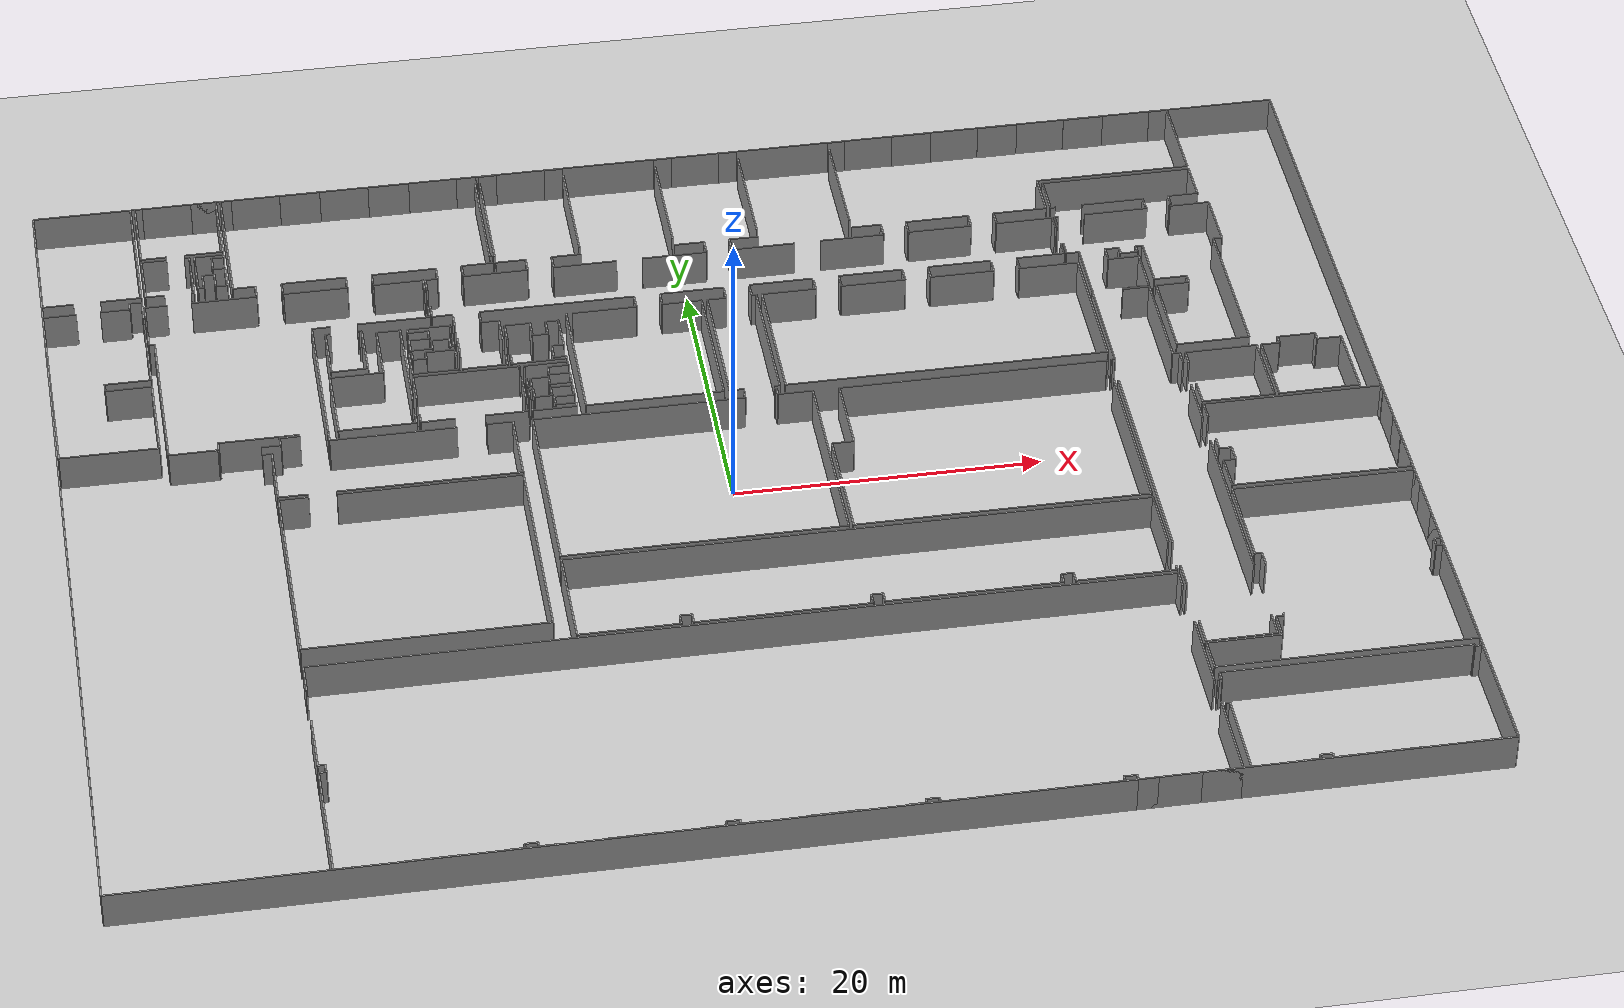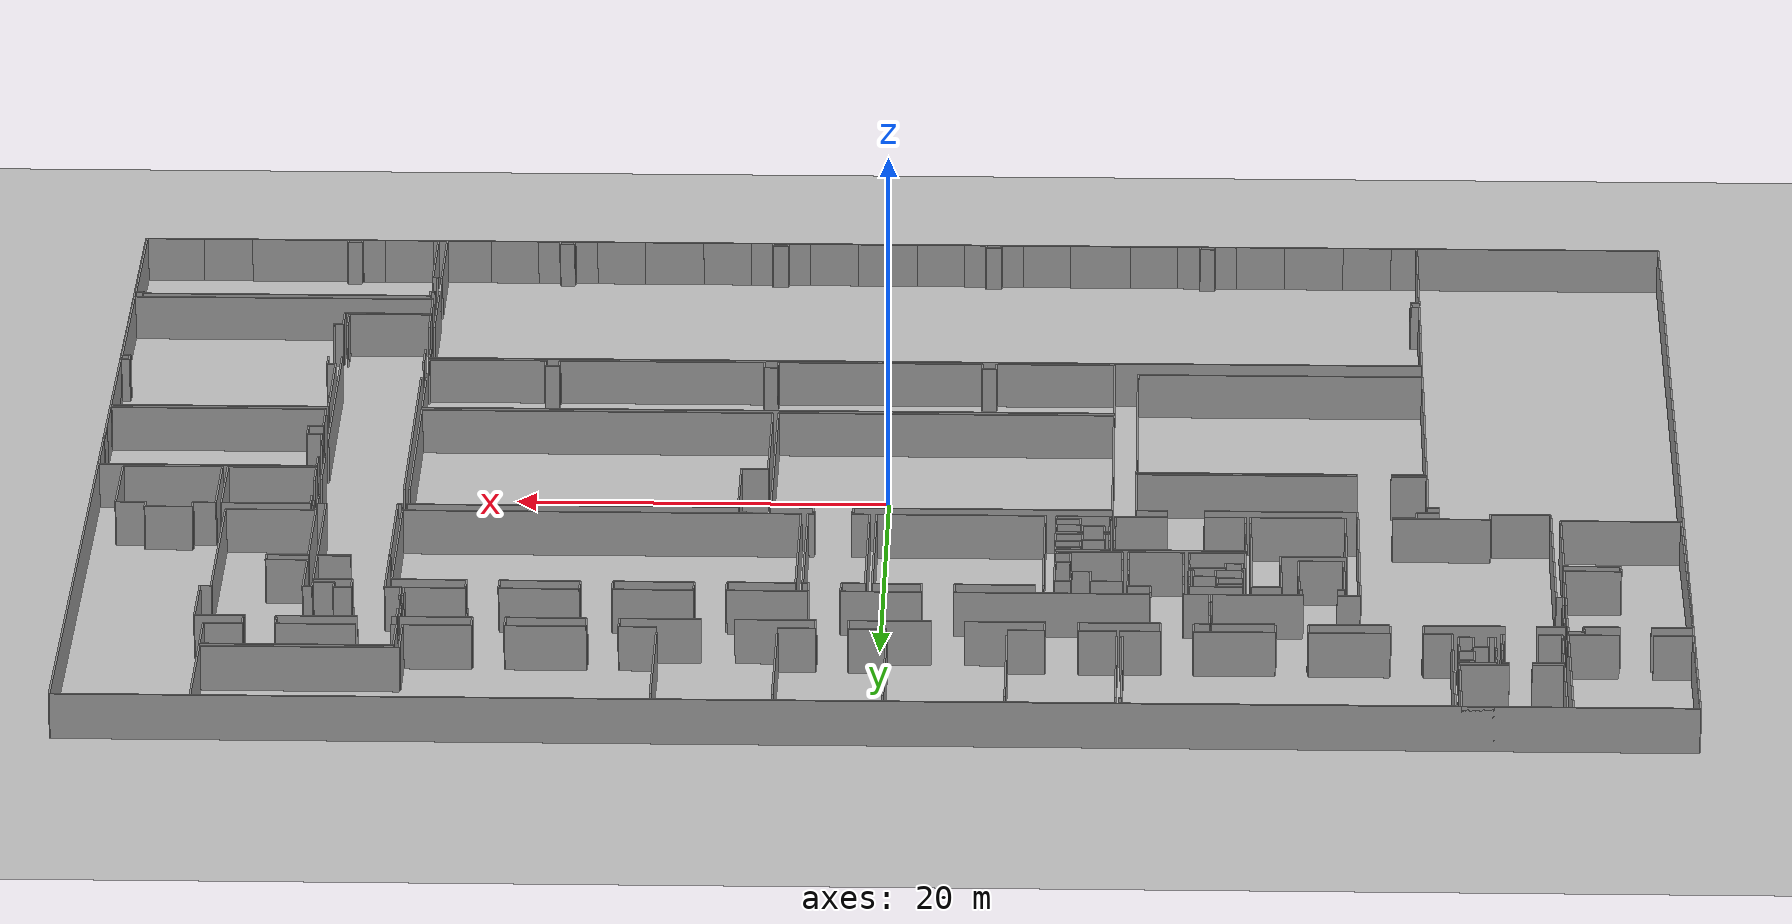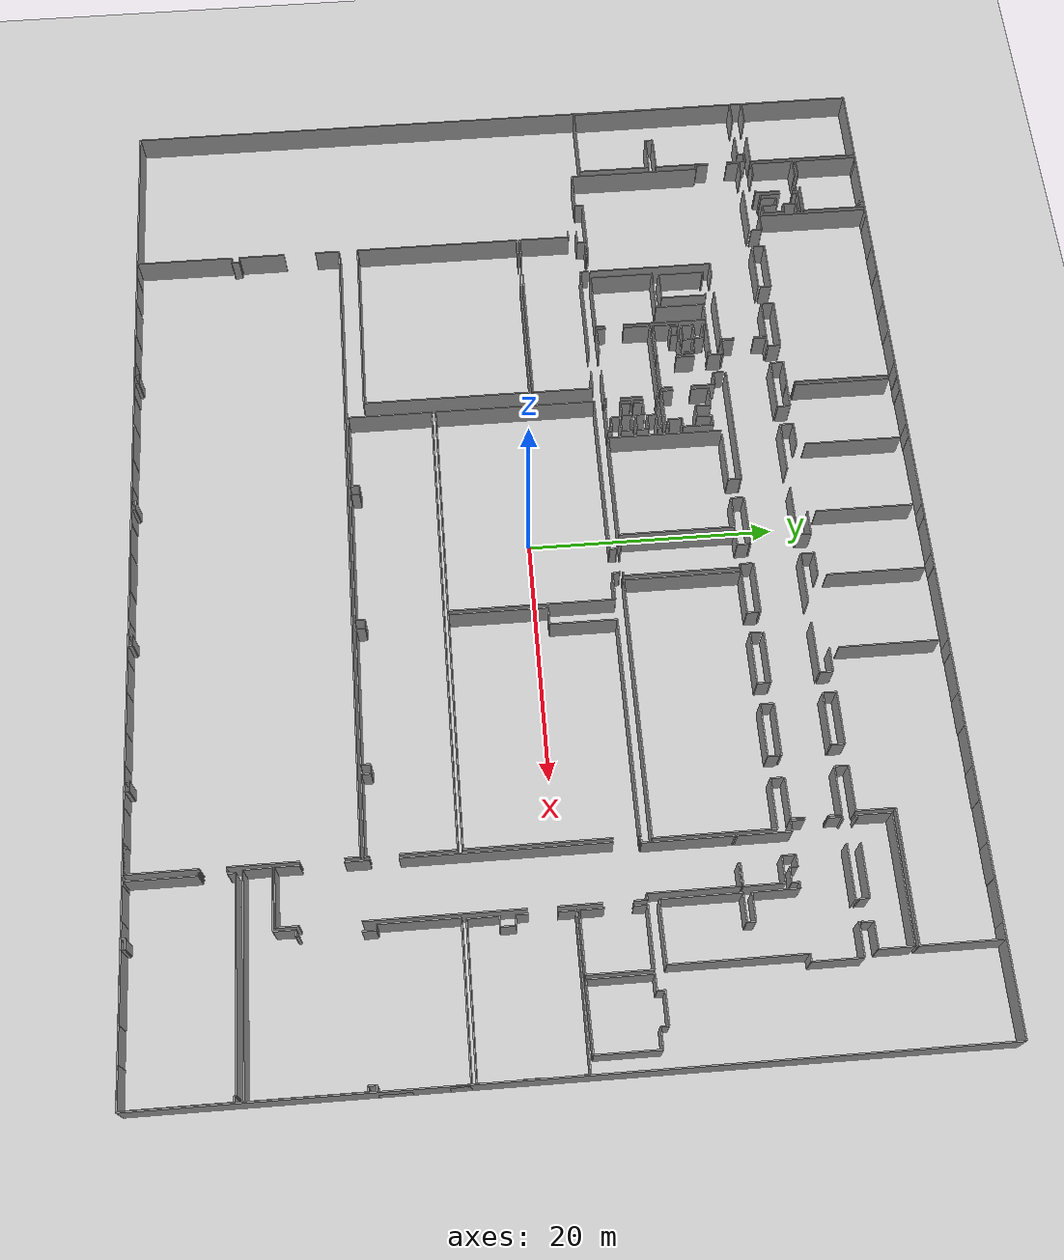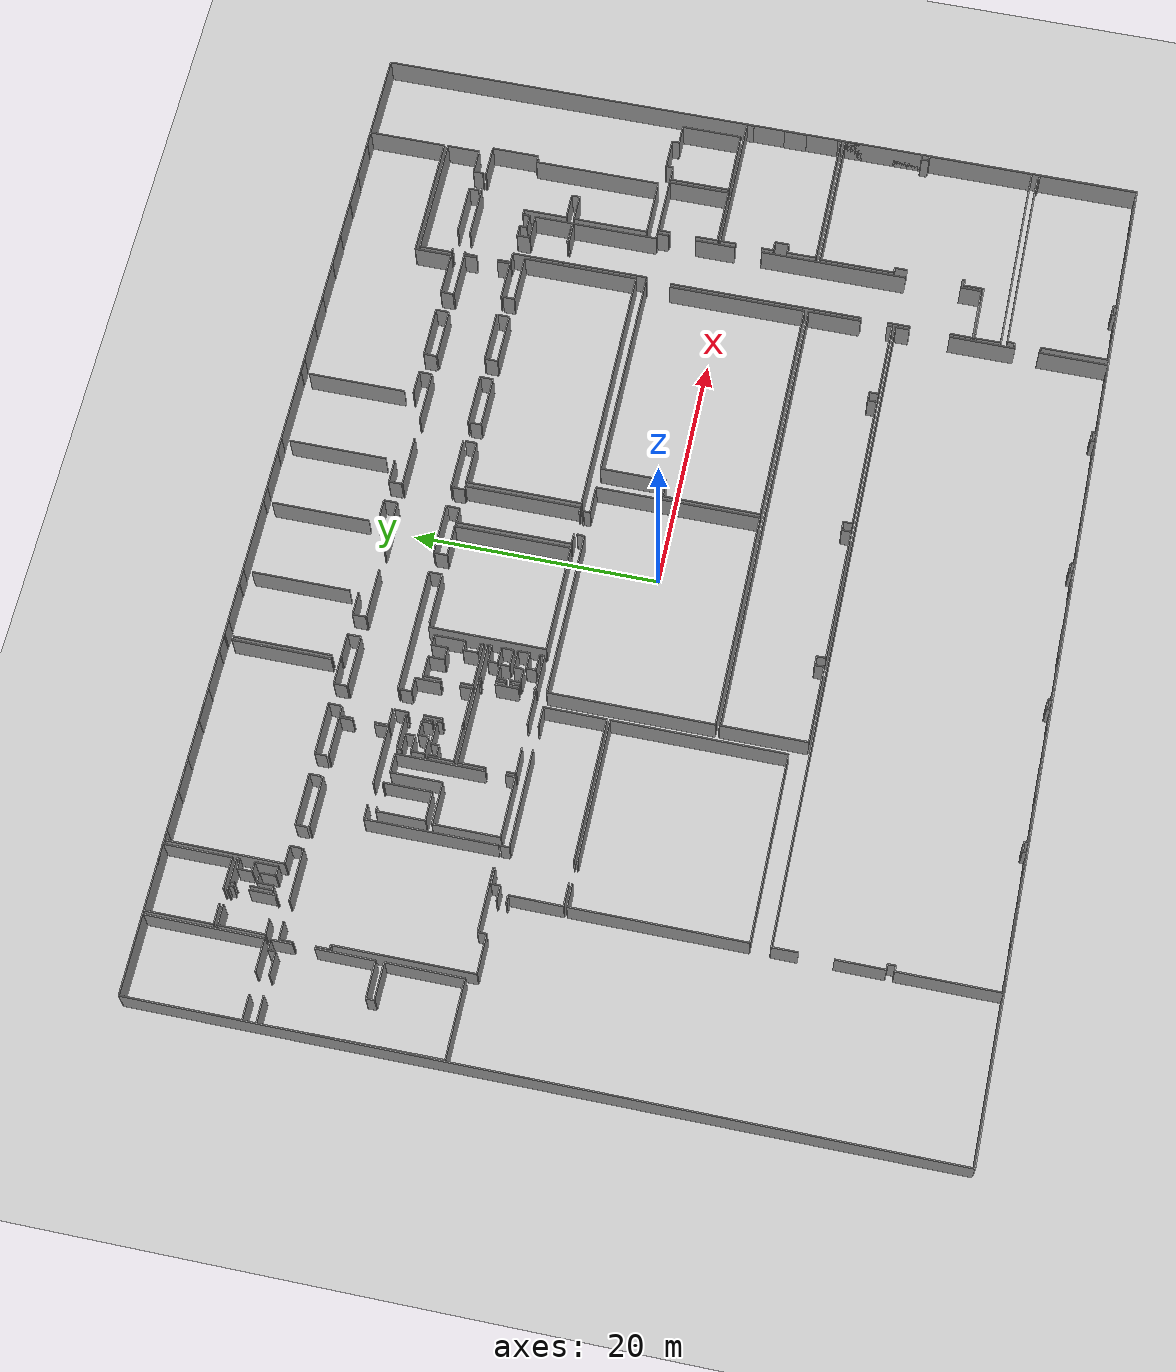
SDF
<sdf version="1.6">
  <world name="default">
    <light name="sun" type="directional">
      <cast_shadows>1</cast_shadows>
      <pose frame="">0 0 10 0 -0 0</pose>
      <diffuse>0.8 0.8 0.8 1</diffuse>
      <specular>0.1 0.1 0.1 1</specular>
      <attenuation>
        <range>1000</range>
        <constant>0.9</constant>
        <linear>0.01</linear>
        <quadratic>0.001</quadratic>
      </attenuation>
      <direction>-0.5 0.5 -1</direction>
    </light>
    <model name="ground_plane">
      <static>1</static>
      <link name="link">
        <collision name="collision">
          <geometry>
            <plane>
              <normal>0 0 1</normal>
              <size>100 100</size>
            </plane>
          </geometry>
          <surface>
            <friction>
              <ode>
                <mu>100</mu>
                <mu2>50</mu2>
              </ode>
              <torsional>
                <ode />
              </torsional>
            </friction>
            <contact>
              <ode />
            </contact>
            <bounce />
          </surface>
          <max_contacts>10</max_contacts>
        </collision>
        <visual name="visual">
          <cast_shadows>0</cast_shadows>
          <geometry>
            <plane>
              <normal>0 0 1</normal>
              <size>100 100</size>
            </plane>
          </geometry>
          <material>
            <script>
              <uri>file://media/materials/scripts/gazebo.material</uri>
              <name>Gazebo/Grey</name>
            </script>
          </material>
        </visual>
        <self_collide>0</self_collide>
        <kinematic>0</kinematic>
        <gravity>1</gravity>
      </link>
    </model>
    <gravity>0 0 -9.8</gravity>
    <magnetic_field>6e-06 2.3e-05 -4.2e-05</magnetic_field>
    <atmosphere type="adiabatic" />
    <physics default="0" name="default_physics" type="ode">
      <max_step_size>0.001</max_step_size>
      <real_time_factor>1</real_time_factor>
      <real_time_update_rate>1000</real_time_update_rate>
    </physics>
    <scene>
      <ambient>0.4 0.4 0.4 1</ambient>
      <background>0.7 0.7 0.7 1</background>
      <shadows>1</shadows>
    </scene>
    <spherical_coordinates>
      <surface_model>EARTH_WGS84</surface_model>
      <latitude_deg>0</latitude_deg>
      <longitude_deg>0</longitude_deg>
      <elevation>0</elevation>
      <heading_deg>0</heading_deg>
    </spherical_coordinates>
  <model name="50052749">
		<static>1</static>
		<link name="Wall_0">
			<collision name="Wall_0_Collision">
				<geometry>
					<box>
						<size>2.05079957599 0.1 2.5</size>
					</box>
				</geometry>
				<pose frame="">1.025399788 0 1.25 0 0 0</pose>
			</collision>
			<visual name="Wall_0_Visual">
				<pose frame="">1.025399788 0 1.25 0 0 0</pose>
				<geometry>
					<box>
						<size>2.05079957599 0.1 2.5</size>
					</box>
				</geometry>
				<material>
					<script>
						<uri>file://media/materials/scripts/gazebo.material</uri>
						<name>Gazebo/Grey</name>
					</script>
					<ambient>1 1 1 1</ambient>
				</material>
			</visual>
			<pose frame="">0.0330937732988 -9.48650129078 0 0 0 0.0</pose>
		</link>
		<link name="Wall_1">
			<collision name="Wall_1_Collision">
				<geometry>
					<box>
						<size>2.67488981422 0.1 2.5</size>
					</box>
				</geometry>
				<pose frame="">1.33744490711 0 1.25 0 0 0</pose>
			</collision>
			<visual name="Wall_1_Visual">
				<pose frame="">1.33744490711 0 1.25 0 0 0</pose>
				<geometry>
					<box>
						<size>2.67488981422 0.1 2.5</size>
					</box>
				</geometry>
				<material>
					<script>
						<uri>file://media/materials/scripts/gazebo.material</uri>
						<name>Gazebo/Grey</name>
					</script>
					<ambient>1 1 1 1</ambient>
				</material>
			</visual>
			<pose frame="">3.85472721094 -9.48650129078 0 0 0 0.0</pose>
		</link>
		<link name="Wall_2">
			<collision name="Wall_2_Collision">
				<geometry>
					<box>
						<size>9.47166615103 0.1 2.5</size>
					</box>
				</geometry>
				<pose frame="">4.73583307551 0 1.25 0 0 0</pose>
			</collision>
			<visual name="Wall_2_Visual">
				<pose frame="">4.73583307551 0 1.25 0 0 0</pose>
				<geometry>
					<box>
						<size>9.47166615103 0.1 2.5</size>
					</box>
				</geometry>
				<material>
					<script>
						<uri>file://media/materials/scripts/gazebo.material</uri>
						<name>Gazebo/Grey</name>
					</script>
					<ambient>1 1 1 1</ambient>
				</material>
			</visual>
			<pose frame="">6.52961702516 -9.48650129078 0 0 0 1.57079632679</pose>
		</link>
		<link name="Wall_3">
			<collision name="Wall_3_Collision">
				<geometry>
					<box>
						<size>6.51960013593 0.1 2.5</size>
					</box>
				</geometry>
				<pose frame="">3.25980006796 0 1.25 0 0 0</pose>
			</collision>
			<visual name="Wall_3_Visual">
				<pose frame="">3.25980006796 0 1.25 0 0 0</pose>
				<geometry>
					<box>
						<size>6.51960013593 0.1 2.5</size>
					</box>
				</geometry>
				<material>
					<script>
						<uri>file://media/materials/scripts/gazebo.material</uri>
						<name>Gazebo/Grey</name>
					</script>
					<ambient>1 1 1 1</ambient>
				</material>
			</visual>
			<pose frame="">6.52961702516 -0.0148351397546 0 0 0 3.14159265359</pose>
		</link>
		<link name="Wall_4">
			<collision name="Wall_4_Collision">
				<geometry>
					<box>
						<size>9.47169426339 0.1 2.5</size>
					</box>
				</geometry>
				<pose frame="">4.73584713169 0 1.25 0 0 0</pose>
			</collision>
			<visual name="Wall_4_Visual">
				<pose frame="">4.73584713169 0 1.25 0 0 0</pose>
				<geometry>
					<box>
						<size>9.47169426339 0.1 2.5</size>
					</box>
				</geometry>
				<material>
					<script>
						<uri>file://media/materials/scripts/gazebo.material</uri>
						<name>Gazebo/Grey</name>
					</script>
					<ambient>1 1 1 1</ambient>
				</material>
			</visual>
			<pose frame="">0.010016889236 -0.0148351397546 0 0 0 -1.5683599193</pose>
		</link>
		<link name="Wall_5">
			<collision name="Wall_5_Collision">
				<geometry>
					<box>
						<size>6.41410580878 0.1 2.5</size>
					</box>
				</geometry>
				<pose frame="">3.20705290439 0 1.25 0 0 0</pose>
			</collision>
			<visual name="Wall_5_Visual">
				<pose frame="">3.20705290439 0 1.25 0 0 0</pose>
				<geometry>
					<box>
						<size>6.41410580878 0.1 2.5</size>
					</box>
				</geometry>
				<material>
					<script>
						<uri>file://media/materials/scripts/gazebo.material</uri>
						<name>Gazebo/Grey</name>
					</script>
					<ambient>1 1 1 1</ambient>
				</material>
			</visual>
			<pose frame="">0.105874715343 -24.942688178 0 0 0 0.0</pose>
		</link>
		<link name="Wall_6">
			<collision name="Wall_6_Collision">
				<geometry>
					<box>
						<size>6.22048821557 0.1 2.5</size>
					</box>
				</geometry>
				<pose frame="">3.11024410779 0 1.25 0 0 0</pose>
			</collision>
			<visual name="Wall_6_Visual">
				<pose frame="">3.11024410779 0 1.25 0 0 0</pose>
				<geometry>
					<box>
						<size>6.22048821557 0.1 2.5</size>
					</box>
				</geometry>
				<material>
					<script>
						<uri>file://media/materials/scripts/gazebo.material</uri>
						<name>Gazebo/Grey</name>
					</script>
					<ambient>1 1 1 1</ambient>
				</material>
			</visual>
			<pose frame="">6.51998052412 -24.942688178 0 0 0 1.57079632679</pose>
		</link>
		<link name="Wall_7">
			<collision name="Wall_7_Collision">
				<geometry>
					<box>
						<size>2.99948774389 0.1 2.5</size>
					</box>
				</geometry>
				<pose frame="">1.49974387195 0 1.25 0 0 0</pose>
			</collision>
			<visual name="Wall_7_Visual">
				<pose frame="">1.49974387195 0 1.25 0 0 0</pose>
				<geometry>
					<box>
						<size>2.99948774389 0.1 2.5</size>
					</box>
				</geometry>
				<material>
					<script>
						<uri>file://media/materials/scripts/gazebo.material</uri>
						<name>Gazebo/Grey</name>
					</script>
					<ambient>1 1 1 1</ambient>
				</material>
			</visual>
			<pose frame="">6.51998052412 -18.7221999625 0 0 0 3.14159265359</pose>
		</link>
		<link name="Wall_8">
			<collision name="Wall_8_Collision">
				<geometry>
					<box>
						<size>0.65933954465 0.1 2.5</size>
					</box>
				</geometry>
				<pose frame="">0.329669772325 0 1.25 0 0 0</pose>
			</collision>
			<visual name="Wall_8_Visual">
				<pose frame="">0.329669772325 0 1.25 0 0 0</pose>
				<geometry>
					<box>
						<size>0.65933954465 0.1 2.5</size>
					</box>
				</geometry>
				<material>
					<script>
						<uri>file://media/materials/scripts/gazebo.material</uri>
						<name>Gazebo/Grey</name>
					</script>
					<ambient>1 1 1 1</ambient>
				</material>
			</visual>
			<pose frame="">3.52049278023 -18.7221999625 0 0 0 1.57079632679</pose>
		</link>
		<link name="Wall_9">
			<collision name="Wall_9_Collision">
				<geometry>
					<box>
						<size>3.00506677081 0.1 2.5</size>
					</box>
				</geometry>
				<pose frame="">1.5025333854 0 1.25 0 0 0</pose>
			</collision>
			<visual name="Wall_9_Visual">
				<pose frame="">1.5025333854 0 1.25 0 0 0</pose>
				<geometry>
					<box>
						<size>3.00506677081 0.1 2.5</size>
					</box>
				</geometry>
				<material>
					<script>
						<uri>file://media/materials/scripts/gazebo.material</uri>
						<name>Gazebo/Grey</name>
					</script>
					<ambient>1 1 1 1</ambient>
				</material>
			</visual>
			<pose frame="">3.52049278023 -18.0628604178 0 0 0 0.0</pose>
		</link>
		<link name="Wall_10">
			<collision name="Wall_10_Collision">
				<geometry>
					<box>
						<size>4.69246882085 0.1 2.5</size>
					</box>
				</geometry>
				<pose frame="">2.34623441042 0 1.25 0 0 0</pose>
			</collision>
			<visual name="Wall_10_Visual">
				<pose frame="">2.34623441042 0 1.25 0 0 0</pose>
				<geometry>
					<box>
						<size>4.69246882085 0.1 2.5</size>
					</box>
				</geometry>
				<material>
					<script>
						<uri>file://media/materials/scripts/gazebo.material</uri>
						<name>Gazebo/Grey</name>
					</script>
					<ambient>1 1 1 1</ambient>
				</material>
			</visual>
			<pose frame="">6.52555955104 -18.0628604178 0 0 0 1.57079632679</pose>
		</link>
		<link name="Wall_11">
			<collision name="Wall_11_Collision">
				<geometry>
					<box>
						<size>1.68435894445 0.1 2.5</size>
					</box>
				</geometry>
				<pose frame="">0.842179472224 0 1.25 0 0 0</pose>
			</collision>
			<visual name="Wall_11_Visual">
				<pose frame="">0.842179472224 0 1.25 0 0 0</pose>
				<geometry>
					<box>
						<size>1.68435894445 0.1 2.5</size>
					</box>
				</geometry>
				<material>
					<script>
						<uri>file://media/materials/scripts/gazebo.material</uri>
						<name>Gazebo/Grey</name>
					</script>
					<ambient>1 1 1 1</ambient>
				</material>
			</visual>
			<pose frame="">6.52555955104 -11.644950727 0 0 0 1.57079632679</pose>
		</link>
		<link name="Wall_12">
			<collision name="Wall_12_Collision">
				<geometry>
					<box>
						<size>0.826329963939 0.1 2.5</size>
					</box>
				</geometry>
				<pose frame="">0.41316498197 0 1.25 0 0 0</pose>
			</collision>
			<visual name="Wall_12_Visual">
				<pose frame="">0.41316498197 0 1.25 0 0 0</pose>
				<geometry>
					<box>
						<size>0.826329963939 0.1 2.5</size>
					</box>
				</geometry>
				<material>
					<script>
						<uri>file://media/materials/scripts/gazebo.material</uri>
						<name>Gazebo/Grey</name>
					</script>
					<ambient>1 1 1 1</ambient>
				</material>
			</visual>
			<pose frame="">6.52555955104 -9.9605917826 0 0 0 3.14159265359</pose>
		</link>
		<link name="Wall_13">
			<collision name="Wall_13_Collision">
				<geometry>
					<box>
						<size>0.608621118138 0.1 2.5</size>
					</box>
				</geometry>
				<pose frame="">0.304310559069 0 1.25 0 0 0</pose>
			</collision>
			<visual name="Wall_13_Visual">
				<pose frame="">0.304310559069 0 1.25 0 0 0</pose>
				<geometry>
					<box>
						<size>0.608621118138 0.1 2.5</size>
					</box>
				</geometry>
				<material>
					<script>
						<uri>file://media/materials/scripts/gazebo.material</uri>
						<name>Gazebo/Grey</name>
					</script>
					<ambient>1 1 1 1</ambient>
				</material>
			</visual>
			<pose frame="">5.6992295871 -9.9605917826 0 0 0 -1.57079632679</pose>
		</link>
		<link name="Wall_14">
			<collision name="Wall_14_Collision">
				<geometry>
					<box>
						<size>1.93414719502 0.1 2.5</size>
					</box>
				</geometry>
				<pose frame="">0.967073597509 0 1.25 0 0 0</pose>
			</collision>
			<visual name="Wall_14_Visual">
				<pose frame="">0.967073597509 0 1.25 0 0 0</pose>
				<geometry>
					<box>
						<size>1.93414719502 0.1 2.5</size>
					</box>
				</geometry>
				<material>
					<script>
						<uri>file://media/materials/scripts/gazebo.material</uri>
						<name>Gazebo/Grey</name>
					</script>
					<ambient>1 1 1 1</ambient>
				</material>
			</visual>
			<pose frame="">5.6992295871 -10.5692129007 0 0 0 3.14159265359</pose>
		</link>
		<link name="Wall_15">
			<collision name="Wall_15_Collision">
				<geometry>
					<box>
						<size>2.19002165677 0.1 2.5</size>
					</box>
				</geometry>
				<pose frame="">1.09501082838 0 1.25 0 0 0</pose>
			</collision>
			<visual name="Wall_15_Visual">
				<pose frame="">1.09501082838 0 1.25 0 0 0</pose>
				<geometry>
					<box>
						<size>2.19002165677 0.1 2.5</size>
					</box>
				</geometry>
				<material>
					<script>
						<uri>file://media/materials/scripts/gazebo.material</uri>
						<name>Gazebo/Grey</name>
					</script>
					<ambient>1 1 1 1</ambient>
				</material>
			</visual>
			<pose frame="">2.19002165677 -10.5692129007 0 0 0 3.14159265359</pose>
		</link>
		<link name="Wall_16">
			<collision name="Wall_16_Collision">
				<geometry>
					<box>
						<size>14.3738652075 0.1 2.5</size>
					</box>
				</geometry>
				<pose frame="">7.18693260374 0 1.25 0 0 0</pose>
			</collision>
			<visual name="Wall_16_Visual">
				<pose frame="">7.18693260374 0 1.25 0 0 0</pose>
				<geometry>
					<box>
						<size>14.3738652075 0.1 2.5</size>
					</box>
				</geometry>
				<material>
					<script>
						<uri>file://media/materials/scripts/gazebo.material</uri>
						<name>Gazebo/Grey</name>
					</script>
					<ambient>1 1 1 1</ambient>
				</material>
			</visual>
			<pose frame="">0.0 -10.5692129007 0 0 0 -1.56343048113</pose>
		</link>
		<link name="Wall_17">
			<collision name="Wall_17_Collision">
				<geometry>
					<box>
						<size>5.46212094316 0.1 2.5</size>
					</box>
				</geometry>
				<pose frame="">2.73106047158 0 1.25 0 0 0</pose>
			</collision>
			<visual name="Wall_17_Visual">
				<pose frame="">2.73106047158 0 1.25 0 0 0</pose>
				<geometry>
					<box>
						<size>5.46212094316 0.1 2.5</size>
					</box>
				</geometry>
				<material>
					<script>
						<uri>file://media/materials/scripts/gazebo.material</uri>
						<name>Gazebo/Grey</name>
					</script>
					<ambient>1 1 1 1</ambient>
				</material>
			</visual>
			<pose frame="">6.82492506352 -5.46212094316 0 0 0 1.57079632679</pose>
		</link>
		<link name="Wall_18">
			<collision name="Wall_18_Collision">
				<geometry>
					<box>
						<size>0.476119228877 0.1 2.5</size>
					</box>
				</geometry>
				<pose frame="">0.238059614439 0 1.25 0 0 0</pose>
			</collision>
			<visual name="Wall_18_Visual">
				<pose frame="">0.238059614439 0 1.25 0 0 0</pose>
				<geometry>
					<box>
						<size>0.476119228877 0.1 2.5</size>
					</box>
				</geometry>
				<material>
					<script>
						<uri>file://media/materials/scripts/gazebo.material</uri>
						<name>Gazebo/Grey</name>
					</script>
					<ambient>1 1 1 1</ambient>
				</material>
			</visual>
			<pose frame="">6.82492506352 -0.0 0 0 0 0.0</pose>
		</link>
		<link name="Wall_19">
			<collision name="Wall_19_Collision">
				<geometry>
					<box>
						<size>1.69640457074 0.1 2.5</size>
					</box>
				</geometry>
				<pose frame="">0.848202285372 0 1.25 0 0 0</pose>
			</collision>
			<visual name="Wall_19_Visual">
				<pose frame="">0.848202285372 0 1.25 0 0 0</pose>
				<geometry>
					<box>
						<size>1.69640457074 0.1 2.5</size>
					</box>
				</geometry>
				<material>
					<script>
						<uri>file://media/materials/scripts/gazebo.material</uri>
						<name>Gazebo/Grey</name>
					</script>
					<ambient>1 1 1 1</ambient>
				</material>
			</visual>
			<pose frame="">10.5706076575 -0.0 0 0 0 0.0</pose>
		</link>
		<link name="Wall_20">
			<collision name="Wall_20_Collision">
				<geometry>
					<box>
						<size>5.44436949388 0.1 2.5</size>
					</box>
				</geometry>
				<pose frame="">2.72218474694 0 1.25 0 0 0</pose>
			</collision>
			<visual name="Wall_20_Visual">
				<pose frame="">2.72218474694 0 1.25 0 0 0</pose>
				<geometry>
					<box>
						<size>5.44436949388 0.1 2.5</size>
					</box>
				</geometry>
				<material>
					<script>
						<uri>file://media/materials/scripts/gazebo.material</uri>
						<name>Gazebo/Grey</name>
					</script>
					<ambient>1 1 1 1</ambient>
				</material>
			</visual>
			<pose frame="">12.2670122282 -0.0 0 0 0 -1.57079632679</pose>
		</link>
		<link name="Wall_21">
			<collision name="Wall_21_Collision">
				<geometry>
					<box>
						<size>2.57535490219 0.1 2.5</size>
					</box>
				</geometry>
				<pose frame="">1.28767745109 0 1.25 0 0 0</pose>
			</collision>
			<visual name="Wall_21_Visual">
				<pose frame="">1.28767745109 0 1.25 0 0 0</pose>
				<geometry>
					<box>
						<size>2.57535490219 0.1 2.5</size>
					</box>
				</geometry>
				<material>
					<script>
						<uri>file://media/materials/scripts/gazebo.material</uri>
						<name>Gazebo/Grey</name>
					</script>
					<ambient>1 1 1 1</ambient>
				</material>
			</visual>
			<pose frame="">12.2670122282 -5.44436949388 0 0 0 3.14159265359</pose>
		</link>
		<link name="Wall_22">
			<collision name="Wall_22_Collision">
				<geometry>
					<box>
						<size>1.68457927209 0.1 2.5</size>
					</box>
				</geometry>
				<pose frame="">0.842289636044 0 1.25 0 0 0</pose>
			</collision>
			<visual name="Wall_22_Visual">
				<pose frame="">0.842289636044 0 1.25 0 0 0</pose>
				<geometry>
					<box>
						<size>1.68457927209 0.1 2.5</size>
					</box>
				</geometry>
				<material>
					<script>
						<uri>file://media/materials/scripts/gazebo.material</uri>
						<name>Gazebo/Grey</name>
					</script>
					<ambient>1 1 1 1</ambient>
				</material>
			</visual>
			<pose frame="">8.50941080404 -5.44436949388 0 0 0 -3.13105484269</pose>
		</link>
		<link name="Wall_23">
			<collision name="Wall_23_Collision">
				<geometry>
					<box>
						<size>1.24767329218 0.1 2.5</size>
					</box>
				</geometry>
				<pose frame="">0.623836646092 0 1.25 0 0 0</pose>
			</collision>
			<visual name="Wall_23_Visual">
				<pose frame="">0.623836646092 0 1.25 0 0 0</pose>
				<geometry>
					<box>
						<size>1.24767329218 0.1 2.5</size>
					</box>
				</geometry>
				<material>
					<script>
						<uri>file://media/materials/scripts/gazebo.material</uri>
						<name>Gazebo/Grey</name>
					</script>
					<ambient>1 1 1 1</ambient>
				</material>
			</visual>
			<pose frame="">6.83151845897 -9.47737197401 0 0 0 0.0</pose>
		</link>
		<link name="Wall_24">
			<collision name="Wall_24_Collision">
				<geometry>
					<box>
						<size>0.189052934822 0.1 2.5</size>
					</box>
				</geometry>
				<pose frame="">0.0945264674109 0 1.25 0 0 0</pose>
			</collision>
			<visual name="Wall_24_Visual">
				<pose frame="">0.0945264674109 0 1.25 0 0 0</pose>
				<geometry>
					<box>
						<size>0.189052934822 0.1 2.5</size>
					</box>
				</geometry>
				<material>
					<script>
						<uri>file://media/materials/scripts/gazebo.material</uri>
						<name>Gazebo/Grey</name>
					</script>
					<ambient>1 1 1 1</ambient>
				</material>
			</visual>
			<pose frame="">9.82834348547 -9.47737197401 0 0 0 0.0</pose>
		</link>
		<link name="Wall_25">
			<collision name="Wall_25_Collision">
				<geometry>
					<box>
						<size>2.15844943626 0.1 2.5</size>
					</box>
				</geometry>
				<pose frame="">1.07922471813 0 1.25 0 0 0</pose>
			</collision>
			<visual name="Wall_25_Visual">
				<pose frame="">1.07922471813 0 1.25 0 0 0</pose>
				<geometry>
					<box>
						<size>2.15844943626 0.1 2.5</size>
					</box>
				</geometry>
				<material>
					<script>
						<uri>file://media/materials/scripts/gazebo.material</uri>
						<name>Gazebo/Grey</name>
					</script>
					<ambient>1 1 1 1</ambient>
				</material>
			</visual>
			<pose frame="">10.0173964203 -9.47737197401 0 0 0 1.57079632679</pose>
		</link>
		<link name="Wall_26">
			<collision name="Wall_26_Collision">
				<geometry>
					<box>
						<size>0.38913712741 0.1 2.5</size>
					</box>
				</geometry>
				<pose frame="">0.194568563705 0 1.25 0 0 0</pose>
			</collision>
			<visual name="Wall_26_Visual">
				<pose frame="">0.194568563705 0 1.25 0 0 0</pose>
				<geometry>
					<box>
						<size>0.38913712741 0.1 2.5</size>
					</box>
				</geometry>
				<material>
					<script>
						<uri>file://media/materials/scripts/gazebo.material</uri>
						<name>Gazebo/Grey</name>
					</script>
					<ambient>1 1 1 1</ambient>
				</material>
			</visual>
			<pose frame="">10.0173964203 -6.14580533254 0 0 0 1.57079632679</pose>
		</link>
		<link name="Wall_27">
			<collision name="Wall_27_Collision">
				<geometry>
					<box>
						<size>0.339813457627 0.1 2.5</size>
					</box>
				</geometry>
				<pose frame="">0.169906728814 0 1.25 0 0 0</pose>
			</collision>
			<visual name="Wall_27_Visual">
				<pose frame="">0.169906728814 0 1.25 0 0 0</pose>
				<geometry>
					<box>
						<size>0.339813457627 0.1 2.5</size>
					</box>
				</geometry>
				<material>
					<script>
						<uri>file://media/materials/scripts/gazebo.material</uri>
						<name>Gazebo/Grey</name>
					</script>
					<ambient>1 1 1 1</ambient>
				</material>
			</visual>
			<pose frame="">10.0173964203 -5.75666820513 0 0 0 3.14159265359</pose>
		</link>
		<link name="Wall_28">
			<collision name="Wall_28_Collision">
				<geometry>
					<box>
						<size>1.68309098379 0.1 2.5</size>
					</box>
				</geometry>
				<pose frame="">0.841545491893 0 1.25 0 0 0</pose>
			</collision>
			<visual name="Wall_28_Visual">
				<pose frame="">0.841545491893 0 1.25 0 0 0</pose>
				<geometry>
					<box>
						<size>1.68309098379 0.1 2.5</size>
					</box>
				</geometry>
				<material>
					<script>
						<uri>file://media/materials/scripts/gazebo.material</uri>
						<name>Gazebo/Grey</name>
					</script>
					<ambient>1 1 1 1</ambient>
				</material>
			</visual>
			<pose frame="">8.51093235683 -5.75666820513 0 0 0 3.14159265359</pose>
		</link>
		<link name="Wall_29">
			<collision name="Wall_29_Collision">
				<geometry>
					<box>
						<size>3.72070558588 0.1 2.5</size>
					</box>
				</geometry>
				<pose frame="">1.86035279294 0 1.25 0 0 0</pose>
			</collision>
			<visual name="Wall_29_Visual">
				<pose frame="">1.86035279294 0 1.25 0 0 0</pose>
				<geometry>
					<box>
						<size>3.72070558588 0.1 2.5</size>
					</box>
				</geometry>
				<material>
					<script>
						<uri>file://media/materials/scripts/gazebo.material</uri>
						<name>Gazebo/Grey</name>
					</script>
					<ambient>1 1 1 1</ambient>
				</material>
			</visual>
			<pose frame="">6.82784137305 -5.75666820513 0 0 0 -1.56980805013</pose>
		</link>
		<link name="Wall_30">
			<collision name="Wall_30_Collision">
				<geometry>
					<box>
						<size>1.76918551279 0.1 2.5</size>
					</box>
				</geometry>
				<pose frame="">0.884592756394 0 1.25 0 0 0</pose>
			</collision>
			<visual name="Wall_30_Visual">
				<pose frame="">0.884592756394 0 1.25 0 0 0</pose>
				<geometry>
					<box>
						<size>1.76918551279 0.1 2.5</size>
					</box>
				</geometry>
				<material>
					<script>
						<uri>file://media/materials/scripts/gazebo.material</uri>
						<name>Gazebo/Grey</name>
					</script>
					<ambient>1 1 1 1</ambient>
				</material>
			</visual>
			<pose frame="">10.3408531854 -9.08810805054 0 0 0 1.57079632679</pose>
		</link>
		<link name="Wall_31">
			<collision name="Wall_31_Collision">
				<geometry>
					<box>
						<size>0.398012852049 0.1 2.5</size>
					</box>
				</geometry>
				<pose frame="">0.199006426025 0 1.25 0 0 0</pose>
			</collision>
			<visual name="Wall_31_Visual">
				<pose frame="">0.199006426025 0 1.25 0 0 0</pose>
				<geometry>
					<box>
						<size>0.398012852049 0.1 2.5</size>
					</box>
				</geometry>
				<material>
					<script>
						<uri>file://media/materials/scripts/gazebo.material</uri>
						<name>Gazebo/Grey</name>
					</script>
					<ambient>1 1 1 1</ambient>
				</material>
			</visual>
			<pose frame="">10.3408531854 -6.16140124869 0 0 0 1.57079632679</pose>
		</link>
		<link name="Wall_32">
			<collision name="Wall_32_Collision">
				<geometry>
					<box>
						<size>1.91411341655 0.1 2.5</size>
					</box>
				</geometry>
				<pose frame="">0.957056708273 0 1.25 0 0 0</pose>
			</collision>
			<visual name="Wall_32_Visual">
				<pose frame="">0.957056708273 0 1.25 0 0 0</pose>
				<geometry>
					<box>
						<size>1.91411341655 0.1 2.5</size>
					</box>
				</geometry>
				<material>
					<script>
						<uri>file://media/materials/scripts/gazebo.material</uri>
						<name>Gazebo/Grey</name>
					</script>
					<ambient>1 1 1 1</ambient>
				</material>
			</visual>
			<pose frame="">10.3408531854 -5.76338839664 0 0 0 0.0</pose>
		</link>
		<link name="Wall_33">
			<collision name="Wall_33_Collision">
				<geometry>
					<box>
						<size>0.279965714344 0.1 2.5</size>
					</box>
				</geometry>
				<pose frame="">0.139982857172 0 1.25 0 0 0</pose>
			</collision>
			<visual name="Wall_33_Visual">
				<pose frame="">0.139982857172 0 1.25 0 0 0</pose>
				<geometry>
					<box>
						<size>0.279965714344 0.1 2.5</size>
					</box>
				</geometry>
				<material>
					<script>
						<uri>file://media/materials/scripts/gazebo.material</uri>
						<name>Gazebo/Grey</name>
					</script>
					<ambient>1 1 1 1</ambient>
				</material>
			</visual>
			<pose frame="">12.2549666019 -5.76338839664 0 0 0 -1.57079632679</pose>
		</link>
		<link name="Wall_34">
			<collision name="Wall_34_Collision">
				<geometry>
					<box>
						<size>0.781063768278 0.1 2.5</size>
					</box>
				</geometry>
				<pose frame="">0.390531884139 0 1.25 0 0 0</pose>
			</collision>
			<visual name="Wall_34_Visual">
				<pose frame="">0.390531884139 0 1.25 0 0 0</pose>
				<geometry>
					<box>
						<size>0.781063768278 0.1 2.5</size>
					</box>
				</geometry>
				<material>
					<script>
						<uri>file://media/materials/scripts/gazebo.material</uri>
						<name>Gazebo/Grey</name>
					</script>
					<ambient>1 1 1 1</ambient>
				</material>
			</visual>
			<pose frame="">12.2549666019 -6.04335411098 0 0 0 3.14159265359</pose>
		</link>
		<link name="Wall_35">
			<collision name="Wall_35_Collision">
				<geometry>
					<box>
						<size>1.17083487602 0.1 2.5</size>
					</box>
				</geometry>
				<pose frame="">0.585417438009 0 1.25 0 0 0</pose>
			</collision>
			<visual name="Wall_35_Visual">
				<pose frame="">0.585417438009 0 1.25 0 0 0</pose>
				<geometry>
					<box>
						<size>1.17083487602 0.1 2.5</size>
					</box>
				</geometry>
				<material>
					<script>
						<uri>file://media/materials/scripts/gazebo.material</uri>
						<name>Gazebo/Grey</name>
					</script>
					<ambient>1 1 1 1</ambient>
				</material>
			</visual>
			<pose frame="">11.4739028336 -6.04335411098 0 0 0 -1.57079632679</pose>
		</link>
		<link name="Wall_36">
			<collision name="Wall_36_Collision">
				<geometry>
					<box>
						<size>0.783472893537 0.1 2.5</size>
					</box>
				</geometry>
				<pose frame="">0.391736446768 0 1.25 0 0 0</pose>
			</collision>
			<visual name="Wall_36_Visual">
				<pose frame="">0.391736446768 0 1.25 0 0 0</pose>
				<geometry>
					<box>
						<size>0.783472893537 0.1 2.5</size>
					</box>
				</geometry>
				<material>
					<script>
						<uri>file://media/materials/scripts/gazebo.material</uri>
						<name>Gazebo/Grey</name>
					</script>
					<ambient>1 1 1 1</ambient>
				</material>
			</visual>
			<pose frame="">11.4739028336 -7.214188987 0 0 0 0.0</pose>
		</link>
		<link name="Wall_37">
			<collision name="Wall_37_Collision">
				<geometry>
					<box>
						<size>1.84716509355 0.1 2.5</size>
					</box>
				</geometry>
				<pose frame="">0.923582546775 0 1.25 0 0 0</pose>
			</collision>
			<visual name="Wall_37_Visual">
				<pose frame="">0.923582546775 0 1.25 0 0 0</pose>
				<geometry>
					<box>
						<size>1.84716509355 0.1 2.5</size>
					</box>
				</geometry>
				<material>
					<script>
						<uri>file://media/materials/scripts/gazebo.material</uri>
						<name>Gazebo/Grey</name>
					</script>
					<ambient>1 1 1 1</ambient>
				</material>
			</visual>
			<pose frame="">12.2573757272 -7.214188987 0 0 0 -1.57079632679</pose>
		</link>
		<link name="Wall_38">
			<collision name="Wall_38_Collision">
				<geometry>
					<box>
						<size>0.758240476347 0.1 2.5</size>
					</box>
				</geometry>
				<pose frame="">0.379120238174 0 1.25 0 0 0</pose>
			</collision>
			<visual name="Wall_38_Visual">
				<pose frame="">0.379120238174 0 1.25 0 0 0</pose>
				<geometry>
					<box>
						<size>0.758240476347 0.1 2.5</size>
					</box>
				</geometry>
				<material>
					<script>
						<uri>file://media/materials/scripts/gazebo.material</uri>
						<name>Gazebo/Grey</name>
					</script>
					<ambient>1 1 1 1</ambient>
				</material>
			</visual>
			<pose frame="">12.2573757272 -9.06135408055 0 0 0 3.14159265359</pose>
		</link>
		<link name="Wall_39">
			<collision name="Wall_39_Collision">
				<geometry>
					<box>
						<size>1.28355657894 0.1 2.5</size>
					</box>
				</geometry>
				<pose frame="">0.64177828947 0 1.25 0 0 0</pose>
			</collision>
			<visual name="Wall_39_Visual">
				<pose frame="">0.64177828947 0 1.25 0 0 0</pose>
				<geometry>
					<box>
						<size>1.28355657894 0.1 2.5</size>
					</box>
				</geometry>
				<material>
					<script>
						<uri>file://media/materials/scripts/gazebo.material</uri>
						<name>Gazebo/Grey</name>
					</script>
					<ambient>1 1 1 1</ambient>
				</material>
			</visual>
			<pose frame="">11.4991352508 -9.06135408055 0 0 0 1.57079632679</pose>
		</link>
		<link name="Wall_40">
			<collision name="Wall_40_Collision">
				<geometry>
					<box>
						<size>0.787657163724 0.1 2.5</size>
					</box>
				</geometry>
				<pose frame="">0.393828581862 0 1.25 0 0 0</pose>
			</collision>
			<visual name="Wall_40_Visual">
				<pose frame="">0.393828581862 0 1.25 0 0 0</pose>
				<geometry>
					<box>
						<size>0.787657163724 0.1 2.5</size>
					</box>
				</geometry>
				<material>
					<script>
						<uri>file://media/materials/scripts/gazebo.material</uri>
						<name>Gazebo/Grey</name>
					</script>
					<ambient>1 1 1 1</ambient>
				</material>
			</visual>
			<pose frame="">11.4991352508 -7.77779750161 0 0 0 3.14159265359</pose>
		</link>
		<link name="Wall_41">
			<collision name="Wall_41_Collision">
				<geometry>
					<box>
						<size>1.30270278495 0.1 2.5</size>
					</box>
				</geometry>
				<pose frame="">0.651351392474 0 1.25 0 0 0</pose>
			</collision>
			<visual name="Wall_41_Visual">
				<pose frame="">0.651351392474 0 1.25 0 0 0</pose>
				<geometry>
					<box>
						<size>1.30270278495 0.1 2.5</size>
					</box>
				</geometry>
				<material>
					<script>
						<uri>file://media/materials/scripts/gazebo.material</uri>
						<name>Gazebo/Grey</name>
					</script>
					<ambient>1 1 1 1</ambient>
				</material>
			</visual>
			<pose frame="">10.7114780871 -7.77779750161 0 0 0 -1.57079632679</pose>
		</link>
		<link name="Wall_42">
			<collision name="Wall_42_Collision">
				<geometry>
					<box>
						<size>0.370702975248 0.1 2.5</size>
					</box>
				</geometry>
				<pose frame="">0.185351487624 0 1.25 0 0 0</pose>
			</collision>
			<visual name="Wall_42_Visual">
				<pose frame="">0.185351487624 0 1.25 0 0 0</pose>
				<geometry>
					<box>
						<size>0.370702975248 0.1 2.5</size>
					</box>
				</geometry>
				<material>
					<script>
						<uri>file://media/materials/scripts/gazebo.material</uri>
						<name>Gazebo/Grey</name>
					</script>
					<ambient>1 1 1 1</ambient>
				</material>
			</visual>
			<pose frame="">10.7114780871 -9.08050028656 0 0 0 -3.1210686799</pose>
		</link>
		<link name="Wall_43">
			<collision name="Wall_43_Collision">
				<geometry>
					<box>
						<size>11.2463038947 0.1 2.5</size>
					</box>
				</geometry>
				<pose frame="">5.62315194733 0 1.25 0 0 0</pose>
			</collision>
			<visual name="Wall_43_Visual">
				<pose frame="">5.62315194733 0 1.25 0 0 0</pose>
				<geometry>
					<box>
						<size>11.2463038947 0.1 2.5</size>
					</box>
				</geometry>
				<material>
					<script>
						<uri>file://media/materials/scripts/gazebo.material</uri>
						<name>Gazebo/Grey</name>
					</script>
					<ambient>1 1 1 1</ambient>
				</material>
			</visual>
			<pose frame="">7.02817915777 -25.73846029 0 0 0 1.57079632679</pose>
		</link>
		<link name="Wall_44">
			<collision name="Wall_44_Collision">
				<geometry>
					<box>
						<size>0.354775393448 0.1 2.5</size>
					</box>
				</geometry>
				<pose frame="">0.177387696724 0 1.25 0 0 0</pose>
			</collision>
			<visual name="Wall_44_Visual">
				<pose frame="">0.177387696724 0 1.25 0 0 0</pose>
				<geometry>
					<box>
						<size>0.354775393448 0.1 2.5</size>
					</box>
				</geometry>
				<material>
					<script>
						<uri>file://media/materials/scripts/gazebo.material</uri>
						<name>Gazebo/Grey</name>
					</script>
					<ambient>1 1 1 1</ambient>
				</material>
			</visual>
			<pose frame="">7.02817915777 -14.4921563953 0 0 0 3.14159265359</pose>
		</link>
		<link name="Wall_45">
			<collision name="Wall_45_Collision">
				<geometry>
					<box>
						<size>1.10261859236 0.1 2.5</size>
					</box>
				</geometry>
				<pose frame="">0.55130929618 0 1.25 0 0 0</pose>
			</collision>
			<visual name="Wall_45_Visual">
				<pose frame="">0.55130929618 0 1.25 0 0 0</pose>
				<geometry>
					<box>
						<size>1.10261859236 0.1 2.5</size>
					</box>
				</geometry>
				<material>
					<script>
						<uri>file://media/materials/scripts/gazebo.material</uri>
						<name>Gazebo/Grey</name>
					</script>
					<ambient>1 1 1 1</ambient>
				</material>
			</visual>
			<pose frame="">6.67340376432 -14.4921563953 0 0 0 1.57079632679</pose>
		</link>
		<link name="Wall_46">
			<collision name="Wall_46_Collision">
				<geometry>
					<box>
						<size>1.09209451886 0.1 2.5</size>
					</box>
				</geometry>
				<pose frame="">0.54604725943 0 1.25 0 0 0</pose>
			</collision>
			<visual name="Wall_46_Visual">
				<pose frame="">0.54604725943 0 1.25 0 0 0</pose>
				<geometry>
					<box>
						<size>1.09209451886 0.1 2.5</size>
					</box>
				</geometry>
				<material>
					<script>
						<uri>file://media/materials/scripts/gazebo.material</uri>
						<name>Gazebo/Grey</name>
					</script>
					<ambient>1 1 1 1</ambient>
				</material>
			</visual>
			<pose frame="">6.67340376432 -11.6529388792 0 0 0 1.57079632679</pose>
		</link>
		<link name="Wall_47">
			<collision name="Wall_47_Collision">
				<geometry>
					<box>
						<size>1.46855203964 0.1 2.5</size>
					</box>
				</geometry>
				<pose frame="">0.734276019821 0 1.25 0 0 0</pose>
			</collision>
			<visual name="Wall_47_Visual">
				<pose frame="">0.734276019821 0 1.25 0 0 0</pose>
				<geometry>
					<box>
						<size>1.46855203964 0.1 2.5</size>
					</box>
				</geometry>
				<material>
					<script>
						<uri>file://media/materials/scripts/gazebo.material</uri>
						<name>Gazebo/Grey</name>
					</script>
					<ambient>1 1 1 1</ambient>
				</material>
			</visual>
			<pose frame="">6.67340376432 -10.5608443604 0 0 0 0.0</pose>
		</link>
		<link name="Wall_48">
			<collision name="Wall_48_Collision">
				<geometry>
					<box>
						<size>4.30193693671 0.1 2.5</size>
					</box>
				</geometry>
				<pose frame="">2.15096846835 0 1.25 0 0 0</pose>
			</collision>
			<visual name="Wall_48_Visual">
				<pose frame="">2.15096846835 0 1.25 0 0 0</pose>
				<geometry>
					<box>
						<size>4.30193693671 0.1 2.5</size>
					</box>
				</geometry>
				<material>
					<script>
						<uri>file://media/materials/scripts/gazebo.material</uri>
						<name>Gazebo/Grey</name>
					</script>
					<ambient>1 1 1 1</ambient>
				</material>
			</visual>
			<pose frame="">9.75936642542 -10.5608443604 0 0 0 0.0</pose>
		</link>
		<link name="Wall_49">
			<collision name="Wall_49_Collision">
				<geometry>
					<box>
						<size>4.23524220585 0.1 2.5</size>
					</box>
				</geometry>
				<pose frame="">2.11762110292 0 1.25 0 0 0</pose>
			</collision>
			<visual name="Wall_49_Visual">
				<pose frame="">2.11762110292 0 1.25 0 0 0</pose>
				<geometry>
					<box>
						<size>4.23524220585 0.1 2.5</size>
					</box>
				</geometry>
				<material>
					<script>
						<uri>file://media/materials/scripts/gazebo.material</uri>
						<name>Gazebo/Grey</name>
					</script>
					<ambient>1 1 1 1</ambient>
				</material>
			</visual>
			<pose frame="">15.8370822704 -10.5608443604 0 0 0 0.0</pose>
		</link>
		<link name="Wall_50">
			<collision name="Wall_50_Collision">
				<geometry>
					<box>
						<size>3.28579326155 0.1 2.5</size>
					</box>
				</geometry>
				<pose frame="">1.64289663077 0 1.25 0 0 0</pose>
			</collision>
			<visual name="Wall_50_Visual">
				<pose frame="">1.64289663077 0 1.25 0 0 0</pose>
				<geometry>
					<box>
						<size>3.28579326155 0.1 2.5</size>
					</box>
				</geometry>
				<material>
					<script>
						<uri>file://media/materials/scripts/gazebo.material</uri>
						<name>Gazebo/Grey</name>
					</script>
					<ambient>1 1 1 1</ambient>
				</material>
			</visual>
			<pose frame="">21.8063874786 -10.5608443604 0 0 0 0.0</pose>
		</link>
		<link name="Wall_51">
			<collision name="Wall_51_Collision">
				<geometry>
					<box>
						<size>1.0776397673 0.1 2.5</size>
					</box>
				</geometry>
				<pose frame="">0.538819883652 0 1.25 0 0 0</pose>
			</collision>
			<visual name="Wall_51_Visual">
				<pose frame="">0.538819883652 0 1.25 0 0 0</pose>
				<geometry>
					<box>
						<size>1.0776397673 0.1 2.5</size>
					</box>
				</geometry>
				<material>
					<script>
						<uri>file://media/materials/scripts/gazebo.material</uri>
						<name>Gazebo/Grey</name>
					</script>
					<ambient>1 1 1 1</ambient>
				</material>
			</visual>
			<pose frame="">25.0921807402 -10.5608443604 0 0 0 -1.57079632679</pose>
		</link>
		<link name="Wall_52">
			<collision name="Wall_52_Collision">
				<geometry>
					<box>
						<size>1.11720013998 0.1 2.5</size>
					</box>
				</geometry>
				<pose frame="">0.558600069991 0 1.25 0 0 0</pose>
			</collision>
			<visual name="Wall_52_Visual">
				<pose frame="">0.558600069991 0 1.25 0 0 0</pose>
				<geometry>
					<box>
						<size>1.11720013998 0.1 2.5</size>
					</box>
				</geometry>
				<material>
					<script>
						<uri>file://media/materials/scripts/gazebo.material</uri>
						<name>Gazebo/Grey</name>
					</script>
					<ambient>1 1 1 1</ambient>
				</material>
			</visual>
			<pose frame="">25.0921807402 -13.3620230566 0 0 0 -1.57079632679</pose>
		</link>
		<link name="Wall_53">
			<collision name="Wall_53_Collision">
				<geometry>
					<box>
						<size>4.80481013557 0.1 2.5</size>
					</box>
				</geometry>
				<pose frame="">2.40240506779 0 1.25 0 0 0</pose>
			</collision>
			<visual name="Wall_53_Visual">
				<pose frame="">2.40240506779 0 1.25 0 0 0</pose>
				<geometry>
					<box>
						<size>4.80481013557 0.1 2.5</size>
					</box>
				</geometry>
				<material>
					<script>
						<uri>file://media/materials/scripts/gazebo.material</uri>
						<name>Gazebo/Grey</name>
					</script>
					<ambient>1 1 1 1</ambient>
				</material>
			</visual>
			<pose frame="">25.0921807402 -14.4792231966 0 0 0 3.14159265359</pose>
		</link>
		<link name="Wall_54">
			<collision name="Wall_54_Collision">
				<geometry>
					<box>
						<size>1.21774942054 0.1 2.5</size>
					</box>
				</geometry>
				<pose frame="">0.608874710271 0 1.25 0 0 0</pose>
			</collision>
			<visual name="Wall_54_Visual">
				<pose frame="">0.608874710271 0 1.25 0 0 0</pose>
				<geometry>
					<box>
						<size>1.21774942054 0.1 2.5</size>
					</box>
				</geometry>
				<material>
					<script>
						<uri>file://media/materials/scripts/gazebo.material</uri>
						<name>Gazebo/Grey</name>
					</script>
					<ambient>1 1 1 1</ambient>
				</material>
			</visual>
			<pose frame="">18.5237641187 -14.4792231966 0 0 0 3.14159265359</pose>
		</link>
		<link name="Wall_55">
			<collision name="Wall_55_Collision">
				<geometry>
					<box>
						<size>10.5574208666 0.1 2.5</size>
					</box>
				</geometry>
				<pose frame="">5.27871043329 0 1.25 0 0 0</pose>
			</collision>
			<visual name="Wall_55_Visual">
				<pose frame="">5.27871043329 0 1.25 0 0 0</pose>
				<geometry>
					<box>
						<size>10.5574208666 0.1 2.5</size>
					</box>
				</geometry>
				<material>
					<script>
						<uri>file://media/materials/scripts/gazebo.material</uri>
						<name>Gazebo/Grey</name>
					</script>
					<ambient>1 1 1 1</ambient>
				</material>
			</visual>
			<pose frame="">17.3060146982 -14.4792231966 0 0 0 -1.57079632679</pose>
		</link>
		<link name="Wall_56">
			<collision name="Wall_56_Collision">
				<geometry>
					<box>
						<size>5.21055754766 0.1 2.5</size>
					</box>
				</geometry>
				<pose frame="">2.60527877383 0 1.25 0 0 0</pose>
			</collision>
			<visual name="Wall_56_Visual">
				<pose frame="">2.60527877383 0 1.25 0 0 0</pose>
				<geometry>
					<box>
						<size>5.21055754766 0.1 2.5</size>
					</box>
				</geometry>
				<material>
					<script>
						<uri>file://media/materials/scripts/gazebo.material</uri>
						<name>Gazebo/Grey</name>
					</script>
					<ambient>1 1 1 1</ambient>
				</material>
			</visual>
			<pose frame="">15.4535241699 -25.0366440632 0 0 0 3.14159265359</pose>
		</link>
		<link name="Wall_57">
			<collision name="Wall_57_Collision">
				<geometry>
					<box>
						<size>0.687741863496 0.1 2.5</size>
					</box>
				</geometry>
				<pose frame="">0.343870931748 0 1.25 0 0 0</pose>
			</collision>
			<visual name="Wall_57_Visual">
				<pose frame="">0.343870931748 0 1.25 0 0 0</pose>
				<geometry>
					<box>
						<size>0.687741863496 0.1 2.5</size>
					</box>
				</geometry>
				<material>
					<script>
						<uri>file://media/materials/scripts/gazebo.material</uri>
						<name>Gazebo/Grey</name>
					</script>
					<ambient>1 1 1 1</ambient>
				</material>
			</visual>
			<pose frame="">10.2429666222 -25.0366440632 0 0 0 -1.57079632679</pose>
		</link>
		<link name="Wall_58">
			<collision name="Wall_58_Collision">
				<geometry>
					<box>
						<size>0.0724005538452 0.1 2.5</size>
					</box>
				</geometry>
				<pose frame="">0.0362002769226 0 1.25 0 0 0</pose>
			</collision>
			<visual name="Wall_58_Visual">
				<pose frame="">0.0362002769226 0 1.25 0 0 0</pose>
				<geometry>
					<box>
						<size>0.0724005538452 0.1 2.5</size>
					</box>
				</geometry>
				<material>
					<script>
						<uri>file://media/materials/scripts/gazebo.material</uri>
						<name>Gazebo/Grey</name>
					</script>
					<ambient>1 1 1 1</ambient>
				</material>
			</visual>
			<pose frame="">10.2429666222 -25.7243859267 0 0 0 3.14159265359</pose>
		</link>
		<link name="Wall_59">
			<collision name="Wall_59_Collision">
				<geometry>
					<box>
						<size>3.1424184291 0.1 2.5</size>
					</box>
				</geometry>
				<pose frame="">1.57120921455 0 1.25 0 0 0</pose>
			</collision>
			<visual name="Wall_59_Visual">
				<pose frame="">1.57120921455 0 1.25 0 0 0</pose>
				<geometry>
					<box>
						<size>3.1424184291 0.1 2.5</size>
					</box>
				</geometry>
				<material>
					<script>
						<uri>file://media/materials/scripts/gazebo.material</uri>
						<name>Gazebo/Grey</name>
					</script>
					<ambient>1 1 1 1</ambient>
				</material>
			</visual>
			<pose frame="">10.1705660684 -25.7243859267 0 0 0 -3.13711380689</pose>
		</link>
		<link name="Wall_60">
			<collision name="Wall_60_Collision">
				<geometry>
					<box>
						<size>1.48135844234 0.1 2.5</size>
					</box>
				</geometry>
				<pose frame="">0.740679221168 0 1.25 0 0 0</pose>
			</collision>
			<visual name="Wall_60_Visual">
				<pose frame="">0.740679221168 0 1.25 0 0 0</pose>
				<geometry>
					<box>
						<size>1.48135844234 0.1 2.5</size>
					</box>
				</geometry>
				<material>
					<script>
						<uri>file://media/materials/scripts/gazebo.material</uri>
						<name>Gazebo/Grey</name>
					</script>
					<ambient>1 1 1 1</ambient>
				</material>
			</visual>
			<pose frame="">12.5788037552 -9.48523333012 0 0 0 0.0</pose>
		</link>
		<link name="Wall_61">
			<collision name="Wall_61_Collision">
				<geometry>
					<box>
						<size>0.907859834556 0.1 2.5</size>
					</box>
				</geometry>
				<pose frame="">0.453929917278 0 1.25 0 0 0</pose>
			</collision>
			<visual name="Wall_61_Visual">
				<pose frame="">0.453929917278 0 1.25 0 0 0</pose>
				<geometry>
					<box>
						<size>0.907859834556 0.1 2.5</size>
					</box>
				</geometry>
				<material>
					<script>
						<uri>file://media/materials/scripts/gazebo.material</uri>
						<name>Gazebo/Grey</name>
					</script>
					<ambient>1 1 1 1</ambient>
				</material>
			</visual>
			<pose frame="">14.0601621975 -9.48523333012 0 0 0 -1.57079632679</pose>
		</link>
		<link name="Wall_62">
			<collision name="Wall_62_Collision">
				<geometry>
					<box>
						<size>0.926752448432 0.1 2.5</size>
					</box>
				</geometry>
				<pose frame="">0.463376224216 0 1.25 0 0 0</pose>
			</collision>
			<visual name="Wall_62_Visual">
				<pose frame="">0.463376224216 0 1.25 0 0 0</pose>
				<geometry>
					<box>
						<size>0.926752448432 0.1 2.5</size>
					</box>
				</geometry>
				<material>
					<script>
						<uri>file://media/materials/scripts/gazebo.material</uri>
						<name>Gazebo/Grey</name>
					</script>
					<ambient>1 1 1 1</ambient>
				</material>
			</visual>
			<pose frame="">15.800057819 -10.3930931647 0 0 0 1.57079632679</pose>
		</link>
		<link name="Wall_63">
			<collision name="Wall_63_Collision">
				<geometry>
					<box>
						<size>4.25768510958 0.1 2.5</size>
					</box>
				</geometry>
				<pose frame="">2.12884255479 0 1.25 0 0 0</pose>
			</collision>
			<visual name="Wall_63_Visual">
				<pose frame="">2.12884255479 0 1.25 0 0 0</pose>
				<geometry>
					<box>
						<size>4.25768510958 0.1 2.5</size>
					</box>
				</geometry>
				<material>
					<script>
						<uri>file://media/materials/scripts/gazebo.material</uri>
						<name>Gazebo/Grey</name>
					</script>
					<ambient>1 1 1 1</ambient>
				</material>
			</visual>
			<pose frame="">15.800057819 -9.46634071625 0 0 0 0.0</pose>
		</link>
		<link name="Wall_64">
			<collision name="Wall_64_Collision">
				<geometry>
					<box>
						<size>0.931951087149 0.1 2.5</size>
					</box>
				</geometry>
				<pose frame="">0.465975543575 0 1.25 0 0 0</pose>
			</collision>
			<visual name="Wall_64_Visual">
				<pose frame="">0.465975543575 0 1.25 0 0 0</pose>
				<geometry>
					<box>
						<size>0.931951087149 0.1 2.5</size>
					</box>
				</geometry>
				<material>
					<script>
						<uri>file://media/materials/scripts/gazebo.material</uri>
						<name>Gazebo/Grey</name>
					</script>
					<ambient>1 1 1 1</ambient>
				</material>
			</visual>
			<pose frame="">20.0577429286 -9.46634071625 0 0 0 -1.57079632679</pose>
		</link>
		<link name="Wall_65">
			<collision name="Wall_65_Collision">
				<geometry>
					<box>
						<size>0.922187790046 0.1 2.5</size>
					</box>
				</geometry>
				<pose frame="">0.461093895023 0 1.25 0 0 0</pose>
			</collision>
			<visual name="Wall_65_Visual">
				<pose frame="">0.461093895023 0 1.25 0 0 0</pose>
				<geometry>
					<box>
						<size>0.922187790046 0.1 2.5</size>
					</box>
				</geometry>
				<material>
					<script>
						<uri>file://media/materials/scripts/gazebo.material</uri>
						<name>Gazebo/Grey</name>
					</script>
					<ambient>1 1 1 1</ambient>
				</material>
			</visual>
			<pose frame="">21.7848321474 -10.3982918034 0 0 0 1.57079632679</pose>
		</link>
		<link name="Wall_66">
			<collision name="Wall_66_Collision">
				<geometry>
					<box>
						<size>4.27099869654 0.1 2.5</size>
					</box>
				</geometry>
				<pose frame="">2.13549934827 0 1.25 0 0 0</pose>
			</collision>
			<visual name="Wall_66_Visual">
				<pose frame="">2.13549934827 0 1.25 0 0 0</pose>
				<geometry>
					<box>
						<size>4.27099869654 0.1 2.5</size>
					</box>
				</geometry>
				<material>
					<script>
						<uri>file://media/materials/scripts/gazebo.material</uri>
						<name>Gazebo/Grey</name>
					</script>
					<ambient>1 1 1 1</ambient>
				</material>
			</visual>
			<pose frame="">21.7848321474 -9.47610401335 0 0 0 0.0</pose>
		</link>
		<link name="Wall_67">
			<collision name="Wall_67_Collision">
				<geometry>
					<box>
						<size>1.01398814203 0.1 2.5</size>
					</box>
				</geometry>
				<pose frame="">0.506994071016 0 1.25 0 0 0</pose>
			</collision>
			<visual name="Wall_67_Visual">
				<pose frame="">0.506994071016 0 1.25 0 0 0</pose>
				<geometry>
					<box>
						<size>1.01398814203 0.1 2.5</size>
					</box>
				</geometry>
				<material>
					<script>
						<uri>file://media/materials/scripts/gazebo.material</uri>
						<name>Gazebo/Grey</name>
					</script>
					<ambient>1 1 1 1</ambient>
				</material>
			</visual>
			<pose frame="">26.0558308439 -9.47610401335 0 0 0 -1.57079632679</pose>
		</link>
		<link name="Wall_68">
			<collision name="Wall_68_Collision">
				<geometry>
					<box>
						<size>1.02933046605 0.1 2.5</size>
					</box>
				</geometry>
				<pose frame="">0.514665233026 0 1.25 0 0 0</pose>
			</collision>
			<visual name="Wall_68_Visual">
				<pose frame="">0.514665233026 0 1.25 0 0 0</pose>
				<geometry>
					<box>
						<size>1.02933046605 0.1 2.5</size>
					</box>
				</geometry>
				<material>
					<script>
						<uri>file://media/materials/scripts/gazebo.material</uri>
						<name>Gazebo/Grey</name>
					</script>
					<ambient>1 1 1 1</ambient>
				</material>
			</visual>
			<pose frame="">27.773917542 -10.4900921554 0 0 0 1.57079632679</pose>
		</link>
		<link name="Wall_69">
			<collision name="Wall_69_Collision">
				<geometry>
					<box>
						<size>2.12066420851 0.1 2.5</size>
					</box>
				</geometry>
				<pose frame="">1.06033210426 0 1.25 0 0 0</pose>
			</collision>
			<visual name="Wall_69_Visual">
				<pose frame="">1.06033210426 0 1.25 0 0 0</pose>
				<geometry>
					<box>
						<size>2.12066420851 0.1 2.5</size>
					</box>
				</geometry>
				<material>
					<script>
						<uri>file://media/materials/scripts/gazebo.material</uri>
						<name>Gazebo/Grey</name>
					</script>
					<ambient>1 1 1 1</ambient>
				</material>
			</visual>
			<pose frame="">27.773917542 -9.46076168933 0 0 0 0.0</pose>
		</link>
		<link name="Wall_70">
			<collision name="Wall_70_Collision">
				<geometry>
					<box>
						<size>0.14378673916 0.1 2.5</size>
					</box>
				</geometry>
				<pose frame="">0.0718933695801 0 1.25 0 0 0</pose>
			</collision>
			<visual name="Wall_70_Visual">
				<pose frame="">0.0718933695801 0 1.25 0 0 0</pose>
				<geometry>
					<box>
						<size>0.14378673916 0.1 2.5</size>
					</box>
				</geometry>
				<material>
					<script>
						<uri>file://media/materials/scripts/gazebo.material</uri>
						<name>Gazebo/Grey</name>
					</script>
					<ambient>1 1 1 1</ambient>
				</material>
			</visual>
			<pose frame="">29.8945817505 -8.7396724604 0 0 0 3.14159265359</pose>
		</link>
		<link name="Wall_71">
			<collision name="Wall_71_Collision">
				<geometry>
					<box>
						<size>7.99804226874 0.1 2.5</size>
					</box>
				</geometry>
				<pose frame="">3.99902113437 0 1.25 0 0 0</pose>
			</collision>
			<visual name="Wall_71_Visual">
				<pose frame="">3.99902113437 0 1.25 0 0 0</pose>
				<geometry>
					<box>
						<size>7.99804226874 0.1 2.5</size>
					</box>
				</geometry>
				<material>
					<script>
						<uri>file://media/materials/scripts/gazebo.material</uri>
						<name>Gazebo/Grey</name>
					</script>
					<ambient>1 1 1 1</ambient>
				</material>
			</visual>
			<pose frame="">29.7507950113 -8.7396724604 0 0 0 1.57079632679</pose>
		</link>
		<link name="Wall_72">
			<collision name="Wall_72_Collision">
				<geometry>
					<box>
						<size>0.138714896509 0.1 2.5</size>
					</box>
				</geometry>
				<pose frame="">0.0693574482545 0 1.25 0 0 0</pose>
			</collision>
			<visual name="Wall_72_Visual">
				<pose frame="">0.0693574482545 0 1.25 0 0 0</pose>
				<geometry>
					<box>
						<size>0.138714896509 0.1 2.5</size>
					</box>
				</geometry>
				<material>
					<script>
						<uri>file://media/materials/scripts/gazebo.material</uri>
						<name>Gazebo/Grey</name>
					</script>
					<ambient>1 1 1 1</ambient>
				</material>
			</visual>
			<pose frame="">29.7507950113 -0.741630191665 0 0 0 0.0</pose>
		</link>
		<link name="Wall_73">
			<collision name="Wall_73_Collision">
				<geometry>
					<box>
						<size>1.34277034189 0.1 2.5</size>
					</box>
				</geometry>
				<pose frame="">0.671385170946 0 1.25 0 0 0</pose>
			</collision>
			<visual name="Wall_73_Visual">
				<pose frame="">0.671385170946 0 1.25 0 0 0</pose>
				<geometry>
					<box>
						<size>1.34277034189 0.1 2.5</size>
					</box>
				</geometry>
				<material>
					<script>
						<uri>file://media/materials/scripts/gazebo.material</uri>
						<name>Gazebo/Grey</name>
					</script>
					<ambient>1 1 1 1</ambient>
				</material>
			</visual>
			<pose frame="">29.8895099078 -0.0167370807488 0 0 0 3.14159265359</pose>
		</link>
		<link name="Wall_74">
			<collision name="Wall_74_Collision">
				<geometry>
					<box>
						<size>2.76466142914 0.1 2.5</size>
					</box>
				</geometry>
				<pose frame="">1.38233071457 0 1.25 0 0 0</pose>
			</collision>
			<visual name="Wall_74_Visual">
				<pose frame="">1.38233071457 0 1.25 0 0 0</pose>
				<geometry>
					<box>
						<size>2.76466142914 0.1 2.5</size>
					</box>
				</geometry>
				<material>
					<script>
						<uri>file://media/materials/scripts/gazebo.material</uri>
						<name>Gazebo/Grey</name>
					</script>
					<ambient>1 1 1 1</ambient>
				</material>
			</visual>
			<pose frame="">25.3121719152 -0.0167370807488 0 0 0 3.14159265359</pose>
		</link>
		<link name="Wall_75">
			<collision name="Wall_75_Collision">
				<geometry>
					<box>
						<size>2.71711290429 0.1 2.5</size>
					</box>
				</geometry>
				<pose frame="">1.35855645214 0 1.25 0 0 0</pose>
			</collision>
			<visual name="Wall_75_Visual">
				<pose frame="">1.35855645214 0 1.25 0 0 0</pose>
				<geometry>
					<box>
						<size>2.71711290429 0.1 2.5</size>
					</box>
				</geometry>
				<material>
					<script>
						<uri>file://media/materials/scripts/gazebo.material</uri>
						<name>Gazebo/Grey</name>
					</script>
					<ambient>1 1 1 1</ambient>
				</material>
			</visual>
			<pose frame="">19.2775667328 -0.0167370807488 0 0 0 3.14159265359</pose>
		</link>
		<link name="Wall_76">
			<collision name="Wall_76_Collision">
				<geometry>
					<box>
						<size>0.715003017746 0.1 2.5</size>
					</box>
				</geometry>
				<pose frame="">0.357501508873 0 1.25 0 0 0</pose>
			</collision>
			<visual name="Wall_76_Visual">
				<pose frame="">0.357501508873 0 1.25 0 0 0</pose>
				<geometry>
					<box>
						<size>0.715003017746 0.1 2.5</size>
					</box>
				</geometry>
				<material>
					<script>
						<uri>file://media/materials/scripts/gazebo.material</uri>
						<name>Gazebo/Grey</name>
					</script>
					<ambient>1 1 1 1</ambient>
				</material>
			</visual>
			<pose frame="">13.3000197802 -0.0167370807488 0 0 0 3.14159265359</pose>
		</link>
		<link name="Wall_77">
			<collision name="Wall_77_Collision">
				<geometry>
					<box>
						<size>9.46849828779 0.1 2.5</size>
					</box>
				</geometry>
				<pose frame="">4.73424914389 0 1.25 0 0 0</pose>
			</collision>
			<visual name="Wall_77_Visual">
				<pose frame="">4.73424914389 0 1.25 0 0 0</pose>
				<geometry>
					<box>
						<size>9.46849828779 0.1 2.5</size>
					</box>
				</geometry>
				<material>
					<script>
						<uri>file://media/materials/scripts/gazebo.material</uri>
						<name>Gazebo/Grey</name>
					</script>
					<ambient>1 1 1 1</ambient>
				</material>
			</visual>
			<pose frame="">12.5850167624 -0.0167370807488 0 0 0 -1.57145250347</pose>
		</link>
		<link name="Wall_78">
			<collision name="Wall_78_Collision">
				<geometry>
					<box>
						<size>7.99132207722 0.1 2.5</size>
					</box>
				</geometry>
				<pose frame="">3.99566103861 0 1.25 0 0 0</pose>
			</collision>
			<visual name="Wall_78_Visual">
				<pose frame="">3.99566103861 0 1.25 0 0 0</pose>
				<geometry>
					<box>
						<size>7.99132207722 0.1 2.5</size>
					</box>
				</geometry>
				<material>
					<script>
						<uri>file://media/materials/scripts/gazebo.material</uri>
						<name>Gazebo/Grey</name>
					</script>
					<ambient>1 1 1 1</ambient>
				</material>
			</visual>
			<pose frame="">30.0660100321 -8.74778740864 0 0 0 1.57079632679</pose>
		</link>
		<link name="Wall_79">
			<collision name="Wall_79_Collision">
				<geometry>
					<box>
						<size>1.21128282116 0.1 2.5</size>
					</box>
				</geometry>
				<pose frame="">0.605641410581 0 1.25 0 0 0</pose>
			</collision>
			<visual name="Wall_79_Visual">
				<pose frame="">0.605641410581 0 1.25 0 0 0</pose>
				<geometry>
					<box>
						<size>1.21128282116 0.1 2.5</size>
					</box>
				</geometry>
				<material>
					<script>
						<uri>file://media/materials/scripts/gazebo.material</uri>
						<name>Gazebo/Grey</name>
					</script>
					<ambient>1 1 1 1</ambient>
				</material>
			</visual>
			<pose frame="">30.0660100321 -0.0394335766127 0 0 0 0.0</pose>
		</link>
		<link name="Wall_80">
			<collision name="Wall_80_Collision">
				<geometry>
					<box>
						<size>1.22548398058 0.1 2.5</size>
					</box>
				</geometry>
				<pose frame="">0.612741990292 0 1.25 0 0 0</pose>
			</collision>
			<visual name="Wall_80_Visual">
				<pose frame="">0.612741990292 0 1.25 0 0 0</pose>
				<geometry>
					<box>
						<size>1.22548398058 0.1 2.5</size>
					</box>
				</geometry>
				<material>
					<script>
						<uri>file://media/materials/scripts/gazebo.material</uri>
						<name>Gazebo/Grey</name>
					</script>
					<ambient>1 1 1 1</ambient>
				</material>
			</visual>
			<pose frame="">34.5454614616 -0.0394335766127 0 0 0 0.0</pose>
		</link>
		<link name="Wall_81">
			<collision name="Wall_81_Collision">
				<geometry>
					<box>
						<size>7.98143198405 0.1 2.5</size>
					</box>
				</geometry>
				<pose frame="">3.99071599203 0 1.25 0 0 0</pose>
			</collision>
			<visual name="Wall_81_Visual">
				<pose frame="">3.99071599203 0 1.25 0 0 0</pose>
				<geometry>
					<box>
						<size>7.98143198405 0.1 2.5</size>
					</box>
				</geometry>
				<material>
					<script>
						<uri>file://media/materials/scripts/gazebo.material</uri>
						<name>Gazebo/Grey</name>
					</script>
					<ambient>1 1 1 1</ambient>
				</material>
			</visual>
			<pose frame="">35.7709454422 -0.754309798293 0 0 0 -1.57079632679</pose>
		</link>
		<link name="Wall_82">
			<collision name="Wall_82_Collision">
				<geometry>
					<box>
						<size>1.962803106 0.1 2.5</size>
					</box>
				</geometry>
				<pose frame="">0.981401552998 0 1.25 0 0 0</pose>
			</collision>
			<visual name="Wall_82_Visual">
				<pose frame="">0.981401552998 0 1.25 0 0 0</pose>
				<geometry>
					<box>
						<size>1.962803106 0.1 2.5</size>
					</box>
				</geometry>
				<material>
					<script>
						<uri>file://media/materials/scripts/gazebo.material</uri>
						<name>Gazebo/Grey</name>
					</script>
					<ambient>1 1 1 1</ambient>
				</material>
			</visual>
			<pose frame="">35.7709454422 -9.45683101127 0 0 0 3.14159265359</pose>
		</link>
		<link name="Wall_83">
			<collision name="Wall_83_Collision">
				<geometry>
					<box>
						<size>1.04974463272 0.1 2.5</size>
					</box>
				</geometry>
				<pose frame="">0.524872316361 0 1.25 0 0 0</pose>
			</collision>
			<visual name="Wall_83_Visual">
				<pose frame="">0.524872316361 0 1.25 0 0 0</pose>
				<geometry>
					<box>
						<size>1.04974463272 0.1 2.5</size>
					</box>
				</geometry>
				<material>
					<script>
						<uri>file://media/materials/scripts/gazebo.material</uri>
						<name>Gazebo/Grey</name>
					</script>
					<ambient>1 1 1 1</ambient>
				</material>
			</visual>
			<pose frame="">33.8081423362 -9.45683101127 0 0 0 -1.57079632679</pose>
		</link>
		<link name="Wall_84">
			<collision name="Wall_84_Collision">
				<geometry>
					<box>
						<size>1.03135920311 0.1 2.5</size>
					</box>
				</geometry>
				<pose frame="">0.515679601556 0 1.25 0 0 0</pose>
			</collision>
			<visual name="Wall_84_Visual">
				<pose frame="">0.515679601556 0 1.25 0 0 0</pose>
				<geometry>
					<box>
						<size>1.03135920311 0.1 2.5</size>
					</box>
				</geometry>
				<material>
					<script>
						<uri>file://media/materials/scripts/gazebo.material</uri>
						<name>Gazebo/Grey</name>
					</script>
					<ambient>1 1 1 1</ambient>
				</material>
			</visual>
			<pose frame="">32.0584834176 -10.506575644 0 0 0 1.57079632679</pose>
		</link>
		<link name="Wall_85">
			<collision name="Wall_85_Collision">
				<geometry>
					<box>
						<size>1.9924749993 0.1 2.5</size>
					</box>
				</geometry>
				<pose frame="">0.996237499651 0 1.25 0 0 0</pose>
			</collision>
			<visual name="Wall_85_Visual">
				<pose frame="">0.996237499651 0 1.25 0 0 0</pose>
				<geometry>
					<box>
						<size>1.9924749993 0.1 2.5</size>
					</box>
				</geometry>
				<material>
					<script>
						<uri>file://media/materials/scripts/gazebo.material</uri>
						<name>Gazebo/Grey</name>
					</script>
					<ambient>1 1 1 1</ambient>
				</material>
			</visual>
			<pose frame="">32.0584834176 -9.47521644089 0 0 0 3.14031990386</pose>
		</link>
		<link name="Wall_86">
			<collision name="Wall_86_Collision">
				<geometry>
					<box>
						<size>7.98409470145 0.1 2.5</size>
					</box>
				</geometry>
				<pose frame="">3.99204735072 0 1.25 0 0 0</pose>
			</collision>
			<visual name="Wall_86_Visual">
				<pose frame="">3.99204735072 0 1.25 0 0 0</pose>
				<geometry>
					<box>
						<size>7.98409470145 0.1 2.5</size>
					</box>
				</geometry>
				<material>
					<script>
						<uri>file://media/materials/scripts/gazebo.material</uri>
						<name>Gazebo/Grey</name>
					</script>
					<ambient>1 1 1 1</ambient>
				</material>
			</visual>
			<pose frame="">42.047350723 -8.75615594902 0 0 0 1.57079632679</pose>
		</link>
		<link name="Wall_87">
			<collision name="Wall_87_Collision">
				<geometry>
					<box>
						<size>1.20684495884 0.1 2.5</size>
					</box>
				</geometry>
				<pose frame="">0.603422479421 0 1.25 0 0 0</pose>
			</collision>
			<visual name="Wall_87_Visual">
				<pose frame="">0.603422479421 0 1.25 0 0 0</pose>
				<geometry>
					<box>
						<size>1.20684495884 0.1 2.5</size>
					</box>
				</geometry>
				<material>
					<script>
						<uri>file://media/materials/scripts/gazebo.material</uri>
						<name>Gazebo/Grey</name>
					</script>
					<ambient>1 1 1 1</ambient>
				</material>
			</visual>
			<pose frame="">42.047350723 -0.0237108643941 0 0 0 0.0</pose>
		</link>
		<link name="Wall_88">
			<collision name="Wall_88_Collision">
				<geometry>
					<box>
						<size>1.23943154788 0.1 2.5</size>
					</box>
				</geometry>
				<pose frame="">0.619715773938 0 1.25 0 0 0</pose>
			</collision>
			<visual name="Wall_88_Visual">
				<pose frame="">0.619715773938 0 1.25 0 0 0</pose>
				<geometry>
					<box>
						<size>1.23943154788 0.1 2.5</size>
					</box>
				</geometry>
				<material>
					<script>
						<uri>file://media/materials/scripts/gazebo.material</uri>
						<name>Gazebo/Grey</name>
					</script>
					<ambient>1 1 1 1</ambient>
				</material>
			</visual>
			<pose frame="">46.5098114796 -0.0237108643941 0 0 0 0.0</pose>
		</link>
		<link name="Wall_89">
			<collision name="Wall_89_Collision">
				<geometry>
					<box>
						<size>7.99170246542 0.1 2.5</size>
					</box>
				</geometry>
				<pose frame="">3.99585123271 0 1.25 0 0 0</pose>
			</collision>
			<visual name="Wall_89_Visual">
				<pose frame="">3.99585123271 0 1.25 0 0 0</pose>
				<geometry>
					<box>
						<size>7.99170246542 0.1 2.5</size>
					</box>
				</geometry>
				<material>
					<script>
						<uri>file://media/materials/scripts/gazebo.material</uri>
						<name>Gazebo/Grey</name>
					</script>
					<ambient>1 1 1 1</ambient>
				</material>
			</visual>
			<pose frame="">47.7492430275 -0.743405336593 0 0 0 -1.57079632679</pose>
		</link>
		<link name="Wall_90">
			<collision name="Wall_90_Collision">
				<geometry>
					<box>
						<size>1.97992057494 0.1 2.5</size>
					</box>
				</geometry>
				<pose frame="">0.989960287472 0 1.25 0 0 0</pose>
			</collision>
			<visual name="Wall_90_Visual">
				<pose frame="">0.989960287472 0 1.25 0 0 0</pose>
				<geometry>
					<box>
						<size>1.97992057494 0.1 2.5</size>
					</box>
				</geometry>
				<material>
					<script>
						<uri>file://media/materials/scripts/gazebo.material</uri>
						<name>Gazebo/Grey</name>
					</script>
					<ambient>1 1 1 1</ambient>
				</material>
			</visual>
			<pose frame="">47.7492430275 -9.460127709 0 0 0 3.14159265359</pose>
		</link>
		<link name="Wall_91">
			<collision name="Wall_91_Collision">
				<geometry>
					<box>
						<size>1.04556036254 0.1 2.5</size>
					</box>
				</geometry>
				<pose frame="">0.522780181268 0 1.25 0 0 0</pose>
			</collision>
			<visual name="Wall_91_Visual">
				<pose frame="">0.522780181268 0 1.25 0 0 0</pose>
				<geometry>
					<box>
						<size>1.04556036254 0.1 2.5</size>
					</box>
				</geometry>
				<material>
					<script>
						<uri>file://media/materials/scripts/gazebo.material</uri>
						<name>Gazebo/Grey</name>
					</script>
					<ambient>1 1 1 1</ambient>
				</material>
			</visual>
			<pose frame="">45.7693224525 -9.460127709 0 0 0 -1.57079632679</pose>
		</link>
		<link name="Wall_92">
			<collision name="Wall_92_Collision">
				<geometry>
					<box>
						<size>1.0366846379 0.1 2.5</size>
					</box>
				</geometry>
				<pose frame="">0.518342318948 0 1.25 0 0 0</pose>
			</collision>
			<visual name="Wall_92_Visual">
				<pose frame="">0.518342318948 0 1.25 0 0 0</pose>
				<geometry>
					<box>
						<size>1.0366846379 0.1 2.5</size>
					</box>
				</geometry>
				<material>
					<script>
						<uri>file://media/materials/scripts/gazebo.material</uri>
						<name>Gazebo/Grey</name>
					</script>
					<ambient>1 1 1 1</ambient>
				</material>
			</visual>
			<pose frame="">44.0577023538 -10.5056880715 0 0 0 1.57079632679</pose>
		</link>
		<link name="Wall_93">
			<collision name="Wall_93_Collision">
				<geometry>
					<box>
						<size>2.01035163085 0.1 2.5</size>
					</box>
				</geometry>
				<pose frame="">1.00517581543 0 1.25 0 0 0</pose>
			</collision>
			<visual name="Wall_93_Visual">
				<pose frame="">1.00517581543 0 1.25 0 0 0</pose>
				<geometry>
					<box>
						<size>2.01035163085 0.1 2.5</size>
					</box>
				</geometry>
				<material>
					<script>
						<uri>file://media/materials/scripts/gazebo.material</uri>
						<name>Gazebo/Grey</name>
					</script>
					<ambient>1 1 1 1</ambient>
				</material>
			</visual>
			<pose frame="">44.0577023538 -9.46900343364 0 0 0 3.14159265359</pose>
		</link>
		<link name="Wall_94">
			<collision name="Wall_94_Collision">
				<geometry>
					<box>
						<size>7.99335081428 0.1 2.5</size>
					</box>
				</geometry>
				<pose frame="">3.99667540714 0 1.25 0 0 0</pose>
			</collision>
			<visual name="Wall_94_Visual">
				<pose frame="">3.99667540714 0 1.25 0 0 0</pose>
				<geometry>
					<box>
						<size>7.99335081428 0.1 2.5</size>
					</box>
				</geometry>
				<material>
					<script>
						<uri>file://media/materials/scripts/gazebo.material</uri>
						<name>Gazebo/Grey</name>
					</script>
					<ambient>1 1 1 1</ambient>
				</material>
			</visual>
			<pose frame="">54.0464428632 -8.7396724604 0 0 0 1.57079632679</pose>
		</link>
		<link name="Wall_95">
			<collision name="Wall_95_Collision">
				<geometry>
					<box>
						<size>1.17894982426 0.1 2.5</size>
					</box>
				</geometry>
				<pose frame="">0.58947491213 0 1.25 0 0 0</pose>
			</collision>
			<visual name="Wall_95_Visual">
				<pose frame="">0.58947491213 0 1.25 0 0 0</pose>
				<geometry>
					<box>
						<size>1.17894982426 0.1 2.5</size>
					</box>
				</geometry>
				<material>
					<script>
						<uri>file://media/materials/scripts/gazebo.material</uri>
						<name>Gazebo/Grey</name>
					</script>
					<ambient>1 1 1 1</ambient>
				</material>
			</visual>
			<pose frame="">54.0464428632 -0.0281487267139 0 0 0 0.0</pose>
		</link>
		<link name="Wall_96">
			<collision name="Wall_96_Collision">
				<geometry>
					<box>
						<size>2.72193115481 0.1 2.5</size>
					</box>
				</geometry>
				<pose frame="">1.3609655774 0 1.25 0 0 0</pose>
			</collision>
			<visual name="Wall_96_Visual">
				<pose frame="">1.3609655774 0 1.25 0 0 0</pose>
				<geometry>
					<box>
						<size>2.72193115481 0.1 2.5</size>
					</box>
				</geometry>
				<material>
					<script>
						<uri>file://media/materials/scripts/gazebo.material</uri>
						<name>Gazebo/Grey</name>
					</script>
					<ambient>1 1 1 1</ambient>
				</material>
			</visual>
			<pose frame="">58.5089036198 -0.0281487267139 0 0 0 0.0</pose>
		</link>
		<link name="Wall_97">
			<collision name="Wall_97_Collision">
				<geometry>
					<box>
						<size>2.73144085978 0.1 2.5</size>
					</box>
				</geometry>
				<pose frame="">1.36572042989 0 1.25 0 0 0</pose>
			</collision>
			<visual name="Wall_97_Visual">
				<pose frame="">1.36572042989 0 1.25 0 0 0</pose>
				<geometry>
					<box>
						<size>2.73144085978 0.1 2.5</size>
					</box>
				</geometry>
				<material>
					<script>
						<uri>file://media/materials/scripts/gazebo.material</uri>
						<name>Gazebo/Grey</name>
					</script>
					<ambient>1 1 1 1</ambient>
				</material>
			</visual>
			<pose frame="">64.4946923167 -0.0281487267139 0 0 0 0.0</pose>
		</link>
		<link name="Wall_98">
			<collision name="Wall_98_Collision">
				<geometry>
					<box>
						<size>2.7464027956 0.1 2.5</size>
					</box>
				</geometry>
				<pose frame="">1.3732013978 0 1.25 0 0 0</pose>
			</collision>
			<visual name="Wall_98_Visual">
				<pose frame="">1.3732013978 0 1.25 0 0 0</pose>
				<geometry>
					<box>
						<size>2.7464027956 0.1 2.5</size>
					</box>
				</geometry>
				<material>
					<script>
						<uri>file://media/materials/scripts/gazebo.material</uri>
						<name>Gazebo/Grey</name>
					</script>
					<ambient>1 1 1 1</ambient>
				</material>
			</visual>
			<pose frame="">70.475535967 -0.0281487267139 0 0 0 0.0</pose>
		</link>
		<link name="Wall_99">
			<collision name="Wall_99_Collision">
				<geometry>
					<box>
						<size>1.25528105616 0.1 2.5</size>
					</box>
				</geometry>
				<pose frame="">0.62764052808 0 1.25 0 0 0</pose>
			</collision>
			<visual name="Wall_99_Visual">
				<pose frame="">0.62764052808 0 1.25 0 0 0</pose>
				<geometry>
					<box>
						<size>1.25528105616 0.1 2.5</size>
					</box>
				</geometry>
				<material>
					<script>
						<uri>file://media/materials/scripts/gazebo.material</uri>
						<name>Gazebo/Grey</name>
					</script>
					<ambient>1 1 1 1</ambient>
				</material>
			</visual>
			<pose frame="">76.4780617446 -0.0281487267139 0 0 0 0.0</pose>
		</link>
		<link name="Wall_100">
			<collision name="Wall_100_Collision">
				<geometry>
					<box>
						<size>6.40586406447 0.1 2.5</size>
					</box>
				</geometry>
				<pose frame="">3.20293203224 0 1.25 0 0 0</pose>
			</collision>
			<visual name="Wall_100_Visual">
				<pose frame="">3.20293203224 0 1.25 0 0 0</pose>
				<geometry>
					<box>
						<size>6.40586406447 0.1 2.5</size>
					</box>
				</geometry>
				<material>
					<script>
						<uri>file://media/materials/scripts/gazebo.material</uri>
						<name>Gazebo/Grey</name>
					</script>
					<ambient>1 1 1 1</ambient>
				</material>
			</visual>
			<pose frame="">77.7333428008 -0.0281487267139 0 0 0 -1.57079632679</pose>
		</link>
		<link name="Wall_101">
			<collision name="Wall_101_Collision">
				<geometry>
					<box>
						<size>10.4055191792 0.1 2.5</size>
					</box>
				</geometry>
				<pose frame="">5.20275958959 0 1.25 0 0 0</pose>
			</collision>
			<visual name="Wall_101_Visual">
				<pose frame="">5.20275958959 0 1.25 0 0 0</pose>
				<geometry>
					<box>
						<size>10.4055191792 0.1 2.5</size>
					</box>
				</geometry>
				<material>
					<script>
						<uri>file://media/materials/scripts/gazebo.material</uri>
						<name>Gazebo/Grey</name>
					</script>
					<ambient>1 1 1 1</ambient>
				</material>
			</visual>
			<pose frame="">77.7333428008 -6.43401279119 0 0 0 3.14159265359</pose>
		</link>
		<link name="Wall_102">
			<collision name="Wall_102_Collision">
				<geometry>
					<box>
						<size>3.04386636709 0.1 2.5</size>
					</box>
				</geometry>
				<pose frame="">1.52193318354 0 1.25 0 0 0</pose>
			</collision>
			<visual name="Wall_102_Visual">
				<pose frame="">1.52193318354 0 1.25 0 0 0</pose>
				<geometry>
					<box>
						<size>3.04386636709 0.1 2.5</size>
					</box>
				</geometry>
				<material>
					<script>
						<uri>file://media/materials/scripts/gazebo.material</uri>
						<name>Gazebo/Grey</name>
					</script>
					<ambient>1 1 1 1</ambient>
				</material>
			</visual>
			<pose frame="">67.3278236216 -6.43401279119 0 0 0 -1.57079632679</pose>
		</link>
		<link name="Wall_103">
			<collision name="Wall_103_Collision">
				<geometry>
					<box>
						<size>3.5958096436 0.1 2.5</size>
					</box>
				</geometry>
				<pose frame="">1.7979048218 0 1.25 0 0 0</pose>
			</collision>
			<visual name="Wall_103_Visual">
				<pose frame="">1.7979048218 0 1.25 0 0 0</pose>
				<geometry>
					<box>
						<size>3.5958096436 0.1 2.5</size>
					</box>
				</geometry>
				<material>
					<script>
						<uri>file://media/materials/scripts/gazebo.material</uri>
						<name>Gazebo/Grey</name>
					</script>
					<ambient>1 1 1 1</ambient>
				</material>
			</visual>
			<pose frame="">67.3278236216 -9.47787915828 0 0 0 3.14159265359</pose>
		</link>
		<link name="Wall_104">
			<collision name="Wall_104_Collision">
				<geometry>
					<box>
						<size>1.0122129971 0.1 2.5</size>
					</box>
				</geometry>
				<pose frame="">0.506106498552 0 1.25 0 0 0</pose>
			</collision>
			<visual name="Wall_104_Visual">
				<pose frame="">0.506106498552 0 1.25 0 0 0</pose>
				<geometry>
					<box>
						<size>1.0122129971 0.1 2.5</size>
					</box>
				</geometry>
				<material>
					<script>
						<uri>file://media/materials/scripts/gazebo.material</uri>
						<name>Gazebo/Grey</name>
					</script>
					<ambient>1 1 1 1</ambient>
				</material>
			</visual>
			<pose frame="">63.732013978 -9.47787915828 0 0 0 -1.57079632679</pose>
		</link>
		<link name="Wall_105">
			<collision name="Wall_105_Collision">
				<geometry>
					<box>
						<size>1.01690445156 0.1 2.5</size>
					</box>
				</geometry>
				<pose frame="">0.508452225778 0 1.25 0 0 0</pose>
			</collision>
			<visual name="Wall_105_Visual">
				<pose frame="">0.508452225778 0 1.25 0 0 0</pose>
				<geometry>
					<box>
						<size>1.01690445156 0.1 2.5</size>
					</box>
				</geometry>
				<material>
					<script>
						<uri>file://media/materials/scripts/gazebo.material</uri>
						<name>Gazebo/Grey</name>
					</script>
					<ambient>1 1 1 1</ambient>
				</material>
			</visual>
			<pose frame="">61.9952882582 -10.4900921554 0 0 0 1.57079632679</pose>
		</link>
		<link name="Wall_106">
			<collision name="Wall_106_Collision">
				<geometry>
					<box>
						<size>4.25020414167 0.1 2.5</size>
					</box>
				</geometry>
				<pose frame="">2.12510207083 0 1.25 0 0 0</pose>
			</collision>
			<visual name="Wall_106_Visual">
				<pose frame="">2.12510207083 0 1.25 0 0 0</pose>
				<geometry>
					<box>
						<size>4.25020414167 0.1 2.5</size>
					</box>
				</geometry>
				<material>
					<script>
						<uri>file://media/materials/scripts/gazebo.material</uri>
						<name>Gazebo/Grey</name>
					</script>
					<ambient>1 1 1 1</ambient>
				</material>
			</visual>
			<pose frame="">61.9952882582 -9.47318770382 0 0 0 3.14159265359</pose>
		</link>
		<link name="Wall_107">
			<collision name="Wall_107_Collision">
				<geometry>
					<box>
						<size>1.01348095777 0.1 2.5</size>
					</box>
				</geometry>
				<pose frame="">0.506740478883 0 1.25 0 0 0</pose>
			</collision>
			<visual name="Wall_107_Visual">
				<pose frame="">0.506740478883 0 1.25 0 0 0</pose>
				<geometry>
					<box>
						<size>1.01348095777 0.1 2.5</size>
					</box>
				</geometry>
				<material>
					<script>
						<uri>file://media/materials/scripts/gazebo.material</uri>
						<name>Gazebo/Grey</name>
					</script>
					<ambient>1 1 1 1</ambient>
				</material>
			</visual>
			<pose frame="">57.7450841165 -9.47318770382 0 0 0 -1.57079632679</pose>
		</link>
		<link name="Wall_108">
			<collision name="Wall_108_Collision">
				<geometry>
					<box>
						<size>1.0024497 0.1 2.5</size>
					</box>
				</geometry>
				<pose frame="">0.50122485 0 1.25 0 0 0</pose>
			</collision>
			<visual name="Wall_108_Visual">
				<pose frame="">0.50122485 0 1.25 0 0 0</pose>
				<geometry>
					<box>
						<size>1.0024497 0.1 2.5</size>
					</box>
				</geometry>
				<material>
					<script>
						<uri>file://media/materials/scripts/gazebo.material</uri>
						<name>Gazebo/Grey</name>
					</script>
					<ambient>1 1 1 1</ambient>
				</material>
			</visual>
			<pose frame="">56.0366339195 -10.4866686616 0 0 0 1.57079632679</pose>
		</link>
		<link name="Wall_109">
			<collision name="Wall_109_Collision">
				<geometry>
					<box>
						<size>1.99019784606 0.1 2.5</size>
					</box>
				</geometry>
				<pose frame="">0.995098923031 0 1.25 0 0 0</pose>
			</collision>
			<visual name="Wall_109_Visual">
				<pose frame="">0.995098923031 0 1.25 0 0 0</pose>
				<geometry>
					<box>
						<size>1.99019784606 0.1 2.5</size>
					</box>
				</geometry>
				<material>
					<script>
						<uri>file://media/materials/scripts/gazebo.material</uri>
						<name>Gazebo/Grey</name>
					</script>
					<ambient>1 1 1 1</ambient>
				</material>
			</visual>
			<pose frame="">56.0366339195 -9.48421896159 0 0 0 3.13898052905</pose>
		</link>
		<link name="Wall_110">
			<collision name="Wall_110_Collision">
				<geometry>
					<box>
						<size>0.319779679155 0.1 2.5</size>
					</box>
				</geometry>
				<pose frame="">0.159889839578 0 1.25 0 0 0</pose>
			</collision>
			<visual name="Wall_110_Visual">
				<pose frame="">0.159889839578 0 1.25 0 0 0</pose>
				<geometry>
					<box>
						<size>0.319779679155 0.1 2.5</size>
					</box>
				</geometry>
				<material>
					<script>
						<uri>file://media/materials/scripts/gazebo.material</uri>
						<name>Gazebo/Grey</name>
					</script>
					<ambient>1 1 1 1</ambient>
				</material>
			</visual>
			<pose frame="">67.6318805885 -9.48650129078 0 0 0 0.0</pose>
		</link>
		<link name="Wall_111">
			<collision name="Wall_111_Collision">
				<geometry>
					<box>
						<size>4.17869116029 0.1 2.5</size>
					</box>
				</geometry>
				<pose frame="">2.08934558014 0 1.25 0 0 0</pose>
			</collision>
			<visual name="Wall_111_Visual">
				<pose frame="">2.08934558014 0 1.25 0 0 0</pose>
				<geometry>
					<box>
						<size>4.17869116029 0.1 2.5</size>
					</box>
				</geometry>
				<material>
					<script>
						<uri>file://media/materials/scripts/gazebo.material</uri>
						<name>Gazebo/Grey</name>
					</script>
					<ambient>1 1 1 1</ambient>
				</material>
			</visual>
			<pose frame="">69.7929927422 -9.48650129078 0 0 0 0.0</pose>
		</link>
		<link name="Wall_112">
			<collision name="Wall_112_Collision">
				<geometry>
					<box>
						<size>0.815171910107 0.1 2.5</size>
					</box>
				</geometry>
				<pose frame="">0.407585955053 0 1.25 0 0 0</pose>
			</collision>
			<visual name="Wall_112_Visual">
				<pose frame="">0.407585955053 0 1.25 0 0 0</pose>
				<geometry>
					<box>
						<size>0.815171910107 0.1 2.5</size>
					</box>
				</geometry>
				<material>
					<script>
						<uri>file://media/materials/scripts/gazebo.material</uri>
						<name>Gazebo/Grey</name>
					</script>
					<ambient>1 1 1 1</ambient>
				</material>
			</visual>
			<pose frame="">73.9716839025 -9.48650129078 0 0 0 -1.57079632679</pose>
		</link>
		<link name="Wall_113">
			<collision name="Wall_113_Collision">
				<geometry>
					<box>
						<size>0.0910395755882 0.1 2.5</size>
					</box>
				</geometry>
				<pose frame="">0.0455197877941 0 1.25 0 0 0</pose>
			</collision>
			<visual name="Wall_113_Visual">
				<pose frame="">0.0455197877941 0 1.25 0 0 0</pose>
				<geometry>
					<box>
						<size>0.0910395755882 0.1 2.5</size>
					</box>
				</geometry>
				<material>
					<script>
						<uri>file://media/materials/scripts/gazebo.material</uri>
						<name>Gazebo/Grey</name>
					</script>
					<ambient>1 1 1 1</ambient>
				</material>
			</visual>
			<pose frame="">73.9716839025 -10.3016732009 0 0 0 0.0</pose>
		</link>
		<link name="Wall_114">
			<collision name="Wall_114_Collision">
				<geometry>
					<box>
						<size>0.0958578261068 0.1 2.5</size>
					</box>
				</geometry>
				<pose frame="">0.0479289130534 0 1.25 0 0 0</pose>
			</collision>
			<visual name="Wall_114_Visual">
				<pose frame="">0.0479289130534 0 1.25 0 0 0</pose>
				<geometry>
					<box>
						<size>0.0958578261068 0.1 2.5</size>
					</box>
				</geometry>
				<material>
					<script>
						<uri>file://media/materials/scripts/gazebo.material</uri>
						<name>Gazebo/Grey</name>
					</script>
					<ambient>1 1 1 1</ambient>
				</material>
			</visual>
			<pose frame="">75.617877231 -10.3016732009 0 0 0 0.0</pose>
		</link>
		<link name="Wall_115">
			<collision name="Wall_115_Collision">
				<geometry>
					<box>
						<size>0.842940248622 0.1 2.5</size>
					</box>
				</geometry>
				<pose frame="">0.421470124311 0 1.25 0 0 0</pose>
			</collision>
			<visual name="Wall_115_Visual">
				<pose frame="">0.421470124311 0 1.25 0 0 0</pose>
				<geometry>
					<box>
						<size>0.842940248622 0.1 2.5</size>
					</box>
				</geometry>
				<material>
					<script>
						<uri>file://media/materials/scripts/gazebo.material</uri>
						<name>Gazebo/Grey</name>
					</script>
					<ambient>1 1 1 1</ambient>
				</material>
			</visual>
			<pose frame="">75.7137350571 -10.3016732009 0 0 0 1.57079632679</pose>
		</link>
		<link name="Wall_116">
			<collision name="Wall_116_Collision">
				<geometry>
					<box>
						<size>2.03254094245 0.1 2.5</size>
					</box>
				</geometry>
				<pose frame="">1.01627047122 0 1.25 0 0 0</pose>
			</collision>
			<visual name="Wall_116_Visual">
				<pose frame="">1.01627047122 0 1.25 0 0 0</pose>
				<geometry>
					<box>
						<size>2.03254094245 0.1 2.5</size>
					</box>
				</geometry>
				<material>
					<script>
						<uri>file://media/materials/scripts/gazebo.material</uri>
						<name>Gazebo/Grey</name>
					</script>
					<ambient>1 1 1 1</ambient>
				</material>
			</visual>
			<pose frame="">75.7137350571 -9.45873295227 0 0 0 0.0</pose>
		</link>
		<link name="Wall_117">
			<collision name="Wall_117_Collision">
				<geometry>
					<box>
						<size>2.70798358752 0.1 2.5</size>
					</box>
				</geometry>
				<pose frame="">1.35399179376 0 1.25 0 0 0</pose>
			</collision>
			<visual name="Wall_117_Visual">
				<pose frame="">1.35399179376 0 1.25 0 0 0</pose>
				<geometry>
					<box>
						<size>2.70798358752 0.1 2.5</size>
					</box>
				</geometry>
				<material>
					<script>
						<uri>file://media/materials/scripts/gazebo.material</uri>
						<name>Gazebo/Grey</name>
					</script>
					<ambient>1 1 1 1</ambient>
				</material>
			</visual>
			<pose frame="">77.7462759995 -9.45873295227 0 0 0 1.57079632679</pose>
		</link>
		<link name="Wall_118">
			<collision name="Wall_118_Collision">
				<geometry>
					<box>
						<size>10.0944884286 0.1 2.5</size>
					</box>
				</geometry>
				<pose frame="">5.0472442143 0 1.25 0 0 0</pose>
			</collision>
			<visual name="Wall_118_Visual">
				<pose frame="">5.0472442143 0 1.25 0 0 0</pose>
				<geometry>
					<box>
						<size>10.0944884286 0.1 2.5</size>
					</box>
				</geometry>
				<material>
					<script>
						<uri>file://media/materials/scripts/gazebo.material</uri>
						<name>Gazebo/Grey</name>
					</script>
					<ambient>1 1 1 1</ambient>
				</material>
			</visual>
			<pose frame="">77.7462759995 -6.75074936475 0 0 0 3.14159265359</pose>
		</link>
		<link name="Wall_119">
			<collision name="Wall_119_Collision">
				<geometry>
					<box>
						<size>2.73582435268 0.1 2.5</size>
					</box>
				</geometry>
				<pose frame="">1.36791217634 0 1.25 0 0 0</pose>
			</collision>
			<visual name="Wall_119_Visual">
				<pose frame="">1.36791217634 0 1.25 0 0 0</pose>
				<geometry>
					<box>
						<size>2.73582435268 0.1 2.5</size>
					</box>
				</geometry>
				<material>
					<script>
						<uri>file://media/materials/scripts/gazebo.material</uri>
						<name>Gazebo/Grey</name>
					</script>
					<ambient>1 1 1 1</ambient>
				</material>
			</visual>
			<pose frame="">67.6517875709 -6.75074936475 0 0 0 -1.578072802</pose>
		</link>
		<link name="Wall_120">
			<collision name="Wall_120_Collision">
				<geometry>
					<box>
						<size>1.10439373729 0.1 2.5</size>
					</box>
				</geometry>
				<pose frame="">0.552196868644 0 1.25 0 0 0</pose>
			</collision>
			<visual name="Wall_120_Visual">
				<pose frame="">0.552196868644 0 1.25 0 0 0</pose>
				<geometry>
					<box>
						<size>1.10439373729 0.1 2.5</size>
					</box>
				</geometry>
				<material>
					<script>
						<uri>file://media/materials/scripts/gazebo.material</uri>
						<name>Gazebo/Grey</name>
					</script>
					<ambient>1 1 1 1</ambient>
				</material>
			</visual>
			<pose frame="">25.2329243738 -14.4792231966 0 0 0 1.57079632679</pose>
		</link>
		<link name="Wall_121">
			<collision name="Wall_121_Collision">
				<geometry>
					<box>
						<size>1.0896853936 0.1 2.5</size>
					</box>
				</geometry>
				<pose frame="">0.5448426968 0 1.25 0 0 0</pose>
			</collision>
			<visual name="Wall_121_Visual">
				<pose frame="">0.5448426968 0 1.25 0 0 0</pose>
				<geometry>
					<box>
						<size>1.0896853936 0.1 2.5</size>
					</box>
				</geometry>
				<material>
					<script>
						<uri>file://media/materials/scripts/gazebo.material</uri>
						<name>Gazebo/Grey</name>
					</script>
					<ambient>1 1 1 1</ambient>
				</material>
			</visual>
			<pose frame="">25.2329243738 -11.6529388792 0 0 0 1.57079632679</pose>
		</link>
		<link name="Wall_122">
			<collision name="Wall_122_Collision">
				<geometry>
					<box>
						<size>0.79222182211 0.1 2.5</size>
					</box>
				</geometry>
				<pose frame="">0.396110911055 0 1.25 0 0 0</pose>
			</collision>
			<visual name="Wall_122_Visual">
				<pose frame="">0.396110911055 0 1.25 0 0 0</pose>
				<geometry>
					<box>
						<size>0.79222182211 0.1 2.5</size>
					</box>
				</geometry>
				<material>
					<script>
						<uri>file://media/materials/scripts/gazebo.material</uri>
						<name>Gazebo/Grey</name>
					</script>
					<ambient>1 1 1 1</ambient>
				</material>
			</visual>
			<pose frame="">25.2329243738 -10.5632534856 0 0 0 0.0</pose>
		</link>
		<link name="Wall_123">
			<collision name="Wall_123_Collision">
				<geometry>
					<box>
						<size>4.28139597397 0.1 2.5</size>
					</box>
				</geometry>
				<pose frame="">2.14069798699 0 1.25 0 0 0</pose>
			</collision>
			<visual name="Wall_123_Visual">
				<pose frame="">2.14069798699 0 1.25 0 0 0</pose>
				<geometry>
					<box>
						<size>4.28139597397 0.1 2.5</size>
					</box>
				</geometry>
				<material>
					<script>
						<uri>file://media/materials/scripts/gazebo.material</uri>
						<name>Gazebo/Grey</name>
					</script>
					<ambient>1 1 1 1</ambient>
				</material>
			</visual>
			<pose frame="">27.7661829819 -10.5632534856 0 0 0 0.0</pose>
		</link>
		<link name="Wall_124">
			<collision name="Wall_124_Collision">
				<geometry>
					<box>
						<size>4.22649327727 0.1 2.5</size>
					</box>
				</geometry>
				<pose frame="">2.11324663864 0 1.25 0 0 0</pose>
			</collision>
			<visual name="Wall_124_Visual">
				<pose frame="">2.11324663864 0 1.25 0 0 0</pose>
				<geometry>
					<box>
						<size>4.22649327727 0.1 2.5</size>
					</box>
				</geometry>
				<material>
					<script>
						<uri>file://media/materials/scripts/gazebo.material</uri>
						<name>Gazebo/Grey</name>
					</script>
					<ambient>1 1 1 1</ambient>
				</material>
			</visual>
			<pose frame="">33.7911516633 -10.5632534856 0 0 0 0.0</pose>
		</link>
		<link name="Wall_125">
			<collision name="Wall_125_Collision">
				<geometry>
					<box>
						<size>4.29217363961 0.1 2.5</size>
					</box>
				</geometry>
				<pose frame="">2.1460868198 0 1.25 0 0 0</pose>
			</collision>
			<visual name="Wall_125_Visual">
				<pose frame="">2.1460868198 0 1.25 0 0 0</pose>
				<geometry>
					<box>
						<size>4.29217363961 0.1 2.5</size>
					</box>
				</geometry>
				<material>
					<script>
						<uri>file://media/materials/scripts/gazebo.material</uri>
						<name>Gazebo/Grey</name>
					</script>
					<ambient>1 1 1 1</ambient>
				</material>
			</visual>
			<pose frame="">39.7504399823 -10.5632534856 0 0 0 0.0</pose>
		</link>
		<link name="Wall_126">
			<collision name="Wall_126_Collision">
				<geometry>
					<box>
						<size>4.24513229902 0.1 2.5</size>
					</box>
				</geometry>
				<pose frame="">2.12256614951 0 1.25 0 0 0</pose>
			</collision>
			<visual name="Wall_126_Visual">
				<pose frame="">2.12256614951 0 1.25 0 0 0</pose>
				<geometry>
					<box>
						<size>4.24513229902 0.1 2.5</size>
					</box>
				</geometry>
				<material>
					<script>
						<uri>file://media/materials/scripts/gazebo.material</uri>
						<name>Gazebo/Grey</name>
					</script>
					<ambient>1 1 1 1</ambient>
				</material>
			</visual>
			<pose frame="">45.7670401233 -10.5632534856 0 0 0 0.0</pose>
		</link>
		<link name="Wall_127">
			<collision name="Wall_127_Collision">
				<geometry>
					<box>
						<size>4.28570704022 0.1 2.5</size>
					</box>
				</geometry>
				<pose frame="">2.14285352011 0 1.25 0 0 0</pose>
			</collision>
			<visual name="Wall_127_Visual">
				<pose frame="">2.14285352011 0 1.25 0 0 0</pose>
				<geometry>
					<box>
						<size>4.28570704022 0.1 2.5</size>
					</box>
				</geometry>
				<material>
					<script>
						<uri>file://media/materials/scripts/gazebo.material</uri>
						<name>Gazebo/Grey</name>
					</script>
					<ambient>1 1 1 1</ambient>
				</material>
			</visual>
			<pose frame="">51.754350373 -10.5632534856 0 0 0 0.0</pose>
		</link>
		<link name="Wall_128">
			<collision name="Wall_128_Collision">
				<geometry>
					<box>
						<size>4.24361074622 0.1 2.5</size>
					</box>
				</geometry>
				<pose frame="">2.12180537311 0 1.25 0 0 0</pose>
			</collision>
			<visual name="Wall_128_Visual">
				<pose frame="">2.12180537311 0 1.25 0 0 0</pose>
				<geometry>
					<box>
						<size>4.24361074622 0.1 2.5</size>
					</box>
				</geometry>
				<material>
					<script>
						<uri>file://media/materials/scripts/gazebo.material</uri>
						<name>Gazebo/Grey</name>
					</script>
					<ambient>1 1 1 1</ambient>
				</material>
			</visual>
			<pose frame="">57.7557349861 -10.5632534856 0 0 0 0.0</pose>
		</link>
		<link name="Wall_129">
			<collision name="Wall_129_Collision">
				<geometry>
					<box>
						<size>3.81846353599 0.1 2.5</size>
					</box>
				</geometry>
				<pose frame="">1.90923176799 0 1.25 0 0 0</pose>
			</collision>
			<visual name="Wall_129_Visual">
				<pose frame="">1.90923176799 0 1.25 0 0 0</pose>
				<geometry>
					<box>
						<size>3.81846353599 0.1 2.5</size>
					</box>
				</geometry>
				<material>
					<script>
						<uri>file://media/materials/scripts/gazebo.material</uri>
						<name>Gazebo/Grey</name>
					</script>
					<ambient>1 1 1 1</ambient>
				</material>
			</visual>
			<pose frame="">63.7250401944 -10.5632534856 0 0 0 0.0</pose>
		</link>
		<link name="Wall_130">
			<collision name="Wall_130_Collision">
				<geometry>
					<box>
						<size>1.07231433252 0.1 2.5</size>
					</box>
				</geometry>
				<pose frame="">0.53615716626 0 1.25 0 0 0</pose>
			</collision>
			<visual name="Wall_130_Visual">
				<pose frame="">0.53615716626 0 1.25 0 0 0</pose>
				<geometry>
					<box>
						<size>1.07231433252 0.1 2.5</size>
					</box>
				</geometry>
				<material>
					<script>
						<uri>file://media/materials/scripts/gazebo.material</uri>
						<name>Gazebo/Grey</name>
					</script>
					<ambient>1 1 1 1</ambient>
				</material>
			</visual>
			<pose frame="">67.5435037303 -10.5632534856 0 0 0 -1.57079632679</pose>
		</link>
		<link name="Wall_131">
			<collision name="Wall_131_Collision">
				<geometry>
					<box>
						<size>1.0799220965 0.1 2.5</size>
					</box>
				</geometry>
				<pose frame="">0.539961048248 0 1.25 0 0 0</pose>
			</collision>
			<visual name="Wall_131_Visual">
				<pose frame="">0.539961048248 0 1.25 0 0 0</pose>
				<geometry>
					<box>
						<size>1.0799220965 0.1 2.5</size>
					</box>
				</geometry>
				<material>
					<script>
						<uri>file://media/materials/scripts/gazebo.material</uri>
						<name>Gazebo/Grey</name>
					</script>
					<ambient>1 1 1 1</ambient>
				</material>
			</visual>
			<pose frame="">67.5435037303 -13.376224216 0 0 0 -1.57079632679</pose>
		</link>
		<link name="Wall_132">
			<collision name="Wall_132_Collision">
				<geometry>
					<box>
						<size>3.22936901206 0.1 2.5</size>
					</box>
				</geometry>
				<pose frame="">1.61468450603 0 1.25 0 0 0</pose>
			</collision>
			<visual name="Wall_132_Visual">
				<pose frame="">1.61468450603 0 1.25 0 0 0</pose>
				<geometry>
					<box>
						<size>3.22936901206 0.1 2.5</size>
					</box>
				</geometry>
				<material>
					<script>
						<uri>file://media/materials/scripts/gazebo.material</uri>
						<name>Gazebo/Grey</name>
					</script>
					<ambient>1 1 1 1</ambient>
				</material>
			</visual>
			<pose frame="">67.5435037303 -14.4561463125 0 0 0 3.14159265359</pose>
		</link>
		<link name="Wall_133">
			<collision name="Wall_133_Collision">
				<geometry>
					<box>
						<size>4.21546201951 0.1 2.5</size>
					</box>
				</geometry>
				<pose frame="">2.10773100975 0 1.25 0 0 0</pose>
			</collision>
			<visual name="Wall_133_Visual">
				<pose frame="">2.10773100975 0 1.25 0 0 0</pose>
				<geometry>
					<box>
						<size>4.21546201951 0.1 2.5</size>
					</box>
				</geometry>
				<material>
					<script>
						<uri>file://media/materials/scripts/gazebo.material</uri>
						<name>Gazebo/Grey</name>
					</script>
					<ambient>1 1 1 1</ambient>
				</material>
			</visual>
			<pose frame="">62.5544589105 -14.4561463125 0 0 0 3.14159265359</pose>
		</link>
		<link name="Wall_134">
			<collision name="Wall_134_Collision">
				<geometry>
					<box>
						<size>4.26782879488 0.1 2.5</size>
					</box>
				</geometry>
				<pose frame="">2.13391439744 0 1.25 0 0 0</pose>
			</collision>
			<visual name="Wall_134_Visual">
				<pose frame="">2.13391439744 0 1.25 0 0 0</pose>
				<geometry>
					<box>
						<size>4.26782879488 0.1 2.5</size>
					</box>
				</geometry>
				<material>
					<script>
						<uri>file://media/materials/scripts/gazebo.material</uri>
						<name>Gazebo/Grey</name>
					</script>
					<ambient>1 1 1 1</ambient>
				</material>
			</visual>
			<pose frame="">56.5870556432 -14.4561463125 0 0 0 3.14159265359</pose>
		</link>
		<link name="Wall_135">
			<collision name="Wall_135_Collision">
				<geometry>
					<box>
						<size>4.25705112925 0.1 2.5</size>
					</box>
				</geometry>
				<pose frame="">2.12852556462 0 1.25 0 0 0</pose>
			</collision>
			<visual name="Wall_135_Visual">
				<pose frame="">2.12852556462 0 1.25 0 0 0</pose>
				<geometry>
					<box>
						<size>4.25705112925 0.1 2.5</size>
					</box>
				</geometry>
				<material>
					<script>
						<uri>file://media/materials/scripts/gazebo.material</uri>
						<name>Gazebo/Grey</name>
					</script>
					<ambient>1 1 1 1</ambient>
				</material>
			</visual>
			<pose frame="">50.5666516202 -14.4561463125 0 0 0 3.14159265359</pose>
		</link>
		<link name="Wall_136">
			<collision name="Wall_136_Collision">
				<geometry>
					<box>
						<size>4.22040706609 0.1 2.5</size>
					</box>
				</geometry>
				<pose frame="">2.11020353305 0 1.25 0 0 0</pose>
			</collision>
			<visual name="Wall_136_Visual">
				<pose frame="">2.11020353305 0 1.25 0 0 0</pose>
				<geometry>
					<box>
						<size>4.22040706609 0.1 2.5</size>
					</box>
				</geometry>
				<material>
					<script>
						<uri>file://media/materials/scripts/gazebo.material</uri>
						<name>Gazebo/Grey</name>
					</script>
					<ambient>1 1 1 1</ambient>
				</material>
			</visual>
			<pose frame="">44.578453798 -14.4561463125 0 0 0 3.14159265359</pose>
		</link>
		<link name="Wall_137">
			<collision name="Wall_137_Collision">
				<geometry>
					<box>
						<size>10.2799910736 0.1 2.5</size>
					</box>
				</geometry>
				<pose frame="">5.13999553678 0 1.25 0 0 0</pose>
			</collision>
			<visual name="Wall_137_Visual">
				<pose frame="">5.13999553678 0 1.25 0 0 0</pose>
				<geometry>
					<box>
						<size>10.2799910736 0.1 2.5</size>
					</box>
				</geometry>
				<material>
					<script>
						<uri>file://media/materials/scripts/gazebo.material</uri>
						<name>Gazebo/Grey</name>
					</script>
					<ambient>1 1 1 1</ambient>
				</material>
			</visual>
			<pose frame="">38.6338738227 -14.4561463125 0 0 0 3.14159265359</pose>
		</link>
		<link name="Wall_138">
			<collision name="Wall_138_Collision">
				<geometry>
					<box>
						<size>1.35602671233 0.1 2.5</size>
					</box>
				</geometry>
				<pose frame="">0.678013356164 0 1.25 0 0 0</pose>
			</collision>
			<visual name="Wall_138_Visual">
				<pose frame="">0.678013356164 0 1.25 0 0 0</pose>
				<geometry>
					<box>
						<size>1.35602671233 0.1 2.5</size>
					</box>
				</geometry>
				<material>
					<script>
						<uri>file://media/materials/scripts/gazebo.material</uri>
						<name>Gazebo/Grey</name>
					</script>
					<ambient>1 1 1 1</ambient>
				</material>
			</visual>
			<pose frame="">26.5887547105 -14.4561463125 0 0 0 -3.12457381621</pose>
		</link>
		<link name="Wall_139">
			<collision name="Wall_139_Collision">
				<geometry>
					<box>
						<size>6.22708161102 0.1 2.5</size>
					</box>
				</geometry>
				<pose frame="">3.11354080551 0 1.25 0 0 0</pose>
			</collision>
			<visual name="Wall_139_Visual">
				<pose frame="">3.11354080551 0 1.25 0 0 0</pose>
				<geometry>
					<box>
						<size>6.22708161102 0.1 2.5</size>
					</box>
				</geometry>
				<material>
					<script>
						<uri>file://media/materials/scripts/gazebo.material</uri>
						<name>Gazebo/Grey</name>
					</script>
					<ambient>1 1 1 1</ambient>
				</material>
			</visual>
			<pose frame="">72.8639934675 -24.975147971 0 0 0 1.57079632679</pose>
		</link>
		<link name="Wall_140">
			<collision name="Wall_140_Collision">
				<geometry>
					<box>
						<size>2.19927776961 0.1 2.5</size>
					</box>
				</geometry>
				<pose frame="">1.0996388848 0 1.25 0 0 0</pose>
			</collision>
			<visual name="Wall_140_Visual">
				<pose frame="">1.0996388848 0 1.25 0 0 0</pose>
				<geometry>
					<box>
						<size>2.19927776961 0.1 2.5</size>
					</box>
				</geometry>
				<material>
					<script>
						<uri>file://media/materials/scripts/gazebo.material</uri>
						<name>Gazebo/Grey</name>
					</script>
					<ambient>1 1 1 1</ambient>
				</material>
			</visual>
			<pose frame="">72.8639934675 -18.74806636 0 0 0 0.0</pose>
		</link>
		<link name="Wall_141">
			<collision name="Wall_141_Collision">
				<geometry>
					<box>
						<size>0.661495077777 0.1 2.5</size>
					</box>
				</geometry>
				<pose frame="">0.330747538888 0 1.25 0 0 0</pose>
			</collision>
			<visual name="Wall_141_Visual">
				<pose frame="">0.330747538888 0 1.25 0 0 0</pose>
				<geometry>
					<box>
						<size>0.661495077777 0.1 2.5</size>
					</box>
				</geometry>
				<material>
					<script>
						<uri>file://media/materials/scripts/gazebo.material</uri>
						<name>Gazebo/Grey</name>
					</script>
					<ambient>1 1 1 1</ambient>
				</material>
			</visual>
			<pose frame="">75.0632712371 -18.74806636 0 0 0 1.57079632679</pose>
		</link>
		<link name="Wall_142">
			<collision name="Wall_142_Collision">
				<geometry>
					<box>
						<size>2.19420592696 0.1 2.5</size>
					</box>
				</geometry>
				<pose frame="">1.09710296348 0 1.25 0 0 0</pose>
			</collision>
			<visual name="Wall_142_Visual">
				<pose frame="">1.09710296348 0 1.25 0 0 0</pose>
				<geometry>
					<box>
						<size>2.19420592696 0.1 2.5</size>
					</box>
				</geometry>
				<material>
					<script>
						<uri>file://media/materials/scripts/gazebo.material</uri>
						<name>Gazebo/Grey</name>
					</script>
					<ambient>1 1 1 1</ambient>
				</material>
			</visual>
			<pose frame="">75.0632712371 -18.0865712822 0 0 0 3.14159265359</pose>
		</link>
		<link name="Wall_143">
			<collision name="Wall_143_Collision">
				<geometry>
					<box>
						<size>3.60734808563 0.1 2.5</size>
					</box>
				</geometry>
				<pose frame="">1.80367404282 0 1.25 0 0 0</pose>
			</collision>
			<visual name="Wall_143_Visual">
				<pose frame="">1.80367404282 0 1.25 0 0 0</pose>
				<geometry>
					<box>
						<size>3.60734808563 0.1 2.5</size>
					</box>
				</geometry>
				<material>
					<script>
						<uri>file://media/materials/scripts/gazebo.material</uri>
						<name>Gazebo/Grey</name>
					</script>
					<ambient>1 1 1 1</ambient>
				</material>
			</visual>
			<pose frame="">72.8690653101 -18.0865712822 0 0 0 1.57079632679</pose>
		</link>
		<link name="Wall_144">
			<collision name="Wall_144_Collision">
				<geometry>
					<box>
						<size>0.473456511485 0.1 2.5</size>
					</box>
				</geometry>
				<pose frame="">0.236728255743 0 1.25 0 0 0</pose>
			</collision>
			<visual name="Wall_144_Visual">
				<pose frame="">0.236728255743 0 1.25 0 0 0</pose>
				<geometry>
					<box>
						<size>0.473456511485 0.1 2.5</size>
					</box>
				</geometry>
				<material>
					<script>
						<uri>file://media/materials/scripts/gazebo.material</uri>
						<name>Gazebo/Grey</name>
					</script>
					<ambient>1 1 1 1</ambient>
				</material>
			</visual>
			<pose frame="">72.8690653101 -14.4792231966 0 0 0 3.14159265359</pose>
		</link>
		<link name="Wall_145">
			<collision name="Wall_145_Collision">
				<geometry>
					<box>
						<size>0.583642293082 0.1 2.5</size>
					</box>
				</geometry>
				<pose frame="">0.291821146541 0 1.25 0 0 0</pose>
			</collision>
			<visual name="Wall_145_Visual">
				<pose frame="">0.291821146541 0 1.25 0 0 0</pose>
				<geometry>
					<box>
						<size>0.583642293082 0.1 2.5</size>
					</box>
				</geometry>
				<material>
					<script>
						<uri>file://media/materials/scripts/gazebo.material</uri>
						<name>Gazebo/Grey</name>
					</script>
					<ambient>1 1 1 1</ambient>
				</material>
			</visual>
			<pose frame="">72.3956087986 -14.4792231966 0 0 0 -1.57079632679</pose>
		</link>
		<link name="Wall_146">
			<collision name="Wall_146_Collision">
				<geometry>
					<box>
						<size>1.14217896504 0.1 2.5</size>
					</box>
				</geometry>
				<pose frame="">0.57108948252 0 1.25 0 0 0</pose>
			</collision>
			<visual name="Wall_146_Visual">
				<pose frame="">0.57108948252 0 1.25 0 0 0</pose>
				<geometry>
					<box>
						<size>1.14217896504 0.1 2.5</size>
					</box>
				</geometry>
				<material>
					<script>
						<uri>file://media/materials/scripts/gazebo.material</uri>
						<name>Gazebo/Grey</name>
					</script>
					<ambient>1 1 1 1</ambient>
				</material>
			</visual>
			<pose frame="">72.3956087986 -15.0628654897 0 0 0 3.14159265359</pose>
		</link>
		<link name="Wall_147">
			<collision name="Wall_147_Collision">
				<geometry>
					<box>
						<size>0.608621118138 0.1 2.5</size>
					</box>
				</geometry>
				<pose frame="">0.304310559069 0 1.25 0 0 0</pose>
			</collision>
			<visual name="Wall_147_Visual">
				<pose frame="">0.304310559069 0 1.25 0 0 0</pose>
				<geometry>
					<box>
						<size>0.608621118138 0.1 2.5</size>
					</box>
				</geometry>
				<material>
					<script>
						<uri>file://media/materials/scripts/gazebo.material</uri>
						<name>Gazebo/Grey</name>
					</script>
					<ambient>1 1 1 1</ambient>
				</material>
			</visual>
			<pose frame="">71.2534298336 -15.0628654897 0 0 0 1.57079632679</pose>
		</link>
		<link name="Wall_148">
			<collision name="Wall_148_Collision">
				<geometry>
					<box>
						<size>0.933726232077 0.1 2.5</size>
					</box>
				</geometry>
				<pose frame="">0.466863116039 0 1.25 0 0 0</pose>
			</collision>
			<visual name="Wall_148_Visual">
				<pose frame="">0.466863116039 0 1.25 0 0 0</pose>
				<geometry>
					<box>
						<size>0.933726232077 0.1 2.5</size>
					</box>
				</geometry>
				<material>
					<script>
						<uri>file://media/materials/scripts/gazebo.material</uri>
						<name>Gazebo/Grey</name>
					</script>
					<ambient>1 1 1 1</ambient>
				</material>
			</visual>
			<pose frame="">71.2534298336 -14.4542443715 0 0 0 3.14159265359</pose>
		</link>
		<link name="Wall_149">
			<collision name="Wall_149_Collision">
				<geometry>
					<box>
						<size>1.0671156938 0.1 2.5</size>
					</box>
				</geometry>
				<pose frame="">0.533557846901 0 1.25 0 0 0</pose>
			</collision>
			<visual name="Wall_149_Visual">
				<pose frame="">0.533557846901 0 1.25 0 0 0</pose>
				<geometry>
					<box>
						<size>1.0671156938 0.1 2.5</size>
					</box>
				</geometry>
				<material>
					<script>
						<uri>file://media/materials/scripts/gazebo.material</uri>
						<name>Gazebo/Grey</name>
					</script>
					<ambient>1 1 1 1</ambient>
				</material>
			</visual>
			<pose frame="">70.3197036015 -14.4542443715 0 0 0 -1.57079632679</pose>
		</link>
		<link name="Wall_150">
			<collision name="Wall_150_Collision">
				<geometry>
					<box>
						<size>2.07590519712 0.1 2.5</size>
					</box>
				</geometry>
				<pose frame="">1.03795259856 0 1.25 0 0 0</pose>
			</collision>
			<visual name="Wall_150_Visual">
				<pose frame="">1.03795259856 0 1.25 0 0 0</pose>
				<geometry>
					<box>
						<size>2.07590519712 0.1 2.5</size>
					</box>
				</geometry>
				<material>
					<script>
						<uri>file://media/materials/scripts/gazebo.material</uri>
						<name>Gazebo/Grey</name>
					</script>
					<ambient>1 1 1 1</ambient>
				</material>
			</visual>
			<pose frame="">70.3197036015 -15.5213600653 0 0 0 0.0</pose>
		</link>
		<link name="Wall_151">
			<collision name="Wall_151_Collision">
				<geometry>
					<box>
						<size>3.15519331328 0.1 2.5</size>
					</box>
				</geometry>
				<pose frame="">1.57759665664 0 1.25 0 0 0</pose>
			</collision>
			<visual name="Wall_151_Visual">
				<pose frame="">1.57759665664 0 1.25 0 0 0</pose>
				<geometry>
					<box>
						<size>3.15519331328 0.1 2.5</size>
					</box>
				</geometry>
				<material>
					<script>
						<uri>file://media/materials/scripts/gazebo.material</uri>
						<name>Gazebo/Grey</name>
					</script>
					<ambient>1 1 1 1</ambient>
				</material>
			</visual>
			<pose frame="">72.3956087986 -15.5213600653 0 0 0 -1.57079632679</pose>
		</link>
		<link name="Wall_152">
			<collision name="Wall_152_Collision">
				<geometry>
					<box>
						<size>1.78845851486 0.1 2.5</size>
					</box>
				</geometry>
				<pose frame="">0.894229257432 0 1.25 0 0 0</pose>
			</collision>
			<visual name="Wall_152_Visual">
				<pose frame="">0.894229257432 0 1.25 0 0 0</pose>
				<geometry>
					<box>
						<size>1.78845851486 0.1 2.5</size>
					</box>
				</geometry>
				<material>
					<script>
						<uri>file://media/materials/scripts/gazebo.material</uri>
						<name>Gazebo/Grey</name>
					</script>
					<ambient>1 1 1 1</ambient>
				</material>
			</visual>
			<pose frame="">72.3956087986 -18.6765533786 0 0 0 3.14159265359</pose>
		</link>
		<link name="Wall_153">
			<collision name="Wall_153_Collision">
				<geometry>
					<box>
						<size>0.0687234679231 0.1 2.5</size>
					</box>
				</geometry>
				<pose frame="">0.0343617339616 0 1.25 0 0 0</pose>
			</collision>
			<visual name="Wall_153_Visual">
				<pose frame="">0.0343617339616 0 1.25 0 0 0</pose>
				<geometry>
					<box>
						<size>0.0687234679231 0.1 2.5</size>
					</box>
				</geometry>
				<material>
					<script>
						<uri>file://media/materials/scripts/gazebo.material</uri>
						<name>Gazebo/Grey</name>
					</script>
					<ambient>1 1 1 1</ambient>
				</material>
			</visual>
			<pose frame="">68.6207631094 -18.6765533786 0 0 0 3.14159265359</pose>
		</link>
		<link name="Wall_154">
			<collision name="Wall_154_Collision">
				<geometry>
					<box>
						<size>4.19060999052 0.1 2.5</size>
					</box>
				</geometry>
				<pose frame="">2.09530499526 0 1.25 0 0 0</pose>
			</collision>
			<visual name="Wall_154_Visual">
				<pose frame="">2.09530499526 0 1.25 0 0 0</pose>
				<geometry>
					<box>
						<size>4.19060999052 0.1 2.5</size>
					</box>
				</geometry>
				<material>
					<script>
						<uri>file://media/materials/scripts/gazebo.material</uri>
						<name>Gazebo/Grey</name>
					</script>
					<ambient>1 1 1 1</ambient>
				</material>
			</visual>
			<pose frame="">68.5520396415 -18.6765533786 0 0 0 1.57079632679</pose>
		</link>
		<link name="Wall_155">
			<collision name="Wall_155_Collision">
				<geometry>
					<box>
						<size>0.854098302454 0.1 2.5</size>
					</box>
				</geometry>
				<pose frame="">0.427049151227 0 1.25 0 0 0</pose>
			</collision>
			<visual name="Wall_155_Visual">
				<pose frame="">0.427049151227 0 1.25 0 0 0</pose>
				<geometry>
					<box>
						<size>0.854098302454 0.1 2.5</size>
					</box>
				</geometry>
				<material>
					<script>
						<uri>file://media/materials/scripts/gazebo.material</uri>
						<name>Gazebo/Grey</name>
					</script>
					<ambient>1 1 1 1</ambient>
				</material>
			</visual>
			<pose frame="">68.5520396415 -14.4859433881 0 0 0 3.14159265359</pose>
		</link>
		<link name="Wall_156">
			<collision name="Wall_156_Collision">
				<geometry>
					<box>
						<size>1.10477412549 0.1 2.5</size>
					</box>
				</geometry>
				<pose frame="">0.552387062744 0 1.25 0 0 0</pose>
			</collision>
			<visual name="Wall_156_Visual">
				<pose frame="">0.552387062744 0 1.25 0 0 0</pose>
				<geometry>
					<box>
						<size>1.10477412549 0.1 2.5</size>
					</box>
				</geometry>
				<material>
					<script>
						<uri>file://media/materials/scripts/gazebo.material</uri>
						<name>Gazebo/Grey</name>
					</script>
					<ambient>1 1 1 1</ambient>
				</material>
			</visual>
			<pose frame="">67.6979413391 -14.4859433881 0 0 0 1.57079632679</pose>
		</link>
		<link name="Wall_157">
			<collision name="Wall_157_Collision">
				<geometry>
					<box>
						<size>1.09057296606 0.1 2.5</size>
					</box>
				</geometry>
				<pose frame="">0.545286483032 0 1.25 0 0 0</pose>
			</collision>
			<visual name="Wall_157_Visual">
				<pose frame="">0.545286483032 0 1.25 0 0 0</pose>
				<geometry>
					<box>
						<size>1.09057296606 0.1 2.5</size>
					</box>
				</geometry>
				<material>
					<script>
						<uri>file://media/materials/scripts/gazebo.material</uri>
						<name>Gazebo/Grey</name>
					</script>
					<ambient>1 1 1 1</ambient>
				</material>
			</visual>
			<pose frame="">67.6979413391 -11.6349338378 0 0 0 1.57079632679</pose>
		</link>
		<link name="Wall_158">
			<collision name="Wall_158_Collision">
				<geometry>
					<box>
						<size>0.261453488667 0.1 2.5</size>
					</box>
				</geometry>
				<pose frame="">0.130726744333 0 1.25 0 0 0</pose>
			</collision>
			<visual name="Wall_158_Visual">
				<pose frame="">0.130726744333 0 1.25 0 0 0</pose>
				<geometry>
					<box>
						<size>0.261453488667 0.1 2.5</size>
					</box>
				</geometry>
				<material>
					<script>
						<uri>file://media/materials/scripts/gazebo.material</uri>
						<name>Gazebo/Grey</name>
					</script>
					<ambient>1 1 1 1</ambient>
				</material>
			</visual>
			<pose frame="">67.6979413391 -10.5443608717 0 0 0 0.0</pose>
		</link>
		<link name="Wall_159">
			<collision name="Wall_159_Collision">
				<geometry>
					<box>
						<size>4.30054217998 0.1 2.5</size>
					</box>
				</geometry>
				<pose frame="">2.15027108999 0 1.25 0 0 0</pose>
			</collision>
			<visual name="Wall_159_Visual">
				<pose frame="">2.15027108999 0 1.25 0 0 0</pose>
				<geometry>
					<box>
						<size>4.30054217998 0.1 2.5</size>
					</box>
				</geometry>
				<material>
					<script>
						<uri>file://media/materials/scripts/gazebo.material</uri>
						<name>Gazebo/Grey</name>
					</script>
					<ambient>1 1 1 1</ambient>
				</material>
			</visual>
			<pose frame="">69.737202473 -10.5443608717 0 0 0 0.0</pose>
		</link>
		<link name="Wall_160">
			<collision name="Wall_160_Collision">
				<geometry>
					<box>
						<size>2.66170302333 0.1 2.5</size>
					</box>
				</geometry>
				<pose frame="">1.33085151166 0 1.25 0 0 0</pose>
			</collision>
			<visual name="Wall_160_Visual">
				<pose frame="">1.33085151166 0 1.25 0 0 0</pose>
				<geometry>
					<box>
						<size>2.66170302333 0.1 2.5</size>
					</box>
				</geometry>
				<material>
					<script>
						<uri>file://media/materials/scripts/gazebo.material</uri>
						<name>Gazebo/Grey</name>
					</script>
					<ambient>1 1 1 1</ambient>
				</material>
			</visual>
			<pose frame="">75.6202863562 -10.5443608717 0 0 0 0.0</pose>
		</link>
		<link name="Wall_161">
			<collision name="Wall_161_Collision">
				<geometry>
					<box>
						<size>3.91292660536 0.1 2.5</size>
					</box>
				</geometry>
				<pose frame="">1.95646330268 0 1.25 0 0 0</pose>
			</collision>
			<visual name="Wall_161_Visual">
				<pose frame="">1.95646330268 0 1.25 0 0 0</pose>
				<geometry>
					<box>
						<size>3.91292660536 0.1 2.5</size>
					</box>
				</geometry>
				<material>
					<script>
						<uri>file://media/materials/scripts/gazebo.material</uri>
						<name>Gazebo/Grey</name>
					</script>
					<ambient>1 1 1 1</ambient>
				</material>
			</visual>
			<pose frame="">78.2819893796 -10.5443608717 0 0 0 -1.57079632679</pose>
		</link>
		<link name="Wall_162">
			<collision name="Wall_162_Collision">
				<geometry>
					<box>
						<size>0.583388700949 0.1 2.5</size>
					</box>
				</geometry>
				<pose frame="">0.291694350474 0 1.25 0 0 0</pose>
			</collision>
			<visual name="Wall_162_Visual">
				<pose frame="">0.291694350474 0 1.25 0 0 0</pose>
				<geometry>
					<box>
						<size>0.583388700949 0.1 2.5</size>
					</box>
				</geometry>
				<material>
					<script>
						<uri>file://media/materials/scripts/gazebo.material</uri>
						<name>Gazebo/Grey</name>
					</script>
					<ambient>1 1 1 1</ambient>
				</material>
			</visual>
			<pose frame="">78.2819893796 -14.4572874771 0 0 0 3.14159265359</pose>
		</link>
		<link name="Wall_163">
			<collision name="Wall_163_Collision">
				<geometry>
					<box>
						<size>10.4854007009 0.1 2.5</size>
					</box>
				</geometry>
				<pose frame="">5.24270035046 0 1.25 0 0 0</pose>
			</collision>
			<visual name="Wall_163_Visual">
				<pose frame="">5.24270035046 0 1.25 0 0 0</pose>
				<geometry>
					<box>
						<size>10.4854007009 0.1 2.5</size>
					</box>
				</geometry>
				<material>
					<script>
						<uri>file://media/materials/scripts/gazebo.material</uri>
						<name>Gazebo/Grey</name>
					</script>
					<ambient>1 1 1 1</ambient>
				</material>
			</visual>
			<pose frame="">77.6986006786 -14.4572874771 0 0 0 -1.57079632679</pose>
		</link>
		<link name="Wall_164">
			<collision name="Wall_164_Collision">
				<geometry>
					<box>
						<size>4.83471617825 0.1 2.5</size>
					</box>
				</geometry>
				<pose frame="">2.41735808912 0 1.25 0 0 0</pose>
			</collision>
			<visual name="Wall_164_Visual">
				<pose frame="">2.41735808912 0 1.25 0 0 0</pose>
				<geometry>
					<box>
						<size>4.83471617825 0.1 2.5</size>
					</box>
				</geometry>
				<material>
					<script>
						<uri>file://media/materials/scripts/gazebo.material</uri>
						<name>Gazebo/Grey</name>
					</script>
					<ambient>1 1 1 1</ambient>
				</material>
			</visual>
			<pose frame="">77.6986006786 -24.942688178 0 0 0 -3.1348787048</pose>
		</link>
		<link name="Wall_165">
			<collision name="Wall_165_Collision">
				<geometry>
					<box>
						<size>21.2738440003 0.1 2.5</size>
					</box>
				</geometry>
				<pose frame="">10.6369220001 0 1.25 0 0 0</pose>
			</collision>
			<visual name="Wall_165_Visual">
				<pose frame="">10.6369220001 0 1.25 0 0 0</pose>
				<geometry>
					<box>
						<size>21.2738440003 0.1 2.5</size>
					</box>
				</geometry>
				<material>
					<script>
						<uri>file://media/materials/scripts/gazebo.material</uri>
						<name>Gazebo/Grey</name>
					</script>
					<ambient>1 1 1 1</ambient>
				</material>
			</visual>
			<pose frame="">46.9807320698 -25.0107776656 0 0 0 0.0</pose>
		</link>
		<link name="Wall_166">
			<collision name="Wall_166_Collision">
				<geometry>
					<box>
						<size>9.45607023488 0.1 2.5</size>
					</box>
				</geometry>
				<pose frame="">4.72803511744 0 1.25 0 0 0</pose>
			</collision>
			<visual name="Wall_166_Visual">
				<pose frame="">4.72803511744 0 1.25 0 0 0</pose>
				<geometry>
					<box>
						<size>9.45607023488 0.1 2.5</size>
					</box>
				</geometry>
				<material>
					<script>
						<uri>file://media/materials/scripts/gazebo.material</uri>
						<name>Gazebo/Grey</name>
					</script>
					<ambient>1 1 1 1</ambient>
				</material>
			</visual>
			<pose frame="">68.25457607 -25.0107776656 0 0 0 1.57079632679</pose>
		</link>
		<link name="Wall_167">
			<collision name="Wall_167_Collision">
				<geometry>
					<box>
						<size>3.9458935826 0.1 2.5</size>
					</box>
				</geometry>
				<pose frame="">1.9729467913 0 1.25 0 0 0</pose>
			</collision>
			<visual name="Wall_167_Visual">
				<pose frame="">1.9729467913 0 1.25 0 0 0</pose>
				<geometry>
					<box>
						<size>3.9458935826 0.1 2.5</size>
					</box>
				</geometry>
				<material>
					<script>
						<uri>file://media/materials/scripts/gazebo.material</uri>
						<name>Gazebo/Grey</name>
					</script>
					<ambient>1 1 1 1</ambient>
				</material>
			</visual>
			<pose frame="">68.25457607 -15.5547074308 0 0 0 3.14159265359</pose>
		</link>
		<link name="Wall_168">
			<collision name="Wall_168_Collision">
				<geometry>
					<box>
						<size>0.942094772452 0.1 2.5</size>
					</box>
				</geometry>
				<pose frame="">0.471047386226 0 1.25 0 0 0</pose>
			</collision>
			<visual name="Wall_168_Visual">
				<pose frame="">0.471047386226 0 1.25 0 0 0</pose>
				<geometry>
					<box>
						<size>0.942094772452 0.1 2.5</size>
					</box>
				</geometry>
				<material>
					<script>
						<uri>file://media/materials/scripts/gazebo.material</uri>
						<name>Gazebo/Grey</name>
					</script>
					<ambient>1 1 1 1</ambient>
				</material>
			</visual>
			<pose frame="">64.3086824874 -15.5547074308 0 0 0 1.57079632679</pose>
		</link>
		<link name="Wall_169">
			<collision name="Wall_169_Collision">
				<geometry>
					<box>
						<size>0.918257111991 0.1 2.5</size>
					</box>
				</geometry>
				<pose frame="">0.459128555996 0 1.25 0 0 0</pose>
			</collision>
			<visual name="Wall_169_Visual">
				<pose frame="">0.459128555996 0 1.25 0 0 0</pose>
				<geometry>
					<box>
						<size>0.918257111991 0.1 2.5</size>
					</box>
				</geometry>
				<material>
					<script>
						<uri>file://media/materials/scripts/gazebo.material</uri>
						<name>Gazebo/Grey</name>
					</script>
					<ambient>1 1 1 1</ambient>
				</material>
			</visual>
			<pose frame="">62.563207839 -14.6126126583 0 0 0 -1.57079632679</pose>
		</link>
		<link name="Wall_170">
			<collision name="Wall_170_Collision">
				<geometry>
					<box>
						<size>4.25197928659 0.1 2.5</size>
					</box>
				</geometry>
				<pose frame="">2.1259896433 0 1.25 0 0 0</pose>
			</collision>
			<visual name="Wall_170_Visual">
				<pose frame="">2.1259896433 0 1.25 0 0 0</pose>
				<geometry>
					<box>
						<size>4.25197928659 0.1 2.5</size>
					</box>
				</geometry>
				<material>
					<script>
						<uri>file://media/materials/scripts/gazebo.material</uri>
						<name>Gazebo/Grey</name>
					</script>
					<ambient>1 1 1 1</ambient>
				</material>
			</visual>
			<pose frame="">62.563207839 -15.5308697703 0 0 0 3.14159265359</pose>
		</link>
		<link name="Wall_171">
			<collision name="Wall_171_Collision">
				<geometry>
					<box>
						<size>1.00295688427 0.1 2.5</size>
					</box>
				</geometry>
				<pose frame="">0.501478442133 0 1.25 0 0 0</pose>
			</collision>
			<visual name="Wall_171_Visual">
				<pose frame="">0.501478442133 0 1.25 0 0 0</pose>
				<geometry>
					<box>
						<size>1.00295688427 0.1 2.5</size>
					</box>
				</geometry>
				<material>
					<script>
						<uri>file://media/materials/scripts/gazebo.material</uri>
						<name>Gazebo/Grey</name>
					</script>
					<ambient>1 1 1 1</ambient>
				</material>
			</visual>
			<pose frame="">58.3112285524 -15.5308697703 0 0 0 1.57079632679</pose>
		</link>
		<link name="Wall_172">
			<collision name="Wall_172_Collision">
				<geometry>
					<box>
						<size>1.00916989151 0.1 2.5</size>
					</box>
				</geometry>
				<pose frame="">0.504584945757 0 1.25 0 0 0</pose>
			</collision>
			<visual name="Wall_172_Visual">
				<pose frame="">0.504584945757 0 1.25 0 0 0</pose>
				<geometry>
					<box>
						<size>1.00916989151 0.1 2.5</size>
					</box>
				</geometry>
				<material>
					<script>
						<uri>file://media/materials/scripts/gazebo.material</uri>
						<name>Gazebo/Grey</name>
					</script>
					<ambient>1 1 1 1</ambient>
				</material>
			</visual>
			<pose frame="">56.5870556432 -14.527912886 0 0 0 -1.57079632679</pose>
		</link>
		<link name="Wall_173">
			<collision name="Wall_173_Collision">
				<geometry>
					<box>
						<size>4.27416859819 0.1 2.5</size>
					</box>
				</geometry>
				<pose frame="">2.1370842991 0 1.25 0 0 0</pose>
			</collision>
			<visual name="Wall_173_Visual">
				<pose frame="">2.1370842991 0 1.25 0 0 0</pose>
				<geometry>
					<box>
						<size>4.27416859819 0.1 2.5</size>
					</box>
				</geometry>
				<material>
					<script>
						<uri>file://media/materials/scripts/gazebo.material</uri>
						<name>Gazebo/Grey</name>
					</script>
					<ambient>1 1 1 1</ambient>
				</material>
			</visual>
			<pose frame="">56.5870556432 -15.5370827775 0 0 0 3.14159265359</pose>
		</link>
		<link name="Wall_174">
			<collision name="Wall_174_Collision">
				<geometry>
					<box>
						<size>0.908113426689 0.1 2.5</size>
					</box>
				</geometry>
				<pose frame="">0.454056713345 0 1.25 0 0 0</pose>
			</collision>
			<visual name="Wall_174_Visual">
				<pose frame="">0.454056713345 0 1.25 0 0 0</pose>
				<geometry>
					<box>
						<size>0.908113426689 0.1 2.5</size>
					</box>
				</geometry>
				<material>
					<script>
						<uri>file://media/materials/scripts/gazebo.material</uri>
						<name>Gazebo/Grey</name>
					</script>
					<ambient>1 1 1 1</ambient>
				</material>
			</visual>
			<pose frame="">52.312887045 -15.5370827775 0 0 0 1.57079632679</pose>
		</link>
		<link name="Wall_175">
			<collision name="Wall_175_Collision">
				<geometry>
					<box>
						<size>0.919905460853 0.1 2.5</size>
					</box>
				</geometry>
				<pose frame="">0.459952730426 0 1.25 0 0 0</pose>
			</collision>
			<visual name="Wall_175_Visual">
				<pose frame="">0.459952730426 0 1.25 0 0 0</pose>
				<geometry>
					<box>
						<size>0.919905460853 0.1 2.5</size>
					</box>
				</geometry>
				<material>
					<script>
						<uri>file://media/materials/scripts/gazebo.material</uri>
						<name>Gazebo/Grey</name>
					</script>
					<ambient>1 1 1 1</ambient>
				</material>
			</visual>
			<pose frame="">50.5902356885 -14.6289693509 0 0 0 -1.57079632679</pose>
		</link>
		<link name="Wall_176">
			<collision name="Wall_176_Collision">
				<geometry>
					<box>
						<size>3.60848925023 0.1 2.5</size>
					</box>
				</geometry>
				<pose frame="">1.80424462511 0 1.25 0 0 0</pose>
			</collision>
			<visual name="Wall_176_Visual">
				<pose frame="">1.80424462511 0 1.25 0 0 0</pose>
				<geometry>
					<box>
						<size>3.60848925023 0.1 2.5</size>
					</box>
				</geometry>
				<material>
					<script>
						<uri>file://media/materials/scripts/gazebo.material</uri>
						<name>Gazebo/Grey</name>
					</script>
					<ambient>1 1 1 1</ambient>
				</material>
			</visual>
			<pose frame="">50.5902356885 -15.5488748117 0 0 0 3.14159265359</pose>
		</link>
		<link name="Wall_177">
			<collision name="Wall_177_Collision">
				<geometry>
					<box>
						<size>9.4619029083 0.1 2.5</size>
					</box>
				</geometry>
				<pose frame="">4.73095145415 0 1.25 0 0 0</pose>
			</collision>
			<visual name="Wall_177_Visual">
				<pose frame="">4.73095145415 0 1.25 0 0 0</pose>
				<geometry>
					<box>
						<size>9.4619029083 0.1 2.5</size>
					</box>
				</geometry>
				<material>
					<script>
						<uri>file://media/materials/scripts/gazebo.material</uri>
						<name>Gazebo/Grey</name>
					</script>
					<ambient>1 1 1 1</ambient>
				</material>
			</visual>
			<pose frame="">46.9817464383 -15.5488748117 0 0 0 -1.57090353235</pose>
		</link>
		<link name="Wall_178">
			<collision name="Wall_178_Collision">
				<geometry>
					<box>
						<size>9.45645062308 0.1 2.5</size>
					</box>
				</geometry>
				<pose frame="">4.72822531154 0 1.25 0 0 0</pose>
			</collision>
			<visual name="Wall_178_Visual">
				<pose frame="">4.72822531154 0 1.25 0 0 0</pose>
				<geometry>
					<box>
						<size>9.45645062308 0.1 2.5</size>
					</box>
				</geometry>
				<material>
					<script>
						<uri>file://media/materials/scripts/gazebo.material</uri>
						<name>Gazebo/Grey</name>
					</script>
					<ambient>1 1 1 1</ambient>
				</material>
			</visual>
			<pose frame="">43.3243139065 -25.0090025207 0 0 0 1.57079632679</pose>
		</link>
		<link name="Wall_179">
			<collision name="Wall_179_Collision">
				<geometry>
					<box>
						<size>1.25553464829 0.1 2.5</size>
					</box>
				</geometry>
				<pose frame="">0.627767324147 0 1.25 0 0 0</pose>
			</collision>
			<visual name="Wall_179_Visual">
				<pose frame="">0.627767324147 0 1.25 0 0 0</pose>
				<geometry>
					<box>
						<size>1.25553464829 0.1 2.5</size>
					</box>
				</geometry>
				<material>
					<script>
						<uri>file://media/materials/scripts/gazebo.material</uri>
						<name>Gazebo/Grey</name>
					</script>
					<ambient>1 1 1 1</ambient>
				</material>
			</visual>
			<pose frame="">43.3243139065 -15.5525518976 0 0 0 0.0</pose>
		</link>
		<link name="Wall_180">
			<collision name="Wall_180_Collision">
				<geometry>
					<box>
						<size>0.959339037466 0.1 2.5</size>
					</box>
				</geometry>
				<pose frame="">0.479669518733 0 1.25 0 0 0</pose>
			</collision>
			<visual name="Wall_180_Visual">
				<pose frame="">0.479669518733 0 1.25 0 0 0</pose>
				<geometry>
					<box>
						<size>0.959339037466 0.1 2.5</size>
					</box>
				</geometry>
				<material>
					<script>
						<uri>file://media/materials/scripts/gazebo.material</uri>
						<name>Gazebo/Grey</name>
					</script>
					<ambient>1 1 1 1</ambient>
				</material>
			</visual>
			<pose frame="">44.5798485548 -15.5525518976 0 0 0 1.57079632679</pose>
		</link>
		<link name="Wall_181">
			<collision name="Wall_181_Collision">
				<geometry>
					<box>
						<size>0.955661951544 0.1 2.5</size>
					</box>
				</geometry>
				<pose frame="">0.477830975772 0 1.25 0 0 0</pose>
			</collision>
			<visual name="Wall_181_Visual">
				<pose frame="">0.477830975772 0 1.25 0 0 0</pose>
				<geometry>
					<box>
						<size>0.955661951544 0.1 2.5</size>
					</box>
				</geometry>
				<material>
					<script>
						<uri>file://media/materials/scripts/gazebo.material</uri>
						<name>Gazebo/Grey</name>
					</script>
					<ambient>1 1 1 1</ambient>
				</material>
			</visual>
			<pose frame="">46.3011051545 -14.5932128602 0 0 0 -1.57079632679</pose>
		</link>
		<link name="Wall_182">
			<collision name="Wall_182_Collision">
				<geometry>
					<box>
						<size>0.308875217455 0.1 2.5</size>
					</box>
				</geometry>
				<pose frame="">0.154437608728 0 1.25 0 0 0</pose>
			</collision>
			<visual name="Wall_182_Visual">
				<pose frame="">0.154437608728 0 1.25 0 0 0</pose>
				<geometry>
					<box>
						<size>0.308875217455 0.1 2.5</size>
					</box>
				</geometry>
				<material>
					<script>
						<uri>file://media/materials/scripts/gazebo.material</uri>
						<name>Gazebo/Grey</name>
					</script>
					<ambient>1 1 1 1</ambient>
				</material>
			</visual>
			<pose frame="">46.3011051545 -15.5488748117 0 0 0 0.0</pose>
		</link>
		<link name="Wall_183">
			<collision name="Wall_183_Collision">
				<geometry>
					<box>
						<size>9.45683101127 0.1 2.5</size>
					</box>
				</geometry>
				<pose frame="">4.72841550564 0 1.25 0 0 0</pose>
			</collision>
			<visual name="Wall_183_Visual">
				<pose frame="">4.72841550564 0 1.25 0 0 0</pose>
				<geometry>
					<box>
						<size>9.45683101127 0.1 2.5</size>
					</box>
				</geometry>
				<material>
					<script>
						<uri>file://media/materials/scripts/gazebo.material</uri>
						<name>Gazebo/Grey</name>
					</script>
					<ambient>1 1 1 1</ambient>
				</material>
			</visual>
			<pose frame="">46.609980372 -15.5488748117 0 0 0 -1.57079632679</pose>
		</link>
		<link name="Wall_184">
			<collision name="Wall_184_Collision">
				<geometry>
					<box>
						<size>0.342602971085 0.1 2.5</size>
					</box>
				</geometry>
				<pose frame="">0.171301485543 0 1.25 0 0 0</pose>
			</collision>
			<visual name="Wall_184_Visual">
				<pose frame="">0.171301485543 0 1.25 0 0 0</pose>
				<geometry>
					<box>
						<size>0.342602971085 0.1 2.5</size>
					</box>
				</geometry>
				<material>
					<script>
						<uri>file://media/materials/scripts/gazebo.material</uri>
						<name>Gazebo/Grey</name>
					</script>
					<ambient>1 1 1 1</ambient>
				</material>
			</visual>
			<pose frame="">46.609980372 -25.005705823 0 0 0 3.14159265359</pose>
		</link>
		<link name="Wall_185">
			<collision name="Wall_185_Collision">
				<geometry>
					<box>
						<size>0.95173698318 0.1 2.5</size>
					</box>
				</geometry>
				<pose frame="">0.47586849159 0 1.25 0 0 0</pose>
			</collision>
			<visual name="Wall_185_Visual">
				<pose frame="">0.47586849159 0 1.25 0 0 0</pose>
				<geometry>
					<box>
						<size>0.95173698318 0.1 2.5</size>
					</box>
				</geometry>
				<material>
					<script>
						<uri>file://media/materials/scripts/gazebo.material</uri>
						<name>Gazebo/Grey</name>
					</script>
					<ambient>1 1 1 1</ambient>
				</material>
			</visual>
			<pose frame="">44.27604518 -25.005705823 0 0 0 -3.13812877189</pose>
		</link>
		<link name="Wall_186">
			<collision name="Wall_186_Collision">
				<geometry>
					<box>
						<size>8.99694167888 0.1 2.5</size>
					</box>
				</geometry>
				<pose frame="">4.49847083944 0 1.25 0 0 0</pose>
			</collision>
			<visual name="Wall_186_Visual">
				<pose frame="">4.49847083944 0 1.25 0 0 0</pose>
				<geometry>
					<box>
						<size>8.99694167888 0.1 2.5</size>
					</box>
				</geometry>
				<material>
					<script>
						<uri>file://media/materials/scripts/gazebo.material</uri>
						<name>Gazebo/Grey</name>
					</script>
					<ambient>1 1 1 1</ambient>
				</material>
			</visual>
			<pose frame="">33.9592832472 -25.0218089234 0 0 0 0.0</pose>
		</link>
		<link name="Wall_187">
			<collision name="Wall_187_Collision">
				<geometry>
					<box>
						<size>9.4714125589 0.1 2.5</size>
					</box>
				</geometry>
				<pose frame="">4.73570627945 0 1.25 0 0 0</pose>
			</collision>
			<visual name="Wall_187_Visual">
				<pose frame="">4.73570627945 0 1.25 0 0 0</pose>
				<geometry>
					<box>
						<size>9.4714125589 0.1 2.5</size>
					</box>
				</geometry>
				<material>
					<script>
						<uri>file://media/materials/scripts/gazebo.material</uri>
						<name>Gazebo/Grey</name>
					</script>
					<ambient>1 1 1 1</ambient>
				</material>
			</visual>
			<pose frame="">42.9562249261 -25.0218089234 0 0 0 1.57079632679</pose>
		</link>
		<link name="Wall_188">
			<collision name="Wall_188_Collision">
				<geometry>
					<box>
						<size>2.61377411027 0.1 2.5</size>
					</box>
				</geometry>
				<pose frame="">1.30688705514 0 1.25 0 0 0</pose>
			</collision>
			<visual name="Wall_188_Visual">
				<pose frame="">1.30688705514 0 1.25 0 0 0</pose>
				<geometry>
					<box>
						<size>2.61377411027 0.1 2.5</size>
					</box>
				</geometry>
				<material>
					<script>
						<uri>file://media/materials/scripts/gazebo.material</uri>
						<name>Gazebo/Grey</name>
					</script>
					<ambient>1 1 1 1</ambient>
				</material>
			</visual>
			<pose frame="">42.9562249261 -15.5503963645 0 0 0 3.14159265359</pose>
		</link>
		<link name="Wall_189">
			<collision name="Wall_189_Collision">
				<geometry>
					<box>
						<size>1.01208620104 0.1 2.5</size>
					</box>
				</geometry>
				<pose frame="">0.506043100519 0 1.25 0 0 0</pose>
			</collision>
			<visual name="Wall_189_Visual">
				<pose frame="">0.506043100519 0 1.25 0 0 0</pose>
				<geometry>
					<box>
						<size>1.01208620104 0.1 2.5</size>
					</box>
				</geometry>
				<material>
					<script>
						<uri>file://media/materials/scripts/gazebo.material</uri>
						<name>Gazebo/Grey</name>
					</script>
					<ambient>1 1 1 1</ambient>
				</material>
			</visual>
			<pose frame="">40.3424508158 -15.5503963645 0 0 0 1.57079632679</pose>
		</link>
		<link name="Wall_190">
			<collision name="Wall_190_Collision">
				<geometry>
					<box>
						<size>1.00473202919 0.1 2.5</size>
					</box>
				</geometry>
				<pose frame="">0.502366014597 0 1.25 0 0 0</pose>
			</collision>
			<visual name="Wall_190_Visual">
				<pose frame="">0.502366014597 0 1.25 0 0 0</pose>
				<geometry>
					<box>
						<size>1.00473202919 0.1 2.5</size>
					</box>
				</geometry>
				<material>
					<script>
						<uri>file://media/materials/scripts/gazebo.material</uri>
						<name>Gazebo/Grey</name>
					</script>
					<ambient>1 1 1 1</ambient>
				</material>
			</visual>
			<pose frame="">38.6149812088 -14.5383101635 0 0 0 -1.57079632679</pose>
		</link>
		<link name="Wall_191">
			<collision name="Wall_191_Collision">
				<geometry>
					<box>
						<size>4.24323035802 0.1 2.5</size>
					</box>
				</geometry>
				<pose frame="">2.12161517901 0 1.25 0 0 0</pose>
			</collision>
			<visual name="Wall_191_Visual">
				<pose frame="">2.12161517901 0 1.25 0 0 0</pose>
				<geometry>
					<box>
						<size>4.24323035802 0.1 2.5</size>
					</box>
				</geometry>
				<material>
					<script>
						<uri>file://media/materials/scripts/gazebo.material</uri>
						<name>Gazebo/Grey</name>
					</script>
					<ambient>1 1 1 1</ambient>
				</material>
			</visual>
			<pose frame="">38.6149812088 -15.5430421927 0 0 0 3.14159265359</pose>
		</link>
		<link name="Wall_192">
			<collision name="Wall_192_Collision">
				<geometry>
					<box>
						<size>9.47877100584 0.1 2.5</size>
					</box>
				</geometry>
				<pose frame="">4.73938550292 0 1.25 0 0 0</pose>
			</collision>
			<visual name="Wall_192_Visual">
				<pose frame="">4.73938550292 0 1.25 0 0 0</pose>
				<geometry>
					<box>
						<size>9.47877100584 0.1 2.5</size>
					</box>
				</geometry>
				<material>
					<script>
						<uri>file://media/materials/scripts/gazebo.material</uri>
						<name>Gazebo/Grey</name>
					</script>
					<ambient>1 1 1 1</ambient>
				</material>
			</visual>
			<pose frame="">33.9682857679 -15.5430421927 0 0 0 -1.57174608305</pose>
		</link>
		<link name="Wall_193">
			<collision name="Wall_193_Collision">
				<geometry>
					<box>
						<size>0.0666947308627 0.1 2.5</size>
					</box>
				</geometry>
				<pose frame="">0.0333473654313 0 1.25 0 0 0</pose>
			</collision>
			<visual name="Wall_193_Visual">
				<pose frame="">0.0333473654313 0 1.25 0 0 0</pose>
				<geometry>
					<box>
						<size>0.0666947308627 0.1 2.5</size>
					</box>
				</geometry>
				<material>
					<script>
						<uri>file://media/materials/scripts/gazebo.material</uri>
						<name>Gazebo/Grey</name>
					</script>
					<ambient>1 1 1 1</ambient>
				</material>
			</visual>
			<pose frame="">26.5835560718 -20.1234232909 0 0 0 1.57079632679</pose>
		</link>
		<link name="Wall_194">
			<collision name="Wall_194_Collision">
				<geometry>
					<box>
						<size>1.56973530053 0.1 2.5</size>
					</box>
				</geometry>
				<pose frame="">0.784867650266 0 1.25 0 0 0</pose>
			</collision>
			<visual name="Wall_194_Visual">
				<pose frame="">0.784867650266 0 1.25 0 0 0</pose>
				<geometry>
					<box>
						<size>1.56973530053 0.1 2.5</size>
					</box>
				</geometry>
				<material>
					<script>
						<uri>file://media/materials/scripts/gazebo.material</uri>
						<name>Gazebo/Grey</name>
					</script>
					<ambient>1 1 1 1</ambient>
				</material>
			</visual>
			<pose frame="">26.5835560718 -18.4811606405 0 0 0 1.57079632679</pose>
		</link>
		<link name="Wall_195">
			<collision name="Wall_195_Collision">
				<geometry>
					<box>
						<size>1.10883159961 0.1 2.5</size>
					</box>
				</geometry>
				<pose frame="">0.554415799804 0 1.25 0 0 0</pose>
			</collision>
			<visual name="Wall_195_Visual">
				<pose frame="">0.554415799804 0 1.25 0 0 0</pose>
				<geometry>
					<box>
						<size>1.10883159961 0.1 2.5</size>
					</box>
				</geometry>
				<material>
					<script>
						<uri>file://media/materials/scripts/gazebo.material</uri>
						<name>Gazebo/Grey</name>
					</script>
					<ambient>1 1 1 1</ambient>
				</material>
			</visual>
			<pose frame="">26.5835560718 -15.744521142 0 0 0 1.57079632679</pose>
		</link>
		<link name="Wall_196">
			<collision name="Wall_196_Collision">
				<geometry>
					<box>
						<size>0.909888571617 0.1 2.5</size>
					</box>
				</geometry>
				<pose frame="">0.454944285808 0 1.25 0 0 0</pose>
			</collision>
			<visual name="Wall_196_Visual">
				<pose frame="">0.454944285808 0 1.25 0 0 0</pose>
				<geometry>
					<box>
						<size>0.909888571617 0.1 2.5</size>
					</box>
				</geometry>
				<material>
					<script>
						<uri>file://media/materials/scripts/gazebo.material</uri>
						<name>Gazebo/Grey</name>
					</script>
					<ambient>1 1 1 1</ambient>
				</material>
			</visual>
			<pose frame="">28.3387940173 -14.6356895424 0 0 0 -1.57079632679</pose>
		</link>
		<link name="Wall_197">
			<collision name="Wall_197_Collision">
				<geometry>
					<box>
						<size>1.16994730355 0.1 2.5</size>
					</box>
				</geometry>
				<pose frame="">0.584973651777 0 1.25 0 0 0</pose>
			</collision>
			<visual name="Wall_197_Visual">
				<pose frame="">0.584973651777 0 1.25 0 0 0</pose>
				<geometry>
					<box>
						<size>1.16994730355 0.1 2.5</size>
					</box>
				</geometry>
				<material>
					<script>
						<uri>file://media/materials/scripts/gazebo.material</uri>
						<name>Gazebo/Grey</name>
					</script>
					<ambient>1 1 1 1</ambient>
				</material>
			</visual>
			<pose frame="">28.3387940173 -15.545578114 0 0 0 0.0</pose>
		</link>
		<link name="Wall_198">
			<collision name="Wall_198_Collision">
				<geometry>
					<box>
						<size>2.01326794038 0.1 2.5</size>
					</box>
				</geometry>
				<pose frame="">1.00663397019 0 1.25 0 0 0</pose>
			</collision>
			<visual name="Wall_198_Visual">
				<pose frame="">1.00663397019 0 1.25 0 0 0</pose>
				<geometry>
					<box>
						<size>2.01326794038 0.1 2.5</size>
					</box>
				</geometry>
				<material>
					<script>
						<uri>file://media/materials/scripts/gazebo.material</uri>
						<name>Gazebo/Grey</name>
					</script>
					<ambient>1 1 1 1</ambient>
				</material>
			</visual>
			<pose frame="">29.5087413208 -15.545578114 0 0 0 -1.57079632679</pose>
		</link>
		<link name="Wall_199">
			<collision name="Wall_199_Collision">
				<geometry>
					<box>
						<size>0.996236692753 0.1 2.5</size>
					</box>
				</geometry>
				<pose frame="">0.498118346376 0 1.25 0 0 0</pose>
			</collision>
			<visual name="Wall_199_Visual">
				<pose frame="">0.498118346376 0 1.25 0 0 0</pose>
				<geometry>
					<box>
						<size>0.996236692753 0.1 2.5</size>
					</box>
				</geometry>
				<material>
					<script>
						<uri>file://media/materials/scripts/gazebo.material</uri>
						<name>Gazebo/Grey</name>
					</script>
					<ambient>1 1 1 1</ambient>
				</material>
			</visual>
			<pose frame="">29.5087413208 -19.119198446 0 0 0 -1.57079632679</pose>
		</link>
		<link name="Wall_200">
			<collision name="Wall_200_Collision">
				<geometry>
					<box>
						<size>2.92519615613 0.1 2.5</size>
					</box>
				</geometry>
				<pose frame="">1.46259807807 0 1.25 0 0 0</pose>
			</collision>
			<visual name="Wall_200_Visual">
				<pose frame="">1.46259807807 0 1.25 0 0 0</pose>
				<geometry>
					<box>
						<size>2.92519615613 0.1 2.5</size>
					</box>
				</geometry>
				<material>
					<script>
						<uri>file://media/materials/scripts/gazebo.material</uri>
						<name>Gazebo/Grey</name>
					</script>
					<ambient>1 1 1 1</ambient>
				</material>
			</visual>
			<pose frame="">29.5087413208 -20.1154351387 0 0 0 -3.13886184113</pose>
		</link>
		<link name="Wall_201">
			<collision name="Wall_201_Collision">
				<geometry>
					<box>
						<size>0.992052422566 0.1 2.5</size>
					</box>
				</geometry>
				<pose frame="">0.496026211283 0 1.25 0 0 0</pose>
			</collision>
			<visual name="Wall_201_Visual">
				<pose frame="">0.496026211283 0 1.25 0 0 0</pose>
				<geometry>
					<box>
						<size>0.992052422566 0.1 2.5</size>
					</box>
				</geometry>
				<material>
					<script>
						<uri>file://media/materials/scripts/gazebo.material</uri>
						<name>Gazebo/Grey</name>
					</script>
					<ambient>1 1 1 1</ambient>
				</material>
			</visual>
			<pose frame="">29.8100087743 -20.1234232909 0 0 0 1.57079632679</pose>
		</link>
		<link name="Wall_202">
			<collision name="Wall_202_Collision">
				<geometry>
					<box>
						<size>1.45625282121 0.1 2.5</size>
					</box>
				</geometry>
				<pose frame="">0.728126410606 0 1.25 0 0 0</pose>
			</collision>
			<visual name="Wall_202_Visual">
				<pose frame="">0.728126410606 0 1.25 0 0 0</pose>
				<geometry>
					<box>
						<size>1.45625282121 0.1 2.5</size>
					</box>
				</geometry>
				<material>
					<script>
						<uri>file://media/materials/scripts/gazebo.material</uri>
						<name>Gazebo/Grey</name>
					</script>
					<ambient>1 1 1 1</ambient>
				</material>
			</visual>
			<pose frame="">29.8100087743 -17.5796406092 0 0 0 1.57079632679</pose>
		</link>
		<link name="Wall_203">
			<collision name="Wall_203_Collision">
				<geometry>
					<box>
						<size>1.68080865459 0.1 2.5</size>
					</box>
				</geometry>
				<pose frame="">0.840404327296 0 1.25 0 0 0</pose>
			</collision>
			<visual name="Wall_203_Visual">
				<pose frame="">0.840404327296 0 1.25 0 0 0</pose>
				<geometry>
					<box>
						<size>1.68080865459 0.1 2.5</size>
					</box>
				</geometry>
				<material>
					<script>
						<uri>file://media/materials/scripts/gazebo.material</uri>
						<name>Gazebo/Grey</name>
					</script>
					<ambient>1 1 1 1</ambient>
				</material>
			</visual>
			<pose frame="">29.8100087743 -16.123387788 0 0 0 0.0</pose>
		</link>
		<link name="Wall_204">
			<collision name="Wall_204_Collision">
				<geometry>
					<box>
						<size>1.29864531083 0.1 2.5</size>
					</box>
				</geometry>
				<pose frame="">0.649322655414 0 1.25 0 0 0</pose>
			</collision>
			<visual name="Wall_204_Visual">
				<pose frame="">0.649322655414 0 1.25 0 0 0</pose>
				<geometry>
					<box>
						<size>1.29864531083 0.1 2.5</size>
					</box>
				</geometry>
				<material>
					<script>
						<uri>file://media/materials/scripts/gazebo.material</uri>
						<name>Gazebo/Grey</name>
					</script>
					<ambient>1 1 1 1</ambient>
				</material>
			</visual>
			<pose frame="">31.4908174289 -16.123387788 0 0 0 -1.57079632679</pose>
		</link>
		<link name="Wall_205">
			<collision name="Wall_205_Collision">
				<geometry>
					<box>
						<size>1.02121551781 0.1 2.5</size>
					</box>
				</geometry>
				<pose frame="">0.510607758905 0 1.25 0 0 0</pose>
			</collision>
			<visual name="Wall_205_Visual">
				<pose frame="">0.510607758905 0 1.25 0 0 0</pose>
				<geometry>
					<box>
						<size>1.02121551781 0.1 2.5</size>
					</box>
				</geometry>
				<material>
					<script>
						<uri>file://media/materials/scripts/gazebo.material</uri>
						<name>Gazebo/Grey</name>
					</script>
					<ambient>1 1 1 1</ambient>
				</material>
			</visual>
			<pose frame="">31.4908174289 -17.4220330988 0 0 0 0.0</pose>
		</link>
		<link name="Wall_206">
			<collision name="Wall_206_Collision">
				<geometry>
					<box>
						<size>1.27975269695 0.1 2.5</size>
					</box>
				</geometry>
				<pose frame="">0.639876348476 0 1.25 0 0 0</pose>
			</collision>
			<visual name="Wall_206_Visual">
				<pose frame="">0.639876348476 0 1.25 0 0 0</pose>
				<geometry>
					<box>
						<size>1.27975269695 0.1 2.5</size>
					</box>
				</geometry>
				<material>
					<script>
						<uri>file://media/materials/scripts/gazebo.material</uri>
						<name>Gazebo/Grey</name>
					</script>
					<ambient>1 1 1 1</ambient>
				</material>
			</visual>
			<pose frame="">32.5120329467 -17.4220330988 0 0 0 1.57079632679</pose>
		</link>
		<link name="Wall_207">
			<collision name="Wall_207_Collision">
				<geometry>
					<box>
						<size>0.857268204111 0.1 2.5</size>
					</box>
				</geometry>
				<pose frame="">0.428634102056 0 1.25 0 0 0</pose>
			</collision>
			<visual name="Wall_207_Visual">
				<pose frame="">0.428634102056 0 1.25 0 0 0</pose>
				<geometry>
					<box>
						<size>0.857268204111 0.1 2.5</size>
					</box>
				</geometry>
				<material>
					<script>
						<uri>file://media/materials/scripts/gazebo.material</uri>
						<name>Gazebo/Grey</name>
					</script>
					<ambient>1 1 1 1</ambient>
				</material>
			</visual>
			<pose frame="">32.5120329467 -16.1422804019 0 0 0 0.0</pose>
		</link>
		<link name="Wall_208">
			<collision name="Wall_208_Collision">
				<geometry>
					<box>
						<size>2.52882074587 0.1 2.5</size>
					</box>
				</geometry>
				<pose frame="">1.26441037293 0 1.25 0 0 0</pose>
			</collision>
			<visual name="Wall_208_Visual">
				<pose frame="">1.26441037293 0 1.25 0 0 0</pose>
				<geometry>
					<box>
						<size>2.52882074587 0.1 2.5</size>
					</box>
				</geometry>
				<material>
					<script>
						<uri>file://media/materials/scripts/gazebo.material</uri>
						<name>Gazebo/Grey</name>
					</script>
					<ambient>1 1 1 1</ambient>
				</material>
			</visual>
			<pose frame="">33.3693011508 -16.1422804019 0 0 0 -1.57079632679</pose>
		</link>
		<link name="Wall_209">
			<collision name="Wall_209_Collision">
				<geometry>
					<box>
						<size>0.78778395979 0.1 2.5</size>
					</box>
				</geometry>
				<pose frame="">0.393891979895 0 1.25 0 0 0</pose>
			</collision>
			<visual name="Wall_209_Visual">
				<pose frame="">0.393891979895 0 1.25 0 0 0</pose>
				<geometry>
					<box>
						<size>0.78778395979 0.1 2.5</size>
					</box>
				</geometry>
				<material>
					<script>
						<uri>file://media/materials/scripts/gazebo.material</uri>
						<name>Gazebo/Grey</name>
					</script>
					<ambient>1 1 1 1</ambient>
				</material>
			</visual>
			<pose frame="">33.3693011508 -18.6711011478 0 0 0 3.14159265359</pose>
		</link>
		<link name="Wall_210">
			<collision name="Wall_210_Collision">
				<geometry>
					<box>
						<size>1.19644768141 0.1 2.5</size>
					</box>
				</geometry>
				<pose frame="">0.598223840704 0 1.25 0 0 0</pose>
			</collision>
			<visual name="Wall_210_Visual">
				<pose frame="">0.598223840704 0 1.25 0 0 0</pose>
				<geometry>
					<box>
						<size>1.19644768141 0.1 2.5</size>
					</box>
				</geometry>
				<material>
					<script>
						<uri>file://media/materials/scripts/gazebo.material</uri>
						<name>Gazebo/Grey</name>
					</script>
					<ambient>1 1 1 1</ambient>
				</material>
			</visual>
			<pose frame="">32.581517191 -18.6711011478 0 0 0 -1.57079632679</pose>
		</link>
		<link name="Wall_211">
			<collision name="Wall_211_Collision">
				<geometry>
					<box>
						<size>0.786515999128 0.1 2.5</size>
					</box>
				</geometry>
				<pose frame="">0.393257999564 0 1.25 0 0 0</pose>
			</collision>
			<visual name="Wall_211_Visual">
				<pose frame="">0.393257999564 0 1.25 0 0 0</pose>
				<geometry>
					<box>
						<size>0.786515999128 0.1 2.5</size>
					</box>
				</geometry>
				<material>
					<script>
						<uri>file://media/materials/scripts/gazebo.material</uri>
						<name>Gazebo/Grey</name>
					</script>
					<ambient>1 1 1 1</ambient>
				</material>
			</visual>
			<pose frame="">32.581517191 -19.8675488292 0 0 0 0.0</pose>
		</link>
		<link name="Wall_212">
			<collision name="Wall_212_Collision">
				<geometry>
					<box>
						<size>0.243068059057 0.1 2.5</size>
					</box>
				</geometry>
				<pose frame="">0.121534029528 0 1.25 0 0 0</pose>
			</collision>
			<visual name="Wall_212_Visual">
				<pose frame="">0.121534029528 0 1.25 0 0 0</pose>
				<geometry>
					<box>
						<size>0.243068059057 0.1 2.5</size>
					</box>
				</geometry>
				<material>
					<script>
						<uri>file://media/materials/scripts/gazebo.material</uri>
						<name>Gazebo/Grey</name>
					</script>
					<ambient>1 1 1 1</ambient>
				</material>
			</visual>
			<pose frame="">33.3680331901 -19.8675488292 0 0 0 -1.57079632679</pose>
		</link>
		<link name="Wall_213">
			<collision name="Wall_213_Collision">
				<geometry>
					<box>
						<size>3.55804746283 0.1 2.5</size>
					</box>
				</geometry>
				<pose frame="">1.77902373141 0 1.25 0 0 0</pose>
			</collision>
			<visual name="Wall_213_Visual">
				<pose frame="">1.77902373141 0 1.25 0 0 0</pose>
				<geometry>
					<box>
						<size>3.55804746283 0.1 2.5</size>
					</box>
				</geometry>
				<material>
					<script>
						<uri>file://media/materials/scripts/gazebo.material</uri>
						<name>Gazebo/Grey</name>
					</script>
					<ambient>1 1 1 1</ambient>
				</material>
			</visual>
			<pose frame="">33.3680331901 -20.1106168882 0 0 0 -3.13799336761</pose>
		</link>
		<link name="Wall_214">
			<collision name="Wall_214_Collision">
				<geometry>
					<box>
						<size>2.07349607186 0.1 2.5</size>
					</box>
				</geometry>
				<pose frame="">1.03674803593 0 1.25 0 0 0</pose>
			</collision>
			<visual name="Wall_214_Visual">
				<pose frame="">1.03674803593 0 1.25 0 0 0</pose>
				<geometry>
					<box>
						<size>2.07349607186 0.1 2.5</size>
					</box>
				</geometry>
				<material>
					<script>
						<uri>file://media/materials/scripts/gazebo.material</uri>
						<name>Gazebo/Grey</name>
					</script>
					<ambient>1 1 1 1</ambient>
				</material>
			</visual>
			<pose frame="">23.3081600876 -20.1264663965 0 0 0 1.57079632679</pose>
		</link>
		<link name="Wall_215">
			<collision name="Wall_215_Collision">
				<geometry>
					<box>
						<size>0.174344591133 0.1 2.5</size>
					</box>
				</geometry>
				<pose frame="">0.0871722955667 0 1.25 0 0 0</pose>
			</collision>
			<visual name="Wall_215_Visual">
				<pose frame="">0.0871722955667 0 1.25 0 0 0</pose>
				<geometry>
					<box>
						<size>0.174344591133 0.1 2.5</size>
					</box>
				</geometry>
				<material>
					<script>
						<uri>file://media/materials/scripts/gazebo.material</uri>
						<name>Gazebo/Grey</name>
					</script>
					<ambient>1 1 1 1</ambient>
				</material>
			</visual>
			<pose frame="">23.3081600876 -18.0529703246 0 0 0 0.0</pose>
		</link>
		<link name="Wall_216">
			<collision name="Wall_216_Collision">
				<geometry>
					<box>
						<size>0.634360719593 0.1 2.5</size>
					</box>
				</geometry>
				<pose frame="">0.317180359797 0 1.25 0 0 0</pose>
			</collision>
			<visual name="Wall_216_Visual">
				<pose frame="">0.317180359797 0 1.25 0 0 0</pose>
				<geometry>
					<box>
						<size>0.634360719593 0.1 2.5</size>
					</box>
				</geometry>
				<material>
					<script>
						<uri>file://media/materials/scripts/gazebo.material</uri>
						<name>Gazebo/Grey</name>
					</script>
					<ambient>1 1 1 1</ambient>
				</material>
			</visual>
			<pose frame="">23.4825046788 -18.0529703246 0 0 0 -1.57079632679</pose>
		</link>
		<link name="Wall_217">
			<collision name="Wall_217_Collision">
				<geometry>
					<box>
						<size>0.890235181344 0.1 2.5</size>
					</box>
				</geometry>
				<pose frame="">0.445117590672 0 1.25 0 0 0</pose>
			</collision>
			<visual name="Wall_217_Visual">
				<pose frame="">0.445117590672 0 1.25 0 0 0</pose>
				<geometry>
					<box>
						<size>0.890235181344 0.1 2.5</size>
					</box>
				</geometry>
				<material>
					<script>
						<uri>file://media/materials/scripts/gazebo.material</uri>
						<name>Gazebo/Grey</name>
					</script>
					<ambient>1 1 1 1</ambient>
				</material>
			</visual>
			<pose frame="">23.4825046788 -18.6873310442 0 0 0 0.0</pose>
		</link>
		<link name="Wall_218">
			<collision name="Wall_218_Collision">
				<geometry>
					<box>
						<size>0.623583053959 0.1 2.5</size>
					</box>
				</geometry>
				<pose frame="">0.31179152698 0 1.25 0 0 0</pose>
			</collision>
			<visual name="Wall_218_Visual">
				<pose frame="">0.31179152698 0 1.25 0 0 0</pose>
				<geometry>
					<box>
						<size>0.623583053959 0.1 2.5</size>
					</box>
				</geometry>
				<material>
					<script>
						<uri>file://media/materials/scripts/gazebo.material</uri>
						<name>Gazebo/Grey</name>
					</script>
					<ambient>1 1 1 1</ambient>
				</material>
			</visual>
			<pose frame="">24.3727398601 -18.6873310442 0 0 0 1.57079632679</pose>
		</link>
		<link name="Wall_219">
			<collision name="Wall_219_Collision">
				<geometry>
					<box>
						<size>1.92134079232 0.1 2.5</size>
					</box>
				</geometry>
				<pose frame="">0.960670396162 0 1.25 0 0 0</pose>
			</collision>
			<visual name="Wall_219_Visual">
				<pose frame="">0.960670396162 0 1.25 0 0 0</pose>
				<geometry>
					<box>
						<size>1.92134079232 0.1 2.5</size>
					</box>
				</geometry>
				<material>
					<script>
						<uri>file://media/materials/scripts/gazebo.material</uri>
						<name>Gazebo/Grey</name>
					</script>
					<ambient>1 1 1 1</ambient>
				</material>
			</visual>
			<pose frame="">24.3727398601 -18.0637479903 0 0 0 0.0</pose>
		</link>
		<link name="Wall_220">
			<collision name="Wall_220_Collision">
				<geometry>
					<box>
						<size>0.402450714369 0.1 2.5</size>
					</box>
				</geometry>
				<pose frame="">0.201225357185 0 1.25 0 0 0</pose>
			</collision>
			<visual name="Wall_220_Visual">
				<pose frame="">0.201225357185 0 1.25 0 0 0</pose>
				<geometry>
					<box>
						<size>0.402450714369 0.1 2.5</size>
					</box>
				</geometry>
				<material>
					<script>
						<uri>file://media/materials/scripts/gazebo.material</uri>
						<name>Gazebo/Grey</name>
					</script>
					<ambient>1 1 1 1</ambient>
				</material>
			</visual>
			<pose frame="">26.2940806524 -18.0637479903 0 0 0 -1.57079632679</pose>
		</link>
		<link name="Wall_221">
			<collision name="Wall_221_Collision">
				<geometry>
					<box>
						<size>0.0953506418417 0.1 2.5</size>
					</box>
				</geometry>
				<pose frame="">0.0476753209208 0 1.25 0 0 0</pose>
			</collision>
			<visual name="Wall_221_Visual">
				<pose frame="">0.0476753209208 0 1.25 0 0 0</pose>
				<geometry>
					<box>
						<size>0.0953506418417 0.1 2.5</size>
					</box>
				</geometry>
				<material>
					<script>
						<uri>file://media/materials/scripts/gazebo.material</uri>
						<name>Gazebo/Grey</name>
					</script>
					<ambient>1 1 1 1</ambient>
				</material>
			</visual>
			<pose frame="">26.2940806524 -20.0295942019 0 0 0 -1.57079632679</pose>
		</link>
		<link name="Wall_222">
			<collision name="Wall_222_Collision">
				<geometry>
					<box>
						<size>2.98592095247 0.1 2.5</size>
					</box>
				</geometry>
				<pose frame="">1.49296047624 0 1.25 0 0 0</pose>
			</collision>
			<visual name="Wall_222_Visual">
				<pose frame="">1.49296047624 0 1.25 0 0 0</pose>
				<geometry>
					<box>
						<size>2.98592095247 0.1 2.5</size>
					</box>
				</geometry>
				<material>
					<script>
						<uri>file://media/materials/scripts/gazebo.material</uri>
						<name>Gazebo/Grey</name>
					</script>
					<ambient>1 1 1 1</ambient>
				</material>
			</visual>
			<pose frame="">26.2940806524 -20.1249448437 0 0 0 -3.14108307786</pose>
		</link>
		<link name="Wall_223">
			<collision name="Wall_223_Collision">
				<geometry>
					<box>
						<size>1.43723341127 0.1 2.5</size>
					</box>
				</geometry>
				<pose frame="">0.718616705635 0 1.25 0 0 0</pose>
			</collision>
			<visual name="Wall_223_Visual">
				<pose frame="">0.718616705635 0 1.25 0 0 0</pose>
				<geometry>
					<box>
						<size>1.43723341127 0.1 2.5</size>
					</box>
				</geometry>
				<material>
					<script>
						<uri>file://media/materials/scripts/gazebo.material</uri>
						<name>Gazebo/Grey</name>
					</script>
					<ambient>1 1 1 1</ambient>
				</material>
			</visual>
			<pose frame="">23.4532147875 -17.7435879229 0 0 0 0.0</pose>
		</link>
		<link name="Wall_224">
			<collision name="Wall_224_Collision">
				<geometry>
					<box>
						<size>0.825822779674 0.1 2.5</size>
					</box>
				</geometry>
				<pose frame="">0.412911389837 0 1.25 0 0 0</pose>
			</collision>
			<visual name="Wall_224_Visual">
				<pose frame="">0.412911389837 0 1.25 0 0 0</pose>
				<geometry>
					<box>
						<size>0.825822779674 0.1 2.5</size>
					</box>
				</geometry>
				<material>
					<script>
						<uri>file://media/materials/scripts/gazebo.material</uri>
						<name>Gazebo/Grey</name>
					</script>
					<ambient>1 1 1 1</ambient>
				</material>
			</visual>
			<pose frame="">24.8904481987 -17.7435879229 0 0 0 1.57079632679</pose>
		</link>
		<link name="Wall_225">
			<collision name="Wall_225_Collision">
				<geometry>
					<box>
						<size>1.17882302819 0.1 2.5</size>
					</box>
				</geometry>
				<pose frame="">0.589411514097 0 1.25 0 0 0</pose>
			</collision>
			<visual name="Wall_225_Visual">
				<pose frame="">0.589411514097 0 1.25 0 0 0</pose>
				<geometry>
					<box>
						<size>1.17882302819 0.1 2.5</size>
					</box>
				</geometry>
				<material>
					<script>
						<uri>file://media/materials/scripts/gazebo.material</uri>
						<name>Gazebo/Grey</name>
					</script>
					<ambient>1 1 1 1</ambient>
				</material>
			</visual>
			<pose frame="">24.8904481987 -16.9177651433 0 0 0 0.0</pose>
		</link>
		<link name="Wall_226">
			<collision name="Wall_226_Collision">
				<geometry>
					<box>
						<size>0.813143173046 0.1 2.5</size>
					</box>
				</geometry>
				<pose frame="">0.406571586523 0 1.25 0 0 0</pose>
			</collision>
			<visual name="Wall_226_Visual">
				<pose frame="">0.406571586523 0 1.25 0 0 0</pose>
				<geometry>
					<box>
						<size>0.813143173046 0.1 2.5</size>
					</box>
				</geometry>
				<material>
					<script>
						<uri>file://media/materials/scripts/gazebo.material</uri>
						<name>Gazebo/Grey</name>
					</script>
					<ambient>1 1 1 1</ambient>
				</material>
			</visual>
			<pose frame="">26.0692712269 -16.9177651433 0 0 0 -1.57079632679</pose>
		</link>
		<link name="Wall_227">
			<collision name="Wall_227_Collision">
				<geometry>
					<box>
						<size>0.214412148078 0.1 2.5</size>
					</box>
				</geometry>
				<pose frame="">0.107206074039 0 1.25 0 0 0</pose>
			</collision>
			<visual name="Wall_227_Visual">
				<pose frame="">0.107206074039 0 1.25 0 0 0</pose>
				<geometry>
					<box>
						<size>0.214412148078 0.1 2.5</size>
					</box>
				</geometry>
				<material>
					<script>
						<uri>file://media/materials/scripts/gazebo.material</uri>
						<name>Gazebo/Grey</name>
					</script>
					<ambient>1 1 1 1</ambient>
				</material>
			</visual>
			<pose frame="">26.0692712269 -17.7309083163 0 0 0 0.0</pose>
		</link>
		<link name="Wall_228">
			<collision name="Wall_228_Collision">
				<geometry>
					<box>
						<size>0.800590362485 0.1 2.5</size>
					</box>
				</geometry>
				<pose frame="">0.400295181242 0 1.25 0 0 0</pose>
			</collision>
			<visual name="Wall_228_Visual">
				<pose frame="">0.400295181242 0 1.25 0 0 0</pose>
				<geometry>
					<box>
						<size>0.800590362485 0.1 2.5</size>
					</box>
				</geometry>
				<material>
					<script>
						<uri>file://media/materials/scripts/gazebo.material</uri>
						<name>Gazebo/Grey</name>
					</script>
					<ambient>1 1 1 1</ambient>
				</material>
			</visual>
			<pose frame="">26.283683375 -17.7309083163 0 0 0 1.57079632679</pose>
		</link>
		<link name="Wall_229">
			<collision name="Wall_229_Collision">
				<geometry>
					<box>
						<size>0.214412148078 0.1 2.5</size>
					</box>
				</geometry>
				<pose frame="">0.107206074039 0 1.25 0 0 0</pose>
			</collision>
			<visual name="Wall_229_Visual">
				<pose frame="">0.107206074039 0 1.25 0 0 0</pose>
				<geometry>
					<box>
						<size>0.214412148078 0.1 2.5</size>
					</box>
				</geometry>
				<material>
					<script>
						<uri>file://media/materials/scripts/gazebo.material</uri>
						<name>Gazebo/Grey</name>
					</script>
					<ambient>1 1 1 1</ambient>
				</material>
			</visual>
			<pose frame="">26.283683375 -15.7578347289 0 0 0 1.57079632679</pose>
		</link>
		<link name="Wall_230">
			<collision name="Wall_230_Collision">
				<geometry>
					<box>
						<size>2.82425558029 0.1 2.5</size>
					</box>
				</geometry>
				<pose frame="">1.41212779015 0 1.25 0 0 0</pose>
			</collision>
			<visual name="Wall_230_Visual">
				<pose frame="">1.41212779015 0 1.25 0 0 0</pose>
				<geometry>
					<box>
						<size>2.82425558029 0.1 2.5</size>
					</box>
				</geometry>
				<material>
					<script>
						<uri>file://media/materials/scripts/gazebo.material</uri>
						<name>Gazebo/Grey</name>
					</script>
					<ambient>1 1 1 1</ambient>
				</material>
			</visual>
			<pose frame="">26.283683375 -15.5434225809 0 0 0 3.14159265359</pose>
		</link>
		<link name="Wall_231">
			<collision name="Wall_231_Collision">
				<geometry>
					<box>
						<size>0.354521801316 0.1 2.5</size>
					</box>
				</geometry>
				<pose frame="">0.177260900658 0 1.25 0 0 0</pose>
			</collision>
			<visual name="Wall_231_Visual">
				<pose frame="">0.177260900658 0 1.25 0 0 0</pose>
				<geometry>
					<box>
						<size>0.354521801316 0.1 2.5</size>
					</box>
				</geometry>
				<material>
					<script>
						<uri>file://media/materials/scripts/gazebo.material</uri>
						<name>Gazebo/Grey</name>
					</script>
					<ambient>1 1 1 1</ambient>
				</material>
			</visual>
			<pose frame="">23.4594277947 -15.5434225809 0 0 0 -1.57079632679</pose>
		</link>
		<link name="Wall_232">
			<collision name="Wall_232_Collision">
				<geometry>
					<box>
						<size>1.33237306446 0.1 2.5</size>
					</box>
				</geometry>
				<pose frame="">0.666186532229 0 1.25 0 0 0</pose>
			</collision>
			<visual name="Wall_232_Visual">
				<pose frame="">0.666186532229 0 1.25 0 0 0</pose>
				<geometry>
					<box>
						<size>1.33237306446 0.1 2.5</size>
					</box>
				</geometry>
				<material>
					<script>
						<uri>file://media/materials/scripts/gazebo.material</uri>
						<name>Gazebo/Grey</name>
					</script>
					<ambient>1 1 1 1</ambient>
				</material>
			</visual>
			<pose frame="">23.4594277947 -15.8979443822 0 0 0 0.0</pose>
		</link>
		<link name="Wall_233">
			<collision name="Wall_233_Collision">
				<geometry>
					<box>
						<size>0.787530367658 0.1 2.5</size>
					</box>
				</geometry>
				<pose frame="">0.393765183829 0 1.25 0 0 0</pose>
			</collision>
			<visual name="Wall_233_Visual">
				<pose frame="">0.393765183829 0 1.25 0 0 0</pose>
				<geometry>
					<box>
						<size>0.787530367658 0.1 2.5</size>
					</box>
				</geometry>
				<material>
					<script>
						<uri>file://media/materials/scripts/gazebo.material</uri>
						<name>Gazebo/Grey</name>
					</script>
					<ambient>1 1 1 1</ambient>
				</material>
			</visual>
			<pose frame="">24.7918008592 -15.8979443822 0 0 0 -1.57079632679</pose>
		</link>
		<link name="Wall_234">
			<collision name="Wall_234_Collision">
				<geometry>
					<box>
						<size>1.33059791953 0.1 2.5</size>
					</box>
				</geometry>
				<pose frame="">0.665298959765 0 1.25 0 0 0</pose>
			</collision>
			<visual name="Wall_234_Visual">
				<pose frame="">0.665298959765 0 1.25 0 0 0</pose>
				<geometry>
					<box>
						<size>1.33059791953 0.1 2.5</size>
					</box>
				</geometry>
				<material>
					<script>
						<uri>file://media/materials/scripts/gazebo.material</uri>
						<name>Gazebo/Grey</name>
					</script>
					<ambient>1 1 1 1</ambient>
				</material>
			</visual>
			<pose frame="">24.7918008592 -16.6854747498 0 0 0 3.14159265359</pose>
		</link>
		<link name="Wall_235">
			<collision name="Wall_235_Collision">
				<geometry>
					<box>
						<size>1.05814332567 0.1 2.5</size>
					</box>
				</geometry>
				<pose frame="">0.529071662834 0 1.25 0 0 0</pose>
			</collision>
			<visual name="Wall_235_Visual">
				<pose frame="">0.529071662834 0 1.25 0 0 0</pose>
				<geometry>
					<box>
						<size>1.05814332567 0.1 2.5</size>
					</box>
				</geometry>
				<material>
					<script>
						<uri>file://media/materials/scripts/gazebo.material</uri>
						<name>Gazebo/Grey</name>
					</script>
					<ambient>1 1 1 1</ambient>
				</material>
			</visual>
			<pose frame="">23.4612029396 -16.6854747498 0 0 0 -1.57834561417</pose>
		</link>
		<link name="Wall_236">
			<collision name="Wall_236_Collision">
				<geometry>
					<box>
						<size>3.89111768197 0.1 2.5</size>
					</box>
				</geometry>
				<pose frame="">1.94555884098 0 1.25 0 0 0</pose>
			</collision>
			<visual name="Wall_236_Visual">
				<pose frame="">1.94555884098 0 1.25 0 0 0</pose>
				<geometry>
					<box>
						<size>3.89111768197 0.1 2.5</size>
					</box>
				</geometry>
				<material>
					<script>
						<uri>file://media/materials/scripts/gazebo.material</uri>
						<name>Gazebo/Grey</name>
					</script>
					<ambient>1 1 1 1</ambient>
				</material>
			</visual>
			<pose frame="">18.126258451 -19.1119710702 0 0 0 1.57079632679</pose>
		</link>
		<link name="Wall_237">
			<collision name="Wall_237_Collision">
				<geometry>
					<box>
						<size>0.349449958664 0.1 2.5</size>
					</box>
				</geometry>
				<pose frame="">0.174724979332 0 1.25 0 0 0</pose>
			</collision>
			<visual name="Wall_237_Visual">
				<pose frame="">0.174724979332 0 1.25 0 0 0</pose>
				<geometry>
					<box>
						<size>0.349449958664 0.1 2.5</size>
					</box>
				</geometry>
				<material>
					<script>
						<uri>file://media/materials/scripts/gazebo.material</uri>
						<name>Gazebo/Grey</name>
					</script>
					<ambient>1 1 1 1</ambient>
				</material>
			</visual>
			<pose frame="">18.126258451 -15.2208533882 0 0 0 0.0</pose>
		</link>
		<link name="Wall_238">
			<collision name="Wall_238_Collision">
				<geometry>
					<box>
						<size>0.182205947243 0.1 2.5</size>
					</box>
				</geometry>
				<pose frame="">0.0911029736213 0 1.25 0 0 0</pose>
			</collision>
			<visual name="Wall_238_Visual">
				<pose frame="">0.0911029736213 0 1.25 0 0 0</pose>
				<geometry>
					<box>
						<size>0.182205947243 0.1 2.5</size>
					</box>
				</geometry>
				<material>
					<script>
						<uri>file://media/materials/scripts/gazebo.material</uri>
						<name>Gazebo/Grey</name>
					</script>
					<ambient>1 1 1 1</ambient>
				</material>
			</visual>
			<pose frame="">20.3261702009 -15.2208533882 0 0 0 0.0</pose>
		</link>
		<link name="Wall_239">
			<collision name="Wall_239_Collision">
				<geometry>
					<box>
						<size>3.86182779065 0.1 2.5</size>
					</box>
				</geometry>
				<pose frame="">1.93091389533 0 1.25 0 0 0</pose>
			</collision>
			<visual name="Wall_239_Visual">
				<pose frame="">1.93091389533 0 1.25 0 0 0</pose>
				<geometry>
					<box>
						<size>3.86182779065 0.1 2.5</size>
					</box>
				</geometry>
				<material>
					<script>
						<uri>file://media/materials/scripts/gazebo.material</uri>
						<name>Gazebo/Grey</name>
					</script>
					<ambient>1 1 1 1</ambient>
				</material>
			</visual>
			<pose frame="">20.5083761481 -15.2208533882 0 0 0 -1.57079632679</pose>
		</link>
		<link name="Wall_240">
			<collision name="Wall_240_Collision">
				<geometry>
					<box>
						<size>2.38229776077 0.1 2.5</size>
					</box>
				</geometry>
				<pose frame="">1.19114888038 0 1.25 0 0 0</pose>
			</collision>
			<visual name="Wall_240_Visual">
				<pose frame="">1.19114888038 0 1.25 0 0 0</pose>
				<geometry>
					<box>
						<size>2.38229776077 0.1 2.5</size>
					</box>
				</geometry>
				<material>
					<script>
						<uri>file://media/materials/scripts/gazebo.material</uri>
						<name>Gazebo/Grey</name>
					</script>
					<ambient>1 1 1 1</ambient>
				</material>
			</visual>
			<pose frame="">20.5083761481 -19.0826811789 0 0 0 -3.12929753676</pose>
		</link>
		<link name="Wall_241">
			<collision name="Wall_241_Collision">
				<geometry>
					<box>
						<size>5.03456460767 0.1 2.5</size>
					</box>
				</geometry>
				<pose frame="">2.51728230383 0 1.25 0 0 0</pose>
			</collision>
			<visual name="Wall_241_Visual">
				<pose frame="">2.51728230383 0 1.25 0 0 0</pose>
				<geometry>
					<box>
						<size>5.03456460767 0.1 2.5</size>
					</box>
				</geometry>
				<material>
					<script>
						<uri>file://media/materials/scripts/gazebo.material</uri>
						<name>Gazebo/Grey</name>
					</script>
					<ambient>1 1 1 1</ambient>
				</material>
			</visual>
			<pose frame="">17.9761319085 -25.0414623137 0 0 0 0.0</pose>
		</link>
		<link name="Wall_242">
			<collision name="Wall_242_Collision">
				<geometry>
					<box>
						<size>0.802492303479 0.1 2.5</size>
					</box>
				</geometry>
				<pose frame="">0.401246151739 0 1.25 0 0 0</pose>
			</collision>
			<visual name="Wall_242_Visual">
				<pose frame="">0.401246151739 0 1.25 0 0 0</pose>
				<geometry>
					<box>
						<size>0.802492303479 0.1 2.5</size>
					</box>
				</geometry>
				<material>
					<script>
						<uri>file://media/materials/scripts/gazebo.material</uri>
						<name>Gazebo/Grey</name>
					</script>
					<ambient>1 1 1 1</ambient>
				</material>
			</visual>
			<pose frame="">23.0106965162 -25.0414623137 0 0 0 1.57079632679</pose>
		</link>
		<link name="Wall_243">
			<collision name="Wall_243_Collision">
				<geometry>
					<box>
						<size>7.1397596961 0.1 2.5</size>
					</box>
				</geometry>
				<pose frame="">3.56987984805 0 1.25 0 0 0</pose>
			</collision>
			<visual name="Wall_243_Visual">
				<pose frame="">3.56987984805 0 1.25 0 0 0</pose>
				<geometry>
					<box>
						<size>7.1397596961 0.1 2.5</size>
					</box>
				</geometry>
				<material>
					<script>
						<uri>file://media/materials/scripts/gazebo.material</uri>
						<name>Gazebo/Grey</name>
					</script>
					<ambient>1 1 1 1</ambient>
				</material>
			</visual>
			<pose frame="">23.0106965162 -22.6694883018 0 0 0 1.57079632679</pose>
		</link>
		<link name="Wall_244">
			<collision name="Wall_244_Collision">
				<geometry>
					<box>
						<size>1.56276151689 0.1 2.5</size>
					</box>
				</geometry>
				<pose frame="">0.781380758443 0 1.25 0 0 0</pose>
			</collision>
			<visual name="Wall_244_Visual">
				<pose frame="">0.781380758443 0 1.25 0 0 0</pose>
				<geometry>
					<box>
						<size>1.56276151689 0.1 2.5</size>
					</box>
				</geometry>
				<material>
					<script>
						<uri>file://media/materials/scripts/gazebo.material</uri>
						<name>Gazebo/Grey</name>
					</script>
					<ambient>1 1 1 1</ambient>
				</material>
			</visual>
			<pose frame="">23.0106965162 -15.5297286057 0 0 0 3.14159265359</pose>
		</link>
		<link name="Wall_245">
			<collision name="Wall_245_Collision">
				<geometry>
					<box>
						<size>4.14280787353 0.1 2.5</size>
					</box>
				</geometry>
				<pose frame="">2.07140393676 0 1.25 0 0 0</pose>
			</collision>
			<visual name="Wall_245_Visual">
				<pose frame="">2.07140393676 0 1.25 0 0 0</pose>
				<geometry>
					<box>
						<size>4.14280787353 0.1 2.5</size>
					</box>
				</geometry>
				<material>
					<script>
						<uri>file://media/materials/scripts/gazebo.material</uri>
						<name>Gazebo/Grey</name>
					</script>
					<ambient>1 1 1 1</ambient>
				</material>
			</visual>
			<pose frame="">21.4479349993 -15.5297286057 0 0 0 -1.57079632679</pose>
		</link>
		<link name="Wall_246">
			<collision name="Wall_246_Collision">
				<geometry>
					<box>
						<size>3.48549706594 0.1 2.5</size>
					</box>
				</geometry>
				<pose frame="">1.74274853297 0 1.25 0 0 0</pose>
			</collision>
			<visual name="Wall_246_Visual">
				<pose frame="">1.74274853297 0 1.25 0 0 0</pose>
				<geometry>
					<box>
						<size>3.48549706594 0.1 2.5</size>
					</box>
				</geometry>
				<material>
					<script>
						<uri>file://media/materials/scripts/gazebo.material</uri>
						<name>Gazebo/Grey</name>
					</script>
					<ambient>1 1 1 1</ambient>
				</material>
			</visual>
			<pose frame="">21.4479349993 -19.6725364792 0 0 0 3.14159265359</pose>
		</link>
		<link name="Wall_247">
			<collision name="Wall_247_Collision">
				<geometry>
					<box>
						<size>5.36894329833 0.1 2.5</size>
					</box>
				</geometry>
				<pose frame="">2.68447164917 0 1.25 0 0 0</pose>
			</collision>
			<visual name="Wall_247_Visual">
				<pose frame="">2.68447164917 0 1.25 0 0 0</pose>
				<geometry>
					<box>
						<size>5.36894329833 0.1 2.5</size>
					</box>
				</geometry>
				<material>
					<script>
						<uri>file://media/materials/scripts/gazebo.material</uri>
						<name>Gazebo/Grey</name>
					</script>
					<ambient>1 1 1 1</ambient>
				</material>
			</visual>
			<pose frame="">17.9624379333 -19.6725364792 0 0 0 -1.56824573364</pose>
		</link>
		<link name="Wall_248">
			<collision name="Wall_248_Collision">
				<geometry>
					<box>
						<size>0.776499109892 0.1 2.5</size>
					</box>
				</geometry>
				<pose frame="">0.388249554946 0 1.25 0 0 0</pose>
			</collision>
			<visual name="Wall_248_Visual">
				<pose frame="">0.388249554946 0 1.25 0 0 0</pose>
				<geometry>
					<box>
						<size>0.776499109892 0.1 2.5</size>
					</box>
				</geometry>
				<material>
					<script>
						<uri>file://media/materials/scripts/gazebo.material</uri>
						<name>Gazebo/Grey</name>
					</script>
					<ambient>1 1 1 1</ambient>
				</material>
			</visual>
			<pose frame="">23.2791237885 -25.0289095031 0 0 0 1.57079632679</pose>
		</link>
		<link name="Wall_249">
			<collision name="Wall_249_Collision">
				<geometry>
					<box>
						<size>2.23782377376 0.1 2.5</size>
					</box>
				</geometry>
				<pose frame="">1.11891188688 0 1.25 0 0 0</pose>
			</collision>
			<visual name="Wall_249_Visual">
				<pose frame="">1.11891188688 0 1.25 0 0 0</pose>
				<geometry>
					<box>
						<size>2.23782377376 0.1 2.5</size>
					</box>
				</geometry>
				<material>
					<script>
						<uri>file://media/materials/scripts/gazebo.material</uri>
						<name>Gazebo/Grey</name>
					</script>
					<ambient>1 1 1 1</ambient>
				</material>
			</visual>
			<pose frame="">23.2791237885 -22.6606125772 0 0 0 1.57079632679</pose>
		</link>
		<link name="Wall_250">
			<collision name="Wall_250_Collision">
				<geometry>
					<box>
						<size>6.95970928198 0.1 2.5</size>
					</box>
				</geometry>
				<pose frame="">3.47985464099 0 1.25 0 0 0</pose>
			</collision>
			<visual name="Wall_250_Visual">
				<pose frame="">3.47985464099 0 1.25 0 0 0</pose>
				<geometry>
					<box>
						<size>6.95970928198 0.1 2.5</size>
					</box>
				</geometry>
				<material>
					<script>
						<uri>file://media/materials/scripts/gazebo.material</uri>
						<name>Gazebo/Grey</name>
					</script>
					<ambient>1 1 1 1</ambient>
				</material>
			</visual>
			<pose frame="">23.2791237885 -20.4227888034 0 0 0 0.0</pose>
		</link>
		<link name="Wall_251">
			<collision name="Wall_251_Collision">
				<geometry>
					<box>
						<size>0.180557598381 0.1 2.5</size>
					</box>
				</geometry>
				<pose frame="">0.0902787991905 0 1.25 0 0 0</pose>
			</collision>
			<visual name="Wall_251_Visual">
				<pose frame="">0.0902787991905 0 1.25 0 0 0</pose>
				<geometry>
					<box>
						<size>0.180557598381 0.1 2.5</size>
					</box>
				</geometry>
				<material>
					<script>
						<uri>file://media/materials/scripts/gazebo.material</uri>
						<name>Gazebo/Grey</name>
					</script>
					<ambient>1 1 1 1</ambient>
				</material>
			</visual>
			<pose frame="">30.2388330704 -20.4227888034 0 0 0 -1.57079632679</pose>
		</link>
		<link name="Wall_252">
			<collision name="Wall_252_Collision">
				<geometry>
					<box>
						<size>1.88304838031 0.1 2.5</size>
					</box>
				</geometry>
				<pose frame="">0.941524190154 0 1.25 0 0 0</pose>
			</collision>
			<visual name="Wall_252_Visual">
				<pose frame="">0.941524190154 0 1.25 0 0 0</pose>
				<geometry>
					<box>
						<size>1.88304838031 0.1 2.5</size>
					</box>
				</geometry>
				<material>
					<script>
						<uri>file://media/materials/scripts/gazebo.material</uri>
						<name>Gazebo/Grey</name>
					</script>
					<ambient>1 1 1 1</ambient>
				</material>
			</visual>
			<pose frame="">30.2388330704 -21.7743080739 0 0 0 -1.57079632679</pose>
		</link>
		<link name="Wall_253">
			<collision name="Wall_253_Collision">
				<geometry>
					<box>
						<size>0.172315854073 0.1 2.5</size>
					</box>
				</geometry>
				<pose frame="">0.0861579270365 0 1.25 0 0 0</pose>
			</collision>
			<visual name="Wall_253_Visual">
				<pose frame="">0.0861579270365 0 1.25 0 0 0</pose>
				<geometry>
					<box>
						<size>0.172315854073 0.1 2.5</size>
					</box>
				</geometry>
				<material>
					<script>
						<uri>file://media/materials/scripts/gazebo.material</uri>
						<name>Gazebo/Grey</name>
					</script>
					<ambient>1 1 1 1</ambient>
				</material>
			</visual>
			<pose frame="">30.2388330704 -24.8234998757 0 0 0 -1.57079632679</pose>
		</link>
		<link name="Wall_254">
			<collision name="Wall_254_Collision">
				<geometry>
					<box>
						<size>2.78799190534 0.1 2.5</size>
					</box>
				</geometry>
				<pose frame="">1.39399595267 0 1.25 0 0 0</pose>
			</collision>
			<visual name="Wall_254_Visual">
				<pose frame="">1.39399595267 0 1.25 0 0 0</pose>
				<geometry>
					<box>
						<size>2.78799190534 0.1 2.5</size>
					</box>
				</geometry>
				<material>
					<script>
						<uri>file://media/materials/scripts/gazebo.material</uri>
						<name>Gazebo/Grey</name>
					</script>
					<ambient>1 1 1 1</ambient>
				</material>
			</visual>
			<pose frame="">30.2388330704 -24.9958157298 0 0 0 3.14159265359</pose>
		</link>
		<link name="Wall_255">
			<collision name="Wall_255_Collision">
				<geometry>
					<box>
						<size>2.20155525348 0.1 2.5</size>
					</box>
				</geometry>
				<pose frame="">1.10077762674 0 1.25 0 0 0</pose>
			</collision>
			<visual name="Wall_255_Visual">
				<pose frame="">1.10077762674 0 1.25 0 0 0</pose>
				<geometry>
					<box>
						<size>2.20155525348 0.1 2.5</size>
					</box>
				</geometry>
				<material>
					<script>
						<uri>file://media/materials/scripts/gazebo.material</uri>
						<name>Gazebo/Grey</name>
					</script>
					<ambient>1 1 1 1</ambient>
				</material>
			</visual>
			<pose frame="">25.4804302951 -24.9958157298 0 0 0 -3.12656008982</pose>
		</link>
		<link name="Wall_256">
			<collision name="Wall_256_Collision">
				<geometry>
					<box>
						<size>0.231910005224 0.1 2.5</size>
					</box>
				</geometry>
				<pose frame="">0.115955002612 0 1.25 0 0 0</pose>
			</collision>
			<visual name="Wall_256_Visual">
				<pose frame="">0.115955002612 0 1.25 0 0 0</pose>
				<geometry>
					<box>
						<size>0.231910005224 0.1 2.5</size>
					</box>
				</geometry>
				<material>
					<script>
						<uri>file://media/materials/scripts/gazebo.material</uri>
						<name>Gazebo/Grey</name>
					</script>
					<ambient>1 1 1 1</ambient>
				</material>
			</visual>
			<pose frame="">30.5360430498 -22.5680514488 0 0 0 0.0</pose>
		</link>
		<link name="Wall_257">
			<collision name="Wall_257_Collision">
				<geometry>
					<box>
						<size>0.782965709272 0.1 2.5</size>
					</box>
				</geometry>
				<pose frame="">0.391482854636 0 1.25 0 0 0</pose>
			</collision>
			<visual name="Wall_257_Visual">
				<pose frame="">0.391482854636 0 1.25 0 0 0</pose>
				<geometry>
					<box>
						<size>0.782965709272 0.1 2.5</size>
					</box>
				</geometry>
				<material>
					<script>
						<uri>file://media/materials/scripts/gazebo.material</uri>
						<name>Gazebo/Grey</name>
					</script>
					<ambient>1 1 1 1</ambient>
				</material>
			</visual>
			<pose frame="">30.767953055 -22.5680514488 0 0 0 1.57079632679</pose>
		</link>
		<link name="Wall_258">
			<collision name="Wall_258_Collision">
				<geometry>
					<box>
						<size>1.19619408927 0.1 2.5</size>
					</box>
				</geometry>
				<pose frame="">0.598097044637 0 1.25 0 0 0</pose>
			</collision>
			<visual name="Wall_258_Visual">
				<pose frame="">0.598097044637 0 1.25 0 0 0</pose>
				<geometry>
					<box>
						<size>1.19619408927 0.1 2.5</size>
					</box>
				</geometry>
				<material>
					<script>
						<uri>file://media/materials/scripts/gazebo.material</uri>
						<name>Gazebo/Grey</name>
					</script>
					<ambient>1 1 1 1</ambient>
				</material>
			</visual>
			<pose frame="">30.767953055 -21.7850857395 0 0 0 0.0</pose>
		</link>
		<link name="Wall_259">
			<collision name="Wall_259_Collision">
				<geometry>
					<box>
						<size>0.761156785872 0.1 2.5</size>
					</box>
				</geometry>
				<pose frame="">0.380578392936 0 1.25 0 0 0</pose>
			</collision>
			<visual name="Wall_259_Visual">
				<pose frame="">0.380578392936 0 1.25 0 0 0</pose>
				<geometry>
					<box>
						<size>0.761156785872 0.1 2.5</size>
					</box>
				</geometry>
				<material>
					<script>
						<uri>file://media/materials/scripts/gazebo.material</uri>
						<name>Gazebo/Grey</name>
					</script>
					<ambient>1 1 1 1</ambient>
				</material>
			</visual>
			<pose frame="">31.9641471443 -21.7850857395 0 0 0 -1.57079632679</pose>
		</link>
		<link name="Wall_260">
			<collision name="Wall_260_Collision">
				<geometry>
					<box>
						<size>1.40642196716 0.1 2.5</size>
					</box>
				</geometry>
				<pose frame="">0.703210983582 0 1.25 0 0 0</pose>
			</collision>
			<visual name="Wall_260_Visual">
				<pose frame="">0.703210983582 0 1.25 0 0 0</pose>
				<geometry>
					<box>
						<size>1.40642196716 0.1 2.5</size>
					</box>
				</geometry>
				<material>
					<script>
						<uri>file://media/materials/scripts/gazebo.material</uri>
						<name>Gazebo/Grey</name>
					</script>
					<ambient>1 1 1 1</ambient>
				</material>
			</visual>
			<pose frame="">31.9641471443 -22.5462425254 0 0 0 0.0</pose>
		</link>
		<link name="Wall_261">
			<collision name="Wall_261_Collision">
				<geometry>
					<box>
						<size>0.971384663762 0.1 2.5</size>
					</box>
				</geometry>
				<pose frame="">0.485692331881 0 1.25 0 0 0</pose>
			</collision>
			<visual name="Wall_261_Visual">
				<pose frame="">0.485692331881 0 1.25 0 0 0</pose>
				<geometry>
					<box>
						<size>0.971384663762 0.1 2.5</size>
					</box>
				</geometry>
				<material>
					<script>
						<uri>file://media/materials/scripts/gazebo.material</uri>
						<name>Gazebo/Grey</name>
					</script>
					<ambient>1 1 1 1</ambient>
				</material>
			</visual>
			<pose frame="">33.3705691115 -22.5462425254 0 0 0 1.57079632679</pose>
		</link>
		<link name="Wall_262">
			<collision name="Wall_262_Collision">
				<geometry>
					<box>
						<size>1.32666724148 0.1 2.5</size>
					</box>
				</geometry>
				<pose frame="">0.663333620738 0 1.25 0 0 0</pose>
			</collision>
			<visual name="Wall_262_Visual">
				<pose frame="">0.663333620738 0 1.25 0 0 0</pose>
				<geometry>
					<box>
						<size>1.32666724148 0.1 2.5</size>
					</box>
				</geometry>
				<material>
					<script>
						<uri>file://media/materials/scripts/gazebo.material</uri>
						<name>Gazebo/Grey</name>
					</script>
					<ambient>1 1 1 1</ambient>
				</material>
			</visual>
			<pose frame="">33.3705691115 -21.5748578616 0 0 0 3.14159265359</pose>
		</link>
		<link name="Wall_263">
			<collision name="Wall_263_Collision">
				<geometry>
					<box>
						<size>0.790319881116 0.1 2.5</size>
					</box>
				</geometry>
				<pose frame="">0.395159940558 0 1.25 0 0 0</pose>
			</collision>
			<visual name="Wall_263_Visual">
				<pose frame="">0.395159940558 0 1.25 0 0 0</pose>
				<geometry>
					<box>
						<size>0.790319881116 0.1 2.5</size>
					</box>
				</geometry>
				<material>
					<script>
						<uri>file://media/materials/scripts/gazebo.material</uri>
						<name>Gazebo/Grey</name>
					</script>
					<ambient>1 1 1 1</ambient>
				</material>
			</visual>
			<pose frame="">32.04390187 -21.5748578616 0 0 0 1.57079632679</pose>
		</link>
		<link name="Wall_264">
			<collision name="Wall_264_Collision">
				<geometry>
					<box>
						<size>1.33402141332 0.1 2.5</size>
					</box>
				</geometry>
				<pose frame="">0.66701070666 0 1.25 0 0 0</pose>
			</collision>
			<visual name="Wall_264_Visual">
				<pose frame="">0.66701070666 0 1.25 0 0 0</pose>
				<geometry>
					<box>
						<size>1.33402141332 0.1 2.5</size>
					</box>
				</geometry>
				<material>
					<script>
						<uri>file://media/materials/scripts/gazebo.material</uri>
						<name>Gazebo/Grey</name>
					</script>
					<ambient>1 1 1 1</ambient>
				</material>
			</visual>
			<pose frame="">32.04390187 -20.7845379805 0 0 0 0.0</pose>
		</link>
		<link name="Wall_265">
			<collision name="Wall_265_Collision">
				<geometry>
					<box>
						<size>0.347928405869 0.1 2.5</size>
					</box>
				</geometry>
				<pose frame="">0.173964202935 0 1.25 0 0 0</pose>
			</collision>
			<visual name="Wall_265_Visual">
				<pose frame="">0.173964202935 0 1.25 0 0 0</pose>
				<geometry>
					<box>
						<size>0.347928405869 0.1 2.5</size>
					</box>
				</geometry>
				<material>
					<script>
						<uri>file://media/materials/scripts/gazebo.material</uri>
						<name>Gazebo/Grey</name>
					</script>
					<ambient>1 1 1 1</ambient>
				</material>
			</visual>
			<pose frame="">33.3779232833 -20.7845379805 0 0 0 1.57079632679</pose>
		</link>
		<link name="Wall_266">
			<collision name="Wall_266_Collision">
				<geometry>
					<box>
						<size>2.85772974179 0.1 2.5</size>
					</box>
				</geometry>
				<pose frame="">1.4288648709 0 1.25 0 0 0</pose>
			</collision>
			<visual name="Wall_266_Visual">
				<pose frame="">1.4288648709 0 1.25 0 0 0</pose>
				<geometry>
					<box>
						<size>2.85772974179 0.1 2.5</size>
					</box>
				</geometry>
				<material>
					<script>
						<uri>file://media/materials/scripts/gazebo.material</uri>
						<name>Gazebo/Grey</name>
					</script>
					<ambient>1 1 1 1</ambient>
				</material>
			</visual>
			<pose frame="">33.3779232833 -20.4366095746 0 0 0 3.14159265359</pose>
		</link>
		<link name="Wall_267">
			<collision name="Wall_267_Collision">
				<geometry>
					<box>
						<size>0.174217795067 0.1 2.5</size>
					</box>
				</geometry>
				<pose frame="">0.0871088975336 0 1.25 0 0 0</pose>
			</collision>
			<visual name="Wall_267_Visual">
				<pose frame="">0.0871088975336 0 1.25 0 0 0</pose>
				<geometry>
					<box>
						<size>0.174217795067 0.1 2.5</size>
					</box>
				</geometry>
				<material>
					<script>
						<uri>file://media/materials/scripts/gazebo.material</uri>
						<name>Gazebo/Grey</name>
					</script>
					<ambient>1 1 1 1</ambient>
				</material>
			</visual>
			<pose frame="">30.5201935415 -20.4366095746 0 0 0 -1.57079632679</pose>
		</link>
		<link name="Wall_268">
			<collision name="Wall_268_Collision">
				<geometry>
					<box>
						<size>0.804930690373 0.1 2.5</size>
					</box>
				</geometry>
				<pose frame="">0.402465345187 0 1.25 0 0 0</pose>
			</collision>
			<visual name="Wall_268_Visual">
				<pose frame="">0.402465345187 0 1.25 0 0 0</pose>
				<geometry>
					<box>
						<size>0.804930690373 0.1 2.5</size>
					</box>
				</geometry>
				<material>
					<script>
						<uri>file://media/materials/scripts/gazebo.material</uri>
						<name>Gazebo/Grey</name>
					</script>
					<ambient>1 1 1 1</ambient>
				</material>
			</visual>
			<pose frame="">30.5201935415 -21.7632768161 0 0 0 -1.55110452868</pose>
		</link>
		<link name="Wall_269">
			<collision name="Wall_269_Collision">
				<geometry>
					<box>
						<size>0.166863623223 0.1 2.5</size>
					</box>
				</geometry>
				<pose frame="">0.0834318116115 0 1.25 0 0 0</pose>
			</collision>
			<visual name="Wall_269_Visual">
				<pose frame="">0.0834318116115 0 1.25 0 0 0</pose>
				<geometry>
					<box>
						<size>0.166863623223 0.1 2.5</size>
					</box>
				</geometry>
				<material>
					<script>
						<uri>file://media/materials/scripts/gazebo.material</uri>
						<name>Gazebo/Grey</name>
					</script>
					<ambient>1 1 1 1</ambient>
				</material>
			</visual>
			<pose frame="">30.5078943231 -24.9965765062 0 0 0 1.57079632679</pose>
		</link>
		<link name="Wall_270">
			<collision name="Wall_270_Collision">
				<geometry>
					<box>
						<size>0.772948820036 0.1 2.5</size>
					</box>
				</geometry>
				<pose frame="">0.386474410018 0 1.25 0 0 0</pose>
			</collision>
			<visual name="Wall_270_Visual">
				<pose frame="">0.386474410018 0 1.25 0 0 0</pose>
				<geometry>
					<box>
						<size>0.772948820036 0.1 2.5</size>
					</box>
				</geometry>
				<material>
					<script>
						<uri>file://media/materials/scripts/gazebo.material</uri>
						<name>Gazebo/Grey</name>
					</script>
					<ambient>1 1 1 1</ambient>
				</material>
			</visual>
			<pose frame="">30.5078943231 -23.6545669407 0 0 0 1.57079632679</pose>
		</link>
		<link name="Wall_271">
			<collision name="Wall_271_Collision">
				<geometry>
					<box>
						<size>0.307226868594 0.1 2.5</size>
					</box>
				</geometry>
				<pose frame="">0.153613434297 0 1.25 0 0 0</pose>
			</collision>
			<visual name="Wall_271_Visual">
				<pose frame="">0.153613434297 0 1.25 0 0 0</pose>
				<geometry>
					<box>
						<size>0.307226868594 0.1 2.5</size>
					</box>
				</geometry>
				<material>
					<script>
						<uri>file://media/materials/scripts/gazebo.material</uri>
						<name>Gazebo/Grey</name>
					</script>
					<ambient>1 1 1 1</ambient>
				</material>
			</visual>
			<pose frame="">30.5078943231 -22.8816181207 0 0 0 0.0</pose>
		</link>
		<link name="Wall_272">
			<collision name="Wall_272_Collision">
				<geometry>
					<box>
						<size>0.794757743436 0.1 2.5</size>
					</box>
				</geometry>
				<pose frame="">0.397378871718 0 1.25 0 0 0</pose>
			</collision>
			<visual name="Wall_272_Visual">
				<pose frame="">0.397378871718 0 1.25 0 0 0</pose>
				<geometry>
					<box>
						<size>0.794757743436 0.1 2.5</size>
					</box>
				</geometry>
				<material>
					<script>
						<uri>file://media/materials/scripts/gazebo.material</uri>
						<name>Gazebo/Grey</name>
					</script>
					<ambient>1 1 1 1</ambient>
				</material>
			</visual>
			<pose frame="">30.8151211917 -22.8816181207 0 0 0 -1.57079632679</pose>
		</link>
		<link name="Wall_273">
			<collision name="Wall_273_Collision">
				<geometry>
					<box>
						<size>1.13469799713 0.1 2.5</size>
					</box>
				</geometry>
				<pose frame="">0.567348998565 0 1.25 0 0 0</pose>
			</collision>
			<visual name="Wall_273_Visual">
				<pose frame="">0.567348998565 0 1.25 0 0 0</pose>
				<geometry>
					<box>
						<size>1.13469799713 0.1 2.5</size>
					</box>
				</geometry>
				<material>
					<script>
						<uri>file://media/materials/scripts/gazebo.material</uri>
						<name>Gazebo/Grey</name>
					</script>
					<ambient>1 1 1 1</ambient>
				</material>
			</visual>
			<pose frame="">30.8151211917 -23.6763758641 0 0 0 0.0</pose>
		</link>
		<link name="Wall_274">
			<collision name="Wall_274_Collision">
				<geometry>
					<box>
						<size>0.794757743436 0.1 2.5</size>
					</box>
				</geometry>
				<pose frame="">0.397378871718 0 1.25 0 0 0</pose>
			</collision>
			<visual name="Wall_274_Visual">
				<pose frame="">0.397378871718 0 1.25 0 0 0</pose>
				<geometry>
					<box>
						<size>0.794757743436 0.1 2.5</size>
					</box>
				</geometry>
				<material>
					<script>
						<uri>file://media/materials/scripts/gazebo.material</uri>
						<name>Gazebo/Grey</name>
					</script>
					<ambient>1 1 1 1</ambient>
				</material>
			</visual>
			<pose frame="">31.9498191888 -23.6763758641 0 0 0 1.57079632679</pose>
		</link>
		<link name="Wall_275">
			<collision name="Wall_275_Collision">
				<geometry>
					<box>
						<size>1.41986235019 0.1 2.5</size>
					</box>
				</geometry>
				<pose frame="">0.709931175095 0 1.25 0 0 0</pose>
			</collision>
			<visual name="Wall_275_Visual">
				<pose frame="">0.709931175095 0 1.25 0 0 0</pose>
				<geometry>
					<box>
						<size>1.41986235019 0.1 2.5</size>
					</box>
				</geometry>
				<material>
					<script>
						<uri>file://media/materials/scripts/gazebo.material</uri>
						<name>Gazebo/Grey</name>
					</script>
					<ambient>1 1 1 1</ambient>
				</material>
			</visual>
			<pose frame="">31.9498191888 -22.8816181207 0 0 0 0.0</pose>
		</link>
		<link name="Wall_276">
			<collision name="Wall_276_Collision">
				<geometry>
					<box>
						<size>0.964791268316 0.1 2.5</size>
					</box>
				</geometry>
				<pose frame="">0.482395634158 0 1.25 0 0 0</pose>
			</collision>
			<visual name="Wall_276_Visual">
				<pose frame="">0.482395634158 0 1.25 0 0 0</pose>
				<geometry>
					<box>
						<size>0.964791268316 0.1 2.5</size>
					</box>
				</geometry>
				<material>
					<script>
						<uri>file://media/materials/scripts/gazebo.material</uri>
						<name>Gazebo/Grey</name>
					</script>
					<ambient>1 1 1 1</ambient>
				</material>
			</visual>
			<pose frame="">33.369681539 -22.8816181207 0 0 0 -1.57079632679</pose>
		</link>
		<link name="Wall_277">
			<collision name="Wall_277_Collision">
				<geometry>
					<box>
						<size>1.30473152201 0.1 2.5</size>
					</box>
				</geometry>
				<pose frame="">0.652365761005 0 1.25 0 0 0</pose>
			</collision>
			<visual name="Wall_277_Visual">
				<pose frame="">0.652365761005 0 1.25 0 0 0</pose>
				<geometry>
					<box>
						<size>1.30473152201 0.1 2.5</size>
					</box>
				</geometry>
				<material>
					<script>
						<uri>file://media/materials/scripts/gazebo.material</uri>
						<name>Gazebo/Grey</name>
					</script>
					<ambient>1 1 1 1</ambient>
				</material>
			</visual>
			<pose frame="">33.369681539 -23.846409389 0 0 0 3.14159265359</pose>
		</link>
		<link name="Wall_278">
			<collision name="Wall_278_Collision">
				<geometry>
					<box>
						<size>0.789305512586 0.1 2.5</size>
					</box>
				</geometry>
				<pose frame="">0.394652756293 0 1.25 0 0 0</pose>
			</collision>
			<visual name="Wall_278_Visual">
				<pose frame="">0.394652756293 0 1.25 0 0 0</pose>
				<geometry>
					<box>
						<size>0.789305512586 0.1 2.5</size>
					</box>
				</geometry>
				<material>
					<script>
						<uri>file://media/materials/scripts/gazebo.material</uri>
						<name>Gazebo/Grey</name>
					</script>
					<ambient>1 1 1 1</ambient>
				</material>
			</visual>
			<pose frame="">32.064950017 -23.846409389 0 0 0 -1.57079632679</pose>
		</link>
		<link name="Wall_279">
			<collision name="Wall_279_Collision">
				<geometry>
					<box>
						<size>1.30473152201 0.1 2.5</size>
					</box>
				</geometry>
				<pose frame="">0.652365761005 0 1.25 0 0 0</pose>
			</collision>
			<visual name="Wall_279_Visual">
				<pose frame="">0.652365761005 0 1.25 0 0 0</pose>
				<geometry>
					<box>
						<size>1.30473152201 0.1 2.5</size>
					</box>
				</geometry>
				<material>
					<script>
						<uri>file://media/materials/scripts/gazebo.material</uri>
						<name>Gazebo/Grey</name>
					</script>
					<ambient>1 1 1 1</ambient>
				</material>
			</visual>
			<pose frame="">32.064950017 -24.6357149016 0 0 0 0.0</pose>
		</link>
		<link name="Wall_280">
			<collision name="Wall_280_Collision">
				<geometry>
					<box>
						<size>0.356296946244 0.1 2.5</size>
					</box>
				</geometry>
				<pose frame="">0.178148473122 0 1.25 0 0 0</pose>
			</collision>
			<visual name="Wall_280_Visual">
				<pose frame="">0.178148473122 0 1.25 0 0 0</pose>
				<geometry>
					<box>
						<size>0.356296946244 0.1 2.5</size>
					</box>
				</geometry>
				<material>
					<script>
						<uri>file://media/materials/scripts/gazebo.material</uri>
						<name>Gazebo/Grey</name>
					</script>
					<ambient>1 1 1 1</ambient>
				</material>
			</visual>
			<pose frame="">33.369681539 -24.6357149016 0 0 0 -1.57079632679</pose>
		</link>
		<link name="Wall_281">
			<collision name="Wall_281_Collision">
				<geometry>
					<box>
						<size>2.86179085631 0.1 2.5</size>
					</box>
				</geometry>
				<pose frame="">1.43089542816 0 1.25 0 0 0</pose>
			</collision>
			<visual name="Wall_281_Visual">
				<pose frame="">1.43089542816 0 1.25 0 0 0</pose>
				<geometry>
					<box>
						<size>2.86179085631 0.1 2.5</size>
					</box>
				</geometry>
				<material>
					<script>
						<uri>file://media/materials/scripts/gazebo.material</uri>
						<name>Gazebo/Grey</name>
					</script>
					<ambient>1 1 1 1</ambient>
				</material>
			</visual>
			<pose frame="">33.369681539 -24.9920118478 0 0 0 -3.13999761728</pose>
		</link>
		<link name="Wall_282">
			<collision name="Wall_282_Collision">
				<geometry>
					<box>
						<size>1.92730020744 0.1 2.5</size>
					</box>
				</geometry>
				<pose frame="">0.963650103719 0 1.25 0 0 0</pose>
			</collision>
			<visual name="Wall_282_Visual">
				<pose frame="">0.963650103719 0 1.25 0 0 0</pose>
				<geometry>
					<box>
						<size>1.92730020744 0.1 2.5</size>
					</box>
				</geometry>
				<material>
					<script>
						<uri>file://media/materials/scripts/gazebo.material</uri>
						<name>Gazebo/Grey</name>
					</script>
					<ambient>1 1 1 1</ambient>
				</material>
			</visual>
			<pose frame="">13.5373820163 -30.9199815385 0 0 0 0.0</pose>
		</link>
		<link name="Wall_283">
			<collision name="Wall_283_Collision">
				<geometry>
					<box>
						<size>11.8807914103 0.1 2.5</size>
					</box>
				</geometry>
				<pose frame="">5.94039570516 0 1.25 0 0 0</pose>
			</collision>
			<visual name="Wall_283_Visual">
				<pose frame="">5.94039570516 0 1.25 0 0 0</pose>
				<geometry>
					<box>
						<size>11.8807914103 0.1 2.5</size>
					</box>
				</geometry>
				<material>
					<script>
						<uri>file://media/materials/scripts/gazebo.material</uri>
						<name>Gazebo/Grey</name>
					</script>
					<ambient>1 1 1 1</ambient>
				</material>
			</visual>
			<pose frame="">17.2398271516 -30.9199815385 0 0 0 0.0</pose>
		</link>
		<link name="Wall_284">
			<collision name="Wall_284_Collision">
				<geometry>
					<box>
						<size>5.04394751657 0.1 2.5</size>
					</box>
				</geometry>
				<pose frame="">2.52197375829 0 1.25 0 0 0</pose>
			</collision>
			<visual name="Wall_284_Visual">
				<pose frame="">2.52197375829 0 1.25 0 0 0</pose>
				<geometry>
					<box>
						<size>5.04394751657 0.1 2.5</size>
					</box>
				</geometry>
				<material>
					<script>
						<uri>file://media/materials/scripts/gazebo.material</uri>
						<name>Gazebo/Grey</name>
					</script>
					<ambient>1 1 1 1</ambient>
				</material>
			</visual>
			<pose frame="">29.1206185619 -30.9199815385 0 0 0 1.57079632679</pose>
		</link>
		<link name="Wall_285">
			<collision name="Wall_285_Collision">
				<geometry>
					<box>
						<size>1.68664127364 0.1 2.5</size>
					</box>
				</geometry>
				<pose frame="">0.843320636821 0 1.25 0 0 0</pose>
			</collision>
			<visual name="Wall_285_Visual">
				<pose frame="">0.843320636821 0 1.25 0 0 0</pose>
				<geometry>
					<box>
						<size>1.68664127364 0.1 2.5</size>
					</box>
				</geometry>
				<material>
					<script>
						<uri>file://media/materials/scripts/gazebo.material</uri>
						<name>Gazebo/Grey</name>
					</script>
					<ambient>1 1 1 1</ambient>
				</material>
			</visual>
			<pose frame="">29.1206185619 -25.8760340219 0 0 0 3.14159265359</pose>
		</link>
		<link name="Wall_286">
			<collision name="Wall_286_Collision">
				<geometry>
					<box>
						<size>8.18874355242 0.1 2.5</size>
					</box>
				</geometry>
				<pose frame="">4.09437177621 0 1.25 0 0 0</pose>
			</collision>
			<visual name="Wall_286_Visual">
				<pose frame="">4.09437177621 0 1.25 0 0 0</pose>
				<geometry>
					<box>
						<size>8.18874355242 0.1 2.5</size>
					</box>
				</geometry>
				<material>
					<script>
						<uri>file://media/materials/scripts/gazebo.material</uri>
						<name>Gazebo/Grey</name>
					</script>
					<ambient>1 1 1 1</ambient>
				</material>
			</visual>
			<pose frame="">25.4975477641 -25.8760340219 0 0 0 3.14159265359</pose>
		</link>
		<link name="Wall_287">
			<collision name="Wall_287_Collision">
				<geometry>
					<box>
						<size>0.703084187516 0.1 2.5</size>
					</box>
				</geometry>
				<pose frame="">0.351542093758 0 1.25 0 0 0</pose>
			</collision>
			<visual name="Wall_287_Visual">
				<pose frame="">0.351542093758 0 1.25 0 0 0</pose>
				<geometry>
					<box>
						<size>0.703084187516 0.1 2.5</size>
					</box>
				</geometry>
				<material>
					<script>
						<uri>file://media/materials/scripts/gazebo.material</uri>
						<name>Gazebo/Grey</name>
					</script>
					<ambient>1 1 1 1</ambient>
				</material>
			</visual>
			<pose frame="">17.3088042117 -25.8760340219 0 0 0 1.57079632679</pose>
		</link>
		<link name="Wall_288">
			<collision name="Wall_288_Collision">
				<geometry>
					<box>
						<size>1.2980113305 0.1 2.5</size>
					</box>
				</geometry>
				<pose frame="">0.649005665248 0 1.25 0 0 0</pose>
			</collision>
			<visual name="Wall_288_Visual">
				<pose frame="">0.649005665248 0 1.25 0 0 0</pose>
				<geometry>
					<box>
						<size>1.2980113305 0.1 2.5</size>
					</box>
				</geometry>
				<material>
					<script>
						<uri>file://media/materials/scripts/gazebo.material</uri>
						<name>Gazebo/Grey</name>
					</script>
					<ambient>1 1 1 1</ambient>
				</material>
			</visual>
			<pose frame="">15.478629791 -25.1729498344 0 0 0 3.14159265359</pose>
		</link>
		<link name="Wall_289">
			<collision name="Wall_289_Collision">
				<geometry>
					<box>
						<size>0.697758752732 0.1 2.5</size>
					</box>
				</geometry>
				<pose frame="">0.348879376366 0 1.25 0 0 0</pose>
			</collision>
			<visual name="Wall_289_Visual">
				<pose frame="">0.348879376366 0 1.25 0 0 0</pose>
				<geometry>
					<box>
						<size>0.697758752732 0.1 2.5</size>
					</box>
				</geometry>
				<material>
					<script>
						<uri>file://media/materials/scripts/gazebo.material</uri>
						<name>Gazebo/Grey</name>
					</script>
					<ambient>1 1 1 1</ambient>
				</material>
			</visual>
			<pose frame="">14.1806184605 -25.1729498344 0 0 0 -1.57079632679</pose>
		</link>
		<link name="Wall_290">
			<collision name="Wall_290_Collision">
				<geometry>
					<box>
						<size>1.23524727769 0.1 2.5</size>
					</box>
				</geometry>
				<pose frame="">0.617623638844 0 1.25 0 0 0</pose>
			</collision>
			<visual name="Wall_290_Visual">
				<pose frame="">0.617623638844 0 1.25 0 0 0</pose>
				<geometry>
					<box>
						<size>1.23524727769 0.1 2.5</size>
					</box>
				</geometry>
				<material>
					<script>
						<uri>file://media/materials/scripts/gazebo.material</uri>
						<name>Gazebo/Grey</name>
					</script>
					<ambient>1 1 1 1</ambient>
				</material>
			</visual>
			<pose frame="">14.1806184605 -25.8707085871 0 0 0 3.14159265359</pose>
		</link>
		<link name="Wall_291">
			<collision name="Wall_291_Collision">
				<geometry>
					<box>
						<size>0.613566164723 0.1 2.5</size>
					</box>
				</geometry>
				<pose frame="">0.306783082362 0 1.25 0 0 0</pose>
			</collision>
			<visual name="Wall_291_Visual">
				<pose frame="">0.306783082362 0 1.25 0 0 0</pose>
				<geometry>
					<box>
						<size>0.613566164723 0.1 2.5</size>
					</box>
				</geometry>
				<material>
					<script>
						<uri>file://media/materials/scripts/gazebo.material</uri>
						<name>Gazebo/Grey</name>
					</script>
					<ambient>1 1 1 1</ambient>
				</material>
			</visual>
			<pose frame="">12.9453711828 -26.6251451815 0 0 0 0.0</pose>
		</link>
		<link name="Wall_292">
			<collision name="Wall_292_Collision">
				<geometry>
					<box>
						<size>4.29489044862 0.1 2.5</size>
					</box>
				</geometry>
				<pose frame="">2.14744522431 0 1.25 0 0 0</pose>
			</collision>
			<visual name="Wall_292_Visual">
				<pose frame="">2.14744522431 0 1.25 0 0 0</pose>
				<geometry>
					<box>
						<size>4.29489044862 0.1 2.5</size>
					</box>
				</geometry>
				<material>
					<script>
						<uri>file://media/materials/scripts/gazebo.material</uri>
						<name>Gazebo/Grey</name>
					</script>
					<ambient>1 1 1 1</ambient>
				</material>
			</visual>
			<pose frame="">13.5589373475 -26.6251451815 0 0 0 -1.57581517932</pose>
		</link>
		<link name="Wall_293">
			<collision name="Wall_293_Collision">
				<geometry>
					<box>
						<size>14.0742365609 0.1 2.5</size>
					</box>
				</geometry>
				<pose frame="">7.03711828044 0 1.25 0 0 0</pose>
			</collision>
			<visual name="Wall_293_Visual">
				<pose frame="">7.03711828044 0 1.25 0 0 0</pose>
				<geometry>
					<box>
						<size>14.0742365609 0.1 2.5</size>
					</box>
				</geometry>
				<material>
					<script>
						<uri>file://media/materials/scripts/gazebo.material</uri>
						<name>Gazebo/Grey</name>
					</script>
					<ambient>1 1 1 1</ambient>
				</material>
			</visual>
			<pose frame="">13.5491740504 -45.2478102319 0 0 0 1.57079632679</pose>
		</link>
		<link name="Wall_294">
			<collision name="Wall_294_Collision">
				<geometry>
					<box>
						<size>1.89686915153 0.1 2.5</size>
					</box>
				</geometry>
				<pose frame="">0.948434575766 0 1.25 0 0 0</pose>
			</collision>
			<visual name="Wall_294_Visual">
				<pose frame="">0.948434575766 0 1.25 0 0 0</pose>
				<geometry>
					<box>
						<size>1.89686915153 0.1 2.5</size>
					</box>
				</geometry>
				<material>
					<script>
						<uri>file://media/materials/scripts/gazebo.material</uri>
						<name>Gazebo/Grey</name>
					</script>
					<ambient>1 1 1 1</ambient>
				</material>
			</visual>
			<pose frame="">13.5491740504 -31.1735736711 0 0 0 0.0</pose>
		</link>
		<link name="Wall_295">
			<collision name="Wall_295_Collision">
				<geometry>
					<box>
						<size>11.8710281132 0.1 2.5</size>
					</box>
				</geometry>
				<pose frame="">5.93551405661 0 1.25 0 0 0</pose>
			</collision>
			<visual name="Wall_295_Visual">
				<pose frame="">5.93551405661 0 1.25 0 0 0</pose>
				<geometry>
					<box>
						<size>11.8710281132 0.1 2.5</size>
					</box>
				</geometry>
				<material>
					<script>
						<uri>file://media/materials/scripts/gazebo.material</uri>
						<name>Gazebo/Grey</name>
					</script>
					<ambient>1 1 1 1</ambient>
				</material>
			</visual>
			<pose frame="">17.2374180263 -31.1735736711 0 0 0 0.0</pose>
		</link>
		<link name="Wall_296">
			<collision name="Wall_296_Collision">
				<geometry>
					<box>
						<size>14.0659948166 0.1 2.5</size>
					</box>
				</geometry>
				<pose frame="">7.03299740829 0 1.25 0 0 0</pose>
			</collision>
			<visual name="Wall_296_Visual">
				<pose frame="">7.03299740829 0 1.25 0 0 0</pose>
				<geometry>
					<box>
						<size>14.0659948166 0.1 2.5</size>
					</box>
				</geometry>
				<material>
					<script>
						<uri>file://media/materials/scripts/gazebo.material</uri>
						<name>Gazebo/Grey</name>
					</script>
					<ambient>1 1 1 1</ambient>
				</material>
			</visual>
			<pose frame="">29.1084461396 -31.1735736711 0 0 0 -1.57079632679</pose>
		</link>
		<link name="Wall_297">
			<collision name="Wall_297_Collision">
				<geometry>
					<box>
						<size>15.559274272 0.1 2.5</size>
					</box>
				</geometry>
				<pose frame="">7.77963713598 0 1.25 0 0 0</pose>
			</collision>
			<visual name="Wall_297_Visual">
				<pose frame="">7.77963713598 0 1.25 0 0 0</pose>
				<geometry>
					<box>
						<size>15.559274272 0.1 2.5</size>
					</box>
				</geometry>
				<material>
					<script>
						<uri>file://media/materials/scripts/gazebo.material</uri>
						<name>Gazebo/Grey</name>
					</script>
					<ambient>1 1 1 1</ambient>
				</material>
			</visual>
			<pose frame="">29.1084461396 -45.2395684876 0 0 0 -3.14106295378</pose>
		</link>
		<link name="Wall_298">
			<collision name="Wall_298_Collision">
				<geometry>
					<box>
						<size>8.25759381641 0.1 2.5</size>
					</box>
				</geometry>
				<pose frame="">4.1287969082 0 1.25 0 0 0</pose>
			</collision>
			<visual name="Wall_298_Visual">
				<pose frame="">4.1287969082 0 1.25 0 0 0</pose>
				<geometry>
					<box>
						<size>8.25759381641 0.1 2.5</size>
					</box>
				</geometry>
				<material>
					<script>
						<uri>file://media/materials/scripts/gazebo.material</uri>
						<name>Gazebo/Grey</name>
					</script>
					<ambient>1 1 1 1</ambient>
				</material>
			</visual>
			<pose frame="">13.5491740504 -64.5152332794 0 0 0 1.57079632679</pose>
		</link>
		<link name="Wall_299">
			<collision name="Wall_299_Collision">
				<geometry>
					<box>
						<size>0.453549529079 0.1 2.5</size>
					</box>
				</geometry>
				<pose frame="">0.22677476454 0 1.25 0 0 0</pose>
			</collision>
			<visual name="Wall_299_Visual">
				<pose frame="">0.22677476454 0 1.25 0 0 0</pose>
				<geometry>
					<box>
						<size>0.453549529079 0.1 2.5</size>
					</box>
				</geometry>
				<material>
					<script>
						<uri>file://media/materials/scripts/gazebo.material</uri>
						<name>Gazebo/Grey</name>
					</script>
					<ambient>1 1 1 1</ambient>
				</material>
			</visual>
			<pose frame="">13.5491740504 -56.257639463 0 0 0 0.0</pose>
		</link>
		<link name="Wall_300">
			<collision name="Wall_300_Collision">
				<geometry>
					<box>
						<size>0.628401304478 0.1 2.5</size>
					</box>
				</geometry>
				<pose frame="">0.314200652239 0 1.25 0 0 0</pose>
			</collision>
			<visual name="Wall_300_Visual">
				<pose frame="">0.314200652239 0 1.25 0 0 0</pose>
				<geometry>
					<box>
						<size>0.628401304478 0.1 2.5</size>
					</box>
				</geometry>
				<material>
					<script>
						<uri>file://media/materials/scripts/gazebo.material</uri>
						<name>Gazebo/Grey</name>
					</script>
					<ambient>1 1 1 1</ambient>
				</material>
			</visual>
			<pose frame="">14.0027235795 -56.257639463 0 0 0 1.57079632679</pose>
		</link>
		<link name="Wall_301">
			<collision name="Wall_301_Collision">
				<geometry>
					<box>
						<size>0.45215477235 0.1 2.5</size>
					</box>
				</geometry>
				<pose frame="">0.226077386175 0 1.25 0 0 0</pose>
			</collision>
			<visual name="Wall_301_Visual">
				<pose frame="">0.226077386175 0 1.25 0 0 0</pose>
				<geometry>
					<box>
						<size>0.45215477235 0.1 2.5</size>
					</box>
				</geometry>
				<material>
					<script>
						<uri>file://media/materials/scripts/gazebo.material</uri>
						<name>Gazebo/Grey</name>
					</script>
					<ambient>1 1 1 1</ambient>
				</material>
			</visual>
			<pose frame="">14.0027235795 -55.6292381585 0 0 0 3.14159265359</pose>
		</link>
		<link name="Wall_302">
			<collision name="Wall_302_Collision">
				<geometry>
					<box>
						<size>3.95819280103 0.1 2.5</size>
					</box>
				</geometry>
				<pose frame="">1.97909640051 0 1.25 0 0 0</pose>
			</collision>
			<visual name="Wall_302_Visual">
				<pose frame="">1.97909640051 0 1.25 0 0 0</pose>
				<geometry>
					<box>
						<size>3.95819280103 0.1 2.5</size>
					</box>
				</geometry>
				<material>
					<script>
						<uri>file://media/materials/scripts/gazebo.material</uri>
						<name>Gazebo/Grey</name>
					</script>
					<ambient>1 1 1 1</ambient>
				</material>
			</visual>
			<pose frame="">13.5505688072 -55.6292381585 0 0 0 1.57079632679</pose>
		</link>
		<link name="Wall_303">
			<collision name="Wall_303_Collision">
				<geometry>
					<box>
						<size>2.08389334929 0.1 2.5</size>
					</box>
				</geometry>
				<pose frame="">1.04194667465 0 1.25 0 0 0</pose>
			</collision>
			<visual name="Wall_303_Visual">
				<pose frame="">1.04194667465 0 1.25 0 0 0</pose>
				<geometry>
					<box>
						<size>2.08389334929 0.1 2.5</size>
					</box>
				</geometry>
				<material>
					<script>
						<uri>file://media/materials/scripts/gazebo.material</uri>
						<name>Gazebo/Grey</name>
					</script>
					<ambient>1 1 1 1</ambient>
				</material>
			</visual>
			<pose frame="">13.5505688072 -48.9475926499 0 0 0 1.57079632679</pose>
		</link>
		<link name="Wall_304">
			<collision name="Wall_304_Collision">
				<geometry>
					<box>
						<size>54.4964421024 0.1 2.5</size>
					</box>
				</geometry>
				<pose frame="">27.2482210512 0 1.25 0 0 0</pose>
			</collision>
			<visual name="Wall_304_Visual">
				<pose frame="">27.2482210512 0 1.25 0 0 0</pose>
				<geometry>
					<box>
						<size>54.4964421024 0.1 2.5</size>
					</box>
				</geometry>
				<material>
					<script>
						<uri>file://media/materials/scripts/gazebo.material</uri>
						<name>Gazebo/Grey</name>
					</script>
					<ambient>1 1 1 1</ambient>
				</material>
			</visual>
			<pose frame="">13.5505688072 -46.8636993006 0 0 0 0.0</pose>
		</link>
		<link name="Wall_305">
			<collision name="Wall_305_Collision">
				<geometry>
					<box>
						<size>1.16424148057 0.1 2.5</size>
					</box>
				</geometry>
				<pose frame="">0.582120740286 0 1.25 0 0 0</pose>
			</collision>
			<visual name="Wall_305_Visual">
				<pose frame="">0.582120740286 0 1.25 0 0 0</pose>
				<geometry>
					<box>
						<size>1.16424148057 0.1 2.5</size>
					</box>
				</geometry>
				<material>
					<script>
						<uri>file://media/materials/scripts/gazebo.material</uri>
						<name>Gazebo/Grey</name>
					</script>
					<ambient>1 1 1 1</ambient>
				</material>
			</visual>
			<pose frame="">68.0470109095 -46.8636993006 0 0 0 -1.57079632679</pose>
		</link>
		<link name="Wall_306">
			<collision name="Wall_306_Collision">
				<geometry>
					<box>
						<size>5.45223084999 0.1 2.5</size>
					</box>
				</geometry>
				<pose frame="">2.726115425 0 1.25 0 0 0</pose>
			</collision>
			<visual name="Wall_306_Visual">
				<pose frame="">2.726115425 0 1.25 0 0 0</pose>
				<geometry>
					<box>
						<size>5.45223084999 0.1 2.5</size>
					</box>
				</geometry>
				<material>
					<script>
						<uri>file://media/materials/scripts/gazebo.material</uri>
						<name>Gazebo/Grey</name>
					</script>
					<ambient>1 1 1 1</ambient>
				</material>
			</visual>
			<pose frame="">68.0470109095 -51.3677491669 0 0 0 -1.57079632679</pose>
		</link>
		<link name="Wall_307">
			<collision name="Wall_307_Collision">
				<geometry>
					<box>
						<size>5.71596666785 0.1 2.5</size>
					</box>
				</geometry>
				<pose frame="">2.85798333393 0 1.25 0 0 0</pose>
			</collision>
			<visual name="Wall_307_Visual">
				<pose frame="">2.85798333393 0 1.25 0 0 0</pose>
				<geometry>
					<box>
						<size>5.71596666785 0.1 2.5</size>
					</box>
				</geometry>
				<material>
					<script>
						<uri>file://media/materials/scripts/gazebo.material</uri>
						<name>Gazebo/Grey</name>
					</script>
					<ambient>1 1 1 1</ambient>
				</material>
			</visual>
			<pose frame="">68.0470109095 -58.8043384542 0 0 0 -1.57079632679</pose>
		</link>
		<link name="Wall_308">
			<collision name="Wall_308_Collision">
				<geometry>
					<box>
						<size>2.46592989699 0.1 2.5</size>
					</box>
				</geometry>
				<pose frame="">1.2329649485 0 1.25 0 0 0</pose>
			</collision>
			<visual name="Wall_308_Visual">
				<pose frame="">1.2329649485 0 1.25 0 0 0</pose>
				<geometry>
					<box>
						<size>2.46592989699 0.1 2.5</size>
					</box>
				</geometry>
				<material>
					<script>
						<uri>file://media/materials/scripts/gazebo.material</uri>
						<name>Gazebo/Grey</name>
					</script>
					<ambient>1 1 1 1</ambient>
				</material>
			</visual>
			<pose frame="">68.0470109095 -64.5203051221 0 0 0 3.14159265359</pose>
		</link>
		<link name="Wall_309">
			<collision name="Wall_309_Collision">
				<geometry>
					<box>
						<size>1.25692940502 0.1 2.5</size>
					</box>
				</geometry>
				<pose frame="">0.628464702511 0 1.25 0 0 0</pose>
			</collision>
			<visual name="Wall_309_Visual">
				<pose frame="">0.628464702511 0 1.25 0 0 0</pose>
				<geometry>
					<box>
						<size>1.25692940502 0.1 2.5</size>
					</box>
				</geometry>
				<material>
					<script>
						<uri>file://media/materials/scripts/gazebo.material</uri>
						<name>Gazebo/Grey</name>
					</script>
					<ambient>1 1 1 1</ambient>
				</material>
			</visual>
			<pose frame="">62.9129113898 -64.5203051221 0 0 0 3.14159265359</pose>
		</link>
		<link name="Wall_310">
			<collision name="Wall_310_Collision">
				<geometry>
					<box>
						<size>0.37924703424 0.1 2.5</size>
					</box>
				</geometry>
				<pose frame="">0.18962351712 0 1.25 0 0 0</pose>
			</collision>
			<visual name="Wall_310_Visual">
				<pose frame="">0.18962351712 0 1.25 0 0 0</pose>
				<geometry>
					<box>
						<size>0.37924703424 0.1 2.5</size>
					</box>
				</geometry>
				<material>
					<script>
						<uri>file://media/materials/scripts/gazebo.material</uri>
						<name>Gazebo/Grey</name>
					</script>
					<ambient>1 1 1 1</ambient>
				</material>
			</visual>
			<pose frame="">61.6559819848 -64.5203051221 0 0 0 1.57079632679</pose>
		</link>
		<link name="Wall_311">
			<collision name="Wall_311_Collision">
				<geometry>
					<box>
						<size>0.793870170972 0.1 2.5</size>
					</box>
				</geometry>
				<pose frame="">0.396935085486 0 1.25 0 0 0</pose>
			</collision>
			<visual name="Wall_311_Visual">
				<pose frame="">0.396935085486 0 1.25 0 0 0</pose>
				<geometry>
					<box>
						<size>0.793870170972 0.1 2.5</size>
					</box>
				</geometry>
				<material>
					<script>
						<uri>file://media/materials/scripts/gazebo.material</uri>
						<name>Gazebo/Grey</name>
					</script>
					<ambient>1 1 1 1</ambient>
				</material>
			</visual>
			<pose frame="">61.6559819848 -64.1410580878 0 0 0 3.14159265359</pose>
		</link>
		<link name="Wall_312">
			<collision name="Wall_312_Collision">
				<geometry>
					<box>
						<size>0.374935967987 0.1 2.5</size>
					</box>
				</geometry>
				<pose frame="">0.187467983993 0 1.25 0 0 0</pose>
			</collision>
			<visual name="Wall_312_Visual">
				<pose frame="">0.187467983993 0 1.25 0 0 0</pose>
				<geometry>
					<box>
						<size>0.374935967987 0.1 2.5</size>
					</box>
				</geometry>
				<material>
					<script>
						<uri>file://media/materials/scripts/gazebo.material</uri>
						<name>Gazebo/Grey</name>
					</script>
					<ambient>1 1 1 1</ambient>
				</material>
			</visual>
			<pose frame="">60.8621118138 -64.1410580878 0 0 0 -1.57079632679</pose>
		</link>
		<link name="Wall_313">
			<collision name="Wall_313_Collision">
				<geometry>
					<box>
						<size>1.27696318349 0.1 2.5</size>
					</box>
				</geometry>
				<pose frame="">0.638481591747 0 1.25 0 0 0</pose>
			</collision>
			<visual name="Wall_313_Visual">
				<pose frame="">0.638481591747 0 1.25 0 0 0</pose>
				<geometry>
					<box>
						<size>1.27696318349 0.1 2.5</size>
					</box>
				</geometry>
				<material>
					<script>
						<uri>file://media/materials/scripts/gazebo.material</uri>
						<name>Gazebo/Grey</name>
					</script>
					<ambient>1 1 1 1</ambient>
				</material>
			</visual>
			<pose frame="">60.8621118138 -64.5159940558 0 0 0 3.14159265359</pose>
		</link>
		<link name="Wall_314">
			<collision name="Wall_314_Collision">
				<geometry>
					<box>
						<size>3.30582704002 0.1 2.5</size>
					</box>
				</geometry>
				<pose frame="">1.65291352001 0 1.25 0 0 0</pose>
			</collision>
			<visual name="Wall_314_Visual">
				<pose frame="">1.65291352001 0 1.25 0 0 0</pose>
				<geometry>
					<box>
						<size>3.30582704002 0.1 2.5</size>
					</box>
				</geometry>
				<material>
					<script>
						<uri>file://media/materials/scripts/gazebo.material</uri>
						<name>Gazebo/Grey</name>
					</script>
					<ambient>1 1 1 1</ambient>
				</material>
			</visual>
			<pose frame="">56.9173593958 -64.5159940558 0 0 0 3.14159265359</pose>
		</link>
		<link name="Wall_315">
			<collision name="Wall_315_Collision">
				<geometry>
					<box>
						<size>1.26859464312 0.1 2.5</size>
					</box>
				</geometry>
				<pose frame="">0.63429732156 0 1.25 0 0 0</pose>
			</collision>
			<visual name="Wall_315_Visual">
				<pose frame="">0.63429732156 0 1.25 0 0 0</pose>
				<geometry>
					<box>
						<size>1.26859464312 0.1 2.5</size>
					</box>
				</geometry>
				<material>
					<script>
						<uri>file://media/materials/scripts/gazebo.material</uri>
						<name>Gazebo/Grey</name>
					</script>
					<ambient>1 1 1 1</ambient>
				</material>
			</visual>
			<pose frame="">50.9436163252 -64.5159940558 0 0 0 3.14159265359</pose>
		</link>
		<link name="Wall_316">
			<collision name="Wall_316_Collision">
				<geometry>
					<box>
						<size>0.342476175019 0.1 2.5</size>
					</box>
				</geometry>
				<pose frame="">0.17123808751 0 1.25 0 0 0</pose>
			</collision>
			<visual name="Wall_316_Visual">
				<pose frame="">0.17123808751 0 1.25 0 0 0</pose>
				<geometry>
					<box>
						<size>0.342476175019 0.1 2.5</size>
					</box>
				</geometry>
				<material>
					<script>
						<uri>file://media/materials/scripts/gazebo.material</uri>
						<name>Gazebo/Grey</name>
					</script>
					<ambient>1 1 1 1</ambient>
				</material>
			</visual>
			<pose frame="">49.6750216821 -64.5159940558 0 0 0 1.57079632679</pose>
		</link>
		<link name="Wall_317">
			<collision name="Wall_317_Collision">
				<geometry>
					<box>
						<size>0.81200200845 0.1 2.5</size>
					</box>
				</geometry>
				<pose frame="">0.406001004225 0 1.25 0 0 0</pose>
			</collision>
			<visual name="Wall_317_Visual">
				<pose frame="">0.406001004225 0 1.25 0 0 0</pose>
				<geometry>
					<box>
						<size>0.81200200845 0.1 2.5</size>
					</box>
				</geometry>
				<material>
					<script>
						<uri>file://media/materials/scripts/gazebo.material</uri>
						<name>Gazebo/Grey</name>
					</script>
					<ambient>1 1 1 1</ambient>
				</material>
			</visual>
			<pose frame="">49.6750216821 -64.1735178808 0 0 0 3.14159265359</pose>
		</link>
		<link name="Wall_318">
			<collision name="Wall_318_Collision">
				<geometry>
					<box>
						<size>0.304437355135 0.1 2.5</size>
					</box>
				</geometry>
				<pose frame="">0.152218677568 0 1.25 0 0 0</pose>
			</collision>
			<visual name="Wall_318_Visual">
				<pose frame="">0.152218677568 0 1.25 0 0 0</pose>
				<geometry>
					<box>
						<size>0.304437355135 0.1 2.5</size>
					</box>
				</geometry>
				<material>
					<script>
						<uri>file://media/materials/scripts/gazebo.material</uri>
						<name>Gazebo/Grey</name>
					</script>
					<ambient>1 1 1 1</ambient>
				</material>
			</visual>
			<pose frame="">48.8630196737 -64.1735178808 0 0 0 -1.57079632679</pose>
		</link>
		<link name="Wall_319">
			<collision name="Wall_319_Collision">
				<geometry>
					<box>
						<size>1.24691251579 0.1 2.5</size>
					</box>
				</geometry>
				<pose frame="">0.623456257893 0 1.25 0 0 0</pose>
			</collision>
			<visual name="Wall_319_Visual">
				<pose frame="">0.623456257893 0 1.25 0 0 0</pose>
				<geometry>
					<box>
						<size>1.24691251579 0.1 2.5</size>
					</box>
				</geometry>
				<material>
					<script>
						<uri>file://media/materials/scripts/gazebo.material</uri>
						<name>Gazebo/Grey</name>
					</script>
					<ambient>1 1 1 1</ambient>
				</material>
			</visual>
			<pose frame="">48.8630196737 -64.4779552359 0 0 0 3.14159265359</pose>
		</link>
		<link name="Wall_320">
			<collision name="Wall_320_Collision">
				<geometry>
					<box>
						<size>3.29137228847 0.1 2.5</size>
					</box>
				</geometry>
				<pose frame="">1.64568614423 0 1.25 0 0 0</pose>
			</collision>
			<visual name="Wall_320_Visual">
				<pose frame="">1.64568614423 0 1.25 0 0 0</pose>
				<geometry>
					<box>
						<size>3.29137228847 0.1 2.5</size>
					</box>
				</geometry>
				<material>
					<script>
						<uri>file://media/materials/scripts/gazebo.material</uri>
						<name>Gazebo/Grey</name>
					</script>
					<ambient>1 1 1 1</ambient>
				</material>
			</visual>
			<pose frame="">44.9120542484 -64.4779552359 0 0 0 3.14159265359</pose>
		</link>
		<link name="Wall_321">
			<collision name="Wall_321_Collision">
				<geometry>
					<box>
						<size>1.23905115968 0.1 2.5</size>
					</box>
				</geometry>
				<pose frame="">0.619525579838 0 1.25 0 0 0</pose>
			</collision>
			<visual name="Wall_321_Visual">
				<pose frame="">0.619525579838 0 1.25 0 0 0</pose>
				<geometry>
					<box>
						<size>1.23905115968 0.1 2.5</size>
					</box>
				</geometry>
				<material>
					<script>
						<uri>file://media/materials/scripts/gazebo.material</uri>
						<name>Gazebo/Grey</name>
					</script>
					<ambient>1 1 1 1</ambient>
				</material>
			</visual>
			<pose frame="">38.9455385536 -64.4779552359 0 0 0 3.14159265359</pose>
		</link>
		<link name="Wall_322">
			<collision name="Wall_322_Collision">
				<geometry>
					<box>
						<size>0.299111920352 0.1 2.5</size>
					</box>
				</geometry>
				<pose frame="">0.149555960176 0 1.25 0 0 0</pose>
			</collision>
			<visual name="Wall_322_Visual">
				<pose frame="">0.149555960176 0 1.25 0 0 0</pose>
				<geometry>
					<box>
						<size>0.299111920352 0.1 2.5</size>
					</box>
				</geometry>
				<material>
					<script>
						<uri>file://media/materials/scripts/gazebo.material</uri>
						<name>Gazebo/Grey</name>
					</script>
					<ambient>1 1 1 1</ambient>
				</material>
			</visual>
			<pose frame="">37.7064873939 -64.4779552359 0 0 0 1.57079632679</pose>
		</link>
		<link name="Wall_323">
			<collision name="Wall_323_Collision">
				<geometry>
					<box>
						<size>0.825822779674 0.1 2.5</size>
					</box>
				</geometry>
				<pose frame="">0.412911389837 0 1.25 0 0 0</pose>
			</collision>
			<visual name="Wall_323_Visual">
				<pose frame="">0.412911389837 0 1.25 0 0 0</pose>
				<geometry>
					<box>
						<size>0.825822779674 0.1 2.5</size>
					</box>
				</geometry>
				<material>
					<script>
						<uri>file://media/materials/scripts/gazebo.material</uri>
						<name>Gazebo/Grey</name>
					</script>
					<ambient>1 1 1 1</ambient>
				</material>
			</visual>
			<pose frame="">37.7064873939 -64.1788433156 0 0 0 3.14159265359</pose>
		</link>
		<link name="Wall_324">
			<collision name="Wall_324_Collision">
				<geometry>
					<box>
						<size>0.315215020769 0.1 2.5</size>
					</box>
				</geometry>
				<pose frame="">0.157607510385 0 1.25 0 0 0</pose>
			</collision>
			<visual name="Wall_324_Visual">
				<pose frame="">0.157607510385 0 1.25 0 0 0</pose>
				<geometry>
					<box>
						<size>0.315215020769 0.1 2.5</size>
					</box>
				</geometry>
				<material>
					<script>
						<uri>file://media/materials/scripts/gazebo.material</uri>
						<name>Gazebo/Grey</name>
					</script>
					<ambient>1 1 1 1</ambient>
				</material>
			</visual>
			<pose frame="">36.8806646143 -64.1788433156 0 0 0 -1.57079632679</pose>
		</link>
		<link name="Wall_325">
			<collision name="Wall_325_Collision">
				<geometry>
					<box>
						<size>1.26707309032 0.1 2.5</size>
					</box>
				</geometry>
				<pose frame="">0.633536545162 0 1.25 0 0 0</pose>
			</collision>
			<visual name="Wall_325_Visual">
				<pose frame="">0.633536545162 0 1.25 0 0 0</pose>
				<geometry>
					<box>
						<size>1.26707309032 0.1 2.5</size>
					</box>
				</geometry>
				<material>
					<script>
						<uri>file://media/materials/scripts/gazebo.material</uri>
						<name>Gazebo/Grey</name>
					</script>
					<ambient>1 1 1 1</ambient>
				</material>
			</visual>
			<pose frame="">36.8806646143 -64.4940583363 0 0 0 3.14159265359</pose>
		</link>
		<link name="Wall_326">
			<collision name="Wall_326_Collision">
				<geometry>
					<box>
						<size>3.34741614976 0.1 2.5</size>
					</box>
				</geometry>
				<pose frame="">1.67370807488 0 1.25 0 0 0</pose>
			</collision>
			<visual name="Wall_326_Visual">
				<pose frame="">1.67370807488 0 1.25 0 0 0</pose>
				<geometry>
					<box>
						<size>3.34741614976 0.1 2.5</size>
					</box>
				</geometry>
				<material>
					<script>
						<uri>file://media/materials/scripts/gazebo.material</uri>
						<name>Gazebo/Grey</name>
					</script>
					<ambient>1 1 1 1</ambient>
				</material>
			</visual>
			<pose frame="">32.9785156745 -64.4940583363 0 0 0 3.14159265359</pose>
		</link>
		<link name="Wall_327">
			<collision name="Wall_327_Collision">
				<geometry>
					<box>
						<size>1.25452027976 0.1 2.5</size>
					</box>
				</geometry>
				<pose frame="">0.627260139881 0 1.25 0 0 0</pose>
			</collision>
			<visual name="Wall_327_Visual">
				<pose frame="">0.627260139881 0 1.25 0 0 0</pose>
				<geometry>
					<box>
						<size>1.25452027976 0.1 2.5</size>
					</box>
				</geometry>
				<material>
					<script>
						<uri>file://media/materials/scripts/gazebo.material</uri>
						<name>Gazebo/Grey</name>
					</script>
					<ambient>1 1 1 1</ambient>
				</material>
			</visual>
			<pose frame="">26.9582384476 -64.4940583363 0 0 0 3.14159265359</pose>
		</link>
		<link name="Wall_328">
			<collision name="Wall_328_Collision">
				<geometry>
					<box>
						<size>0.334107634645 0.1 2.5</size>
					</box>
				</geometry>
				<pose frame="">0.167053817322 0 1.25 0 0 0</pose>
			</collision>
			<visual name="Wall_328_Visual">
				<pose frame="">0.167053817322 0 1.25 0 0 0</pose>
				<geometry>
					<box>
						<size>0.334107634645 0.1 2.5</size>
					</box>
				</geometry>
				<material>
					<script>
						<uri>file://media/materials/scripts/gazebo.material</uri>
						<name>Gazebo/Grey</name>
					</script>
					<ambient>1 1 1 1</ambient>
				</material>
			</visual>
			<pose frame="">25.7037181678 -64.4940583363 0 0 0 1.57079632679</pose>
		</link>
		<link name="Wall_329">
			<collision name="Wall_329_Collision">
				<geometry>
					<box>
						<size>0.81948297636 0.1 2.5</size>
					</box>
				</geometry>
				<pose frame="">0.40974148818 0 1.25 0 0 0</pose>
			</collision>
			<visual name="Wall_329_Visual">
				<pose frame="">0.40974148818 0 1.25 0 0 0</pose>
				<geometry>
					<box>
						<size>0.81948297636 0.1 2.5</size>
					</box>
				</geometry>
				<material>
					<script>
						<uri>file://media/materials/scripts/gazebo.material</uri>
						<name>Gazebo/Grey</name>
					</script>
					<ambient>1 1 1 1</ambient>
				</material>
			</visual>
			<pose frame="">25.7037181678 -64.1599507017 0 0 0 3.14159265359</pose>
		</link>
		<link name="Wall_330">
			<collision name="Wall_330_Collision">
				<geometry>
					<box>
						<size>0.340447437959 0.1 2.5</size>
					</box>
				</geometry>
				<pose frame="">0.170223718979 0 1.25 0 0 0</pose>
			</collision>
			<visual name="Wall_330_Visual">
				<pose frame="">0.170223718979 0 1.25 0 0 0</pose>
				<geometry>
					<box>
						<size>0.340447437959 0.1 2.5</size>
					</box>
				</geometry>
				<material>
					<script>
						<uri>file://media/materials/scripts/gazebo.material</uri>
						<name>Gazebo/Grey</name>
					</script>
					<ambient>1 1 1 1</ambient>
				</material>
			</visual>
			<pose frame="">24.8842351915 -64.1599507017 0 0 0 -1.57079632679</pose>
		</link>
		<link name="Wall_331">
			<collision name="Wall_331_Collision">
				<geometry>
					<box>
						<size>1.23562766589 0.1 2.5</size>
					</box>
				</geometry>
				<pose frame="">0.617813832944 0 1.25 0 0 0</pose>
			</collision>
			<visual name="Wall_331_Visual">
				<pose frame="">0.617813832944 0 1.25 0 0 0</pose>
				<geometry>
					<box>
						<size>1.23562766589 0.1 2.5</size>
					</box>
				</geometry>
				<material>
					<script>
						<uri>file://media/materials/scripts/gazebo.material</uri>
						<name>Gazebo/Grey</name>
					</script>
					<ambient>1 1 1 1</ambient>
				</material>
			</visual>
			<pose frame="">24.8842351915 -64.5003981396 0 0 0 3.14159265359</pose>
		</link>
		<link name="Wall_332">
			<collision name="Wall_332_Collision">
				<geometry>
					<box>
						<size>3.29073830813 0.1 2.5</size>
					</box>
				</geometry>
				<pose frame="">1.64536915407 0 1.25 0 0 0</pose>
			</collision>
			<visual name="Wall_332_Visual">
				<pose frame="">1.64536915407 0 1.25 0 0 0</pose>
				<geometry>
					<box>
						<size>3.29073830813 0.1 2.5</size>
					</box>
				</geometry>
				<material>
					<script>
						<uri>file://media/materials/scripts/gazebo.material</uri>
						<name>Gazebo/Grey</name>
					</script>
					<ambient>1 1 1 1</ambient>
				</material>
			</visual>
			<pose frame="">20.9694066451 -64.5003981396 0 0 0 3.14159265359</pose>
		</link>
		<link name="Wall_333">
			<collision name="Wall_333_Collision">
				<geometry>
					<box>
						<size>1.43781713073 0.1 2.5</size>
					</box>
				</geometry>
				<pose frame="">0.718908565365 0 1.25 0 0 0</pose>
			</collision>
			<visual name="Wall_333_Visual">
				<pose frame="">0.718908565365 0 1.25 0 0 0</pose>
				<geometry>
					<box>
						<size>1.43781713073 0.1 2.5</size>
					</box>
				</geometry>
				<material>
					<script>
						<uri>file://media/materials/scripts/gazebo.material</uri>
						<name>Gazebo/Grey</name>
					</script>
					<ambient>1 1 1 1</ambient>
				</material>
			</visual>
			<pose frame="">14.986914646 -64.5003981396 0 0 0 -3.13127464953</pose>
		</link>
		<link name="Wall_334">
			<collision name="Wall_334_Collision">
				<geometry>
					<box>
						<size>0.302028229876 0.1 2.5</size>
					</box>
				</geometry>
				<pose frame="">0.151014114938 0 1.25 0 0 0</pose>
			</collision>
			<visual name="Wall_334_Visual">
				<pose frame="">0.151014114938 0 1.25 0 0 0</pose>
				<geometry>
					<box>
						<size>0.302028229876 0.1 2.5</size>
					</box>
				</geometry>
				<material>
					<script>
						<uri>file://media/materials/scripts/gazebo.material</uri>
						<name>Gazebo/Grey</name>
					</script>
					<ambient>1 1 1 1</ambient>
				</material>
			</visual>
			<pose frame="">68.5469677989 -64.4939315403 0 0 0 0.0</pose>
		</link>
		<link name="Wall_335">
			<collision name="Wall_335_Collision">
				<geometry>
					<box>
						<size>1.2750612425 0.1 2.5</size>
					</box>
				</geometry>
				<pose frame="">0.63753062125 0 1.25 0 0 0</pose>
			</collision>
			<visual name="Wall_335_Visual">
				<pose frame="">0.63753062125 0 1.25 0 0 0</pose>
				<geometry>
					<box>
						<size>1.2750612425 0.1 2.5</size>
					</box>
				</geometry>
				<material>
					<script>
						<uri>file://media/materials/scripts/gazebo.material</uri>
						<name>Gazebo/Grey</name>
					</script>
					<ambient>1 1 1 1</ambient>
				</material>
			</visual>
			<pose frame="">71.5527953461 -64.4939315403 0 0 0 0.0</pose>
		</link>
		<link name="Wall_336">
			<collision name="Wall_336_Collision">
				<geometry>
					<box>
						<size>0.328401811662 0.1 2.5</size>
					</box>
				</geometry>
				<pose frame="">0.164200905831 0 1.25 0 0 0</pose>
			</collision>
			<visual name="Wall_336_Visual">
				<pose frame="">0.164200905831 0 1.25 0 0 0</pose>
				<geometry>
					<box>
						<size>0.328401811662 0.1 2.5</size>
					</box>
				</geometry>
				<material>
					<script>
						<uri>file://media/materials/scripts/gazebo.material</uri>
						<name>Gazebo/Grey</name>
					</script>
					<ambient>1 1 1 1</ambient>
				</material>
			</visual>
			<pose frame="">72.8278565886 -64.4939315403 0 0 0 1.57079632679</pose>
		</link>
		<link name="Wall_337">
			<collision name="Wall_337_Collision">
				<geometry>
					<box>
						<size>0.795772111966 0.1 2.5</size>
					</box>
				</geometry>
				<pose frame="">0.397886055983 0 1.25 0 0 0</pose>
			</collision>
			<visual name="Wall_337_Visual">
				<pose frame="">0.397886055983 0 1.25 0 0 0</pose>
				<geometry>
					<box>
						<size>0.795772111966 0.1 2.5</size>
					</box>
				</geometry>
				<material>
					<script>
						<uri>file://media/materials/scripts/gazebo.material</uri>
						<name>Gazebo/Grey</name>
					</script>
					<ambient>1 1 1 1</ambient>
				</material>
			</visual>
			<pose frame="">72.8278565886 -64.1655297286 0 0 0 0.0</pose>
		</link>
		<link name="Wall_338">
			<collision name="Wall_338_Collision">
				<geometry>
					<box>
						<size>0.33562918744 0.1 2.5</size>
					</box>
				</geometry>
				<pose frame="">0.16781459372 0 1.25 0 0 0</pose>
			</collision>
			<visual name="Wall_338_Visual">
				<pose frame="">0.16781459372 0 1.25 0 0 0</pose>
				<geometry>
					<box>
						<size>0.33562918744 0.1 2.5</size>
					</box>
				</geometry>
				<material>
					<script>
						<uri>file://media/materials/scripts/gazebo.material</uri>
						<name>Gazebo/Grey</name>
					</script>
					<ambient>1 1 1 1</ambient>
				</material>
			</visual>
			<pose frame="">73.6236287005 -64.1655297286 0 0 0 -1.57079632679</pose>
		</link>
		<link name="Wall_339">
			<collision name="Wall_339_Collision">
				<geometry>
					<box>
						<size>5.40506271333 0.1 2.5</size>
					</box>
				</geometry>
				<pose frame="">2.70253135667 0 1.25 0 0 0</pose>
			</collision>
			<visual name="Wall_339_Visual">
				<pose frame="">2.70253135667 0 1.25 0 0 0</pose>
				<geometry>
					<box>
						<size>5.40506271333 0.1 2.5</size>
					</box>
				</geometry>
				<material>
					<script>
						<uri>file://media/materials/scripts/gazebo.material</uri>
						<name>Gazebo/Grey</name>
					</script>
					<ambient>1 1 1 1</ambient>
				</material>
			</visual>
			<pose frame="">73.6236287005 -64.501158916 0 0 0 0.0</pose>
		</link>
		<link name="Wall_340">
			<collision name="Wall_340_Collision">
				<geometry>
					<box>
						<size>3.18980863938 0.1 2.5</size>
					</box>
				</geometry>
				<pose frame="">1.59490431969 0 1.25 0 0 0</pose>
			</collision>
			<visual name="Wall_340_Visual">
				<pose frame="">1.59490431969 0 1.25 0 0 0</pose>
				<geometry>
					<box>
						<size>3.18980863938 0.1 2.5</size>
					</box>
				</geometry>
				<material>
					<script>
						<uri>file://media/materials/scripts/gazebo.material</uri>
						<name>Gazebo/Grey</name>
					</script>
					<ambient>1 1 1 1</ambient>
				</material>
			</visual>
			<pose frame="">81.7617806225 -64.501158916 0 0 0 0.0</pose>
		</link>
		<link name="Wall_341">
			<collision name="Wall_341_Collision">
				<geometry>
					<box>
						<size>8.21384917354 0.1 2.5</size>
					</box>
				</geometry>
				<pose frame="">4.10692458677 0 1.25 0 0 0</pose>
			</collision>
			<visual name="Wall_341_Visual">
				<pose frame="">4.10692458677 0 1.25 0 0 0</pose>
				<geometry>
					<box>
						<size>8.21384917354 0.1 2.5</size>
					</box>
				</geometry>
				<material>
					<script>
						<uri>file://media/materials/scripts/gazebo.material</uri>
						<name>Gazebo/Grey</name>
					</script>
					<ambient>1 1 1 1</ambient>
				</material>
			</visual>
			<pose frame="">84.9515892619 -64.501158916 0 0 0 1.57079632679</pose>
		</link>
		<link name="Wall_342">
			<collision name="Wall_342_Collision">
				<geometry>
					<box>
						<size>0.442771863446 0.1 2.5</size>
					</box>
				</geometry>
				<pose frame="">0.221385931723 0 1.25 0 0 0</pose>
			</collision>
			<visual name="Wall_342_Visual">
				<pose frame="">0.221385931723 0 1.25 0 0 0</pose>
				<geometry>
					<box>
						<size>0.442771863446 0.1 2.5</size>
					</box>
				</geometry>
				<material>
					<script>
						<uri>file://media/materials/scripts/gazebo.material</uri>
						<name>Gazebo/Grey</name>
					</script>
					<ambient>1 1 1 1</ambient>
				</material>
			</visual>
			<pose frame="">84.9515892619 -56.2873097425 0 0 0 3.14159265359</pose>
		</link>
		<link name="Wall_343">
			<collision name="Wall_343_Collision">
				<geometry>
					<box>
						<size>0.160904208108 0.1 2.5</size>
					</box>
				</geometry>
				<pose frame="">0.0804521040539 0 1.25 0 0 0</pose>
			</collision>
			<visual name="Wall_343_Visual">
				<pose frame="">0.0804521040539 0 1.25 0 0 0</pose>
				<geometry>
					<box>
						<size>0.160904208108 0.1 2.5</size>
					</box>
				</geometry>
				<material>
					<script>
						<uri>file://media/materials/scripts/gazebo.material</uri>
						<name>Gazebo/Grey</name>
					</script>
					<ambient>1 1 1 1</ambient>
				</material>
			</visual>
			<pose frame="">84.5088173984 -56.2873097425 0 0 0 1.57079632679</pose>
		</link>
		<link name="Wall_344">
			<collision name="Wall_344_Collision">
				<geometry>
					<box>
						<size>15.9671750344 0.1 2.5</size>
					</box>
				</geometry>
				<pose frame="">7.98358751718 0 1.25 0 0 0</pose>
			</collision>
			<visual name="Wall_344_Visual">
				<pose frame="">7.98358751718 0 1.25 0 0 0</pose>
				<geometry>
					<box>
						<size>15.9671750344 0.1 2.5</size>
					</box>
				</geometry>
				<material>
					<script>
						<uri>file://media/materials/scripts/gazebo.material</uri>
						<name>Gazebo/Grey</name>
					</script>
					<ambient>1 1 1 1</ambient>
				</material>
			</visual>
			<pose frame="">84.5088173984 -56.1264055344 0 0 0 3.14159265359</pose>
		</link>
		<link name="Wall_345">
			<collision name="Wall_345_Collision">
				<geometry>
					<box>
						<size>0.588080155401 0.1 2.5</size>
					</box>
				</geometry>
				<pose frame="">0.294040077701 0 1.25 0 0 0</pose>
			</collision>
			<visual name="Wall_345_Visual">
				<pose frame="">0.294040077701 0 1.25 0 0 0</pose>
				<geometry>
					<box>
						<size>0.588080155401 0.1 2.5</size>
					</box>
				</geometry>
				<material>
					<script>
						<uri>file://media/materials/scripts/gazebo.material</uri>
						<name>Gazebo/Grey</name>
					</script>
					<ambient>1 1 1 1</ambient>
				</material>
			</visual>
			<pose frame="">68.5416423641 -56.1264055344 0 0 0 -1.57079632679</pose>
		</link>
		<link name="Wall_346">
			<collision name="Wall_346_Collision">
				<geometry>
					<box>
						<size>0.233558354086 0.1 2.5</size>
					</box>
				</geometry>
				<pose frame="">0.116779177043 0 1.25 0 0 0</pose>
			</collision>
			<visual name="Wall_346_Visual">
				<pose frame="">0.116779177043 0 1.25 0 0 0</pose>
				<geometry>
					<box>
						<size>0.233558354086 0.1 2.5</size>
					</box>
				</geometry>
				<material>
					<script>
						<uri>file://media/materials/scripts/gazebo.material</uri>
						<name>Gazebo/Grey</name>
					</script>
					<ambient>1 1 1 1</ambient>
				</material>
			</visual>
			<pose frame="">68.5416423641 -56.7144856898 0 0 0 3.14159265359</pose>
		</link>
		<link name="Wall_347">
			<collision name="Wall_347_Collision">
				<geometry>
					<box>
						<size>0.119061506236 0.1 2.5</size>
					</box>
				</geometry>
				<pose frame="">0.0595307531179 0 1.25 0 0 0</pose>
			</collision>
			<visual name="Wall_347_Visual">
				<pose frame="">0.0595307531179 0 1.25 0 0 0</pose>
				<geometry>
					<box>
						<size>0.119061506236 0.1 2.5</size>
					</box>
				</geometry>
				<material>
					<script>
						<uri>file://media/materials/scripts/gazebo.material</uri>
						<name>Gazebo/Grey</name>
					</script>
					<ambient>1 1 1 1</ambient>
				</material>
			</visual>
			<pose frame="">68.30808401 -56.7144856898 0 0 0 -1.57079632679</pose>
		</link>
		<link name="Wall_348">
			<collision name="Wall_348_Collision">
				<geometry>
					<box>
						<size>0.0869821014673 0.1 2.5</size>
					</box>
				</geometry>
				<pose frame="">0.0434910507336 0 1.25 0 0 0</pose>
			</collision>
			<visual name="Wall_348_Visual">
				<pose frame="">0.0434910507336 0 1.25 0 0 0</pose>
				<geometry>
					<box>
						<size>0.0869821014673 0.1 2.5</size>
					</box>
				</geometry>
				<material>
					<script>
						<uri>file://media/materials/scripts/gazebo.material</uri>
						<name>Gazebo/Grey</name>
					</script>
					<ambient>1 1 1 1</ambient>
				</material>
			</visual>
			<pose frame="">68.30808401 -58.8015489407 0 0 0 -1.57079632679</pose>
		</link>
		<link name="Wall_349">
			<collision name="Wall_349_Collision">
				<geometry>
					<box>
						<size>0.237615828207 0.1 2.5</size>
					</box>
				</geometry>
				<pose frame="">0.118807914103 0 1.25 0 0 0</pose>
			</collision>
			<visual name="Wall_349_Visual">
				<pose frame="">0.118807914103 0 1.25 0 0 0</pose>
				<geometry>
					<box>
						<size>0.237615828207 0.1 2.5</size>
					</box>
				</geometry>
				<material>
					<script>
						<uri>file://media/materials/scripts/gazebo.material</uri>
						<name>Gazebo/Grey</name>
					</script>
					<ambient>1 1 1 1</ambient>
				</material>
			</visual>
			<pose frame="">68.30808401 -58.8885310422 0 0 0 0.0</pose>
		</link>
		<link name="Wall_350">
			<collision name="Wall_350_Collision">
				<geometry>
					<box>
						<size>5.60540064146 0.1 2.5</size>
					</box>
				</geometry>
				<pose frame="">2.80270032073 0 1.25 0 0 0</pose>
			</collision>
			<visual name="Wall_350_Visual">
				<pose frame="">2.80270032073 0 1.25 0 0 0</pose>
				<geometry>
					<box>
						<size>5.60540064146 0.1 2.5</size>
					</box>
				</geometry>
				<material>
					<script>
						<uri>file://media/materials/scripts/gazebo.material</uri>
						<name>Gazebo/Grey</name>
					</script>
					<ambient>1 1 1 1</ambient>
				</material>
			</visual>
			<pose frame="">68.5456998382 -58.8885310422 0 0 0 -1.5705701234</pose>
		</link>
		<link name="Wall_351">
			<collision name="Wall_351_Collision">
				<geometry>
					<box>
						<size>16.6104114786 0.1 2.5</size>
					</box>
				</geometry>
				<pose frame="">8.3052057393 0 1.25 0 0 0</pose>
			</collision>
			<visual name="Wall_351_Visual">
				<pose frame="">8.3052057393 0 1.25 0 0 0</pose>
				<geometry>
					<box>
						<size>16.6104114786 0.1 2.5</size>
					</box>
				</geometry>
				<material>
					<script>
						<uri>file://media/materials/scripts/gazebo.material</uri>
						<name>Gazebo/Grey</name>
					</script>
					<ambient>1 1 1 1</ambient>
				</material>
			</visual>
			<pose frame="">68.3562665152 -55.6043861295 0 0 0 0.0</pose>
		</link>
		<link name="Wall_352">
			<collision name="Wall_352_Collision">
				<geometry>
					<box>
						<size>8.72965557117 0.1 2.5</size>
					</box>
				</geometry>
				<pose frame="">4.36482778558 0 1.25 0 0 0</pose>
			</collision>
			<visual name="Wall_352_Visual">
				<pose frame="">4.36482778558 0 1.25 0 0 0</pose>
				<geometry>
					<box>
						<size>8.72965557117 0.1 2.5</size>
					</box>
				</geometry>
				<material>
					<script>
						<uri>file://media/materials/scripts/gazebo.material</uri>
						<name>Gazebo/Grey</name>
					</script>
					<ambient>1 1 1 1</ambient>
				</material>
			</visual>
			<pose frame="">84.9666779938 -55.6043861295 0 0 0 1.57079632679</pose>
		</link>
		<link name="Wall_353">
			<collision name="Wall_353_Collision">
				<geometry>
					<box>
						<size>0.443405843777 0.1 2.5</size>
					</box>
				</geometry>
				<pose frame="">0.221702921889 0 1.25 0 0 0</pose>
			</collision>
			<visual name="Wall_353_Visual">
				<pose frame="">0.221702921889 0 1.25 0 0 0</pose>
				<geometry>
					<box>
						<size>0.443405843777 0.1 2.5</size>
					</box>
				</geometry>
				<material>
					<script>
						<uri>file://media/materials/scripts/gazebo.material</uri>
						<name>Gazebo/Grey</name>
					</script>
					<ambient>1 1 1 1</ambient>
				</material>
			</visual>
			<pose frame="">84.9666779938 -46.8747305584 0 0 0 3.14159265359</pose>
		</link>
		<link name="Wall_354">
			<collision name="Wall_354_Collision">
				<geometry>
					<box>
						<size>0.617370046712 0.1 2.5</size>
					</box>
				</geometry>
				<pose frame="">0.308685023356 0 1.25 0 0 0</pose>
			</collision>
			<visual name="Wall_354_Visual">
				<pose frame="">0.308685023356 0 1.25 0 0 0</pose>
				<geometry>
					<box>
						<size>0.617370046712 0.1 2.5</size>
					</box>
				</geometry>
				<material>
					<script>
						<uri>file://media/materials/scripts/gazebo.material</uri>
						<name>Gazebo/Grey</name>
					</script>
					<ambient>1 1 1 1</ambient>
				</material>
			</visual>
			<pose frame="">84.52327215 -46.8747305584 0 0 0 1.57079632679</pose>
		</link>
		<link name="Wall_355">
			<collision name="Wall_355_Collision">
				<geometry>
					<box>
						<size>0.474217287883 0.1 2.5</size>
					</box>
				</geometry>
				<pose frame="">0.237108643941 0 1.25 0 0 0</pose>
			</collision>
			<visual name="Wall_355_Visual">
				<pose frame="">0.237108643941 0 1.25 0 0 0</pose>
				<geometry>
					<box>
						<size>0.474217287883 0.1 2.5</size>
					</box>
				</geometry>
				<material>
					<script>
						<uri>file://media/materials/scripts/gazebo.material</uri>
						<name>Gazebo/Grey</name>
					</script>
					<ambient>1 1 1 1</ambient>
				</material>
			</visual>
			<pose frame="">84.52327215 -46.2573605116 0 0 0 0.0</pose>
		</link>
		<link name="Wall_356">
			<collision name="Wall_356_Collision">
				<geometry>
					<box>
						<size>2.44006349947 0.1 2.5</size>
					</box>
				</geometry>
				<pose frame="">1.22003174973 0 1.25 0 0 0</pose>
			</collision>
			<visual name="Wall_356_Visual">
				<pose frame="">1.22003174973 0 1.25 0 0 0</pose>
				<geometry>
					<box>
						<size>2.44006349947 0.1 2.5</size>
					</box>
				</geometry>
				<material>
					<script>
						<uri>file://media/materials/scripts/gazebo.material</uri>
						<name>Gazebo/Grey</name>
					</script>
					<ambient>1 1 1 1</ambient>
				</material>
			</visual>
			<pose frame="">84.9974894379 -46.2573605116 0 0 0 1.57079632679</pose>
		</link>
		<link name="Wall_357">
			<collision name="Wall_357_Collision">
				<geometry>
					<box>
						<size>1.51736852516 0.1 2.5</size>
					</box>
				</geometry>
				<pose frame="">0.758684262579 0 1.25 0 0 0</pose>
			</collision>
			<visual name="Wall_357_Visual">
				<pose frame="">0.758684262579 0 1.25 0 0 0</pose>
				<geometry>
					<box>
						<size>1.51736852516 0.1 2.5</size>
					</box>
				</geometry>
				<material>
					<script>
						<uri>file://media/materials/scripts/gazebo.material</uri>
						<name>Gazebo/Grey</name>
					</script>
					<ambient>1 1 1 1</ambient>
				</material>
			</visual>
			<pose frame="">84.9974894379 -41.1327706969 0 0 0 1.57079632679</pose>
		</link>
		<link name="Wall_358">
			<collision name="Wall_358_Collision">
				<geometry>
					<box>
						<size>11.8521354993 0.1 2.5</size>
					</box>
				</geometry>
				<pose frame="">5.92606774967 0 1.25 0 0 0</pose>
			</collision>
			<visual name="Wall_358_Visual">
				<pose frame="">5.92606774967 0 1.25 0 0 0</pose>
				<geometry>
					<box>
						<size>11.8521354993 0.1 2.5</size>
					</box>
				</geometry>
				<material>
					<script>
						<uri>file://media/materials/scripts/gazebo.material</uri>
						<name>Gazebo/Grey</name>
					</script>
					<ambient>1 1 1 1</ambient>
				</material>
			</visual>
			<pose frame="">84.9974894379 -39.6154021718 0 0 0 3.14159265359</pose>
		</link>
		<link name="Wall_359">
			<collision name="Wall_359_Collision">
				<geometry>
					<box>
						<size>6.24280432324 0.1 2.5</size>
					</box>
				</geometry>
				<pose frame="">3.12140216162 0 1.25 0 0 0</pose>
			</collision>
			<visual name="Wall_359_Visual">
				<pose frame="">3.12140216162 0 1.25 0 0 0</pose>
				<geometry>
					<box>
						<size>6.24280432324 0.1 2.5</size>
					</box>
				</geometry>
				<material>
					<script>
						<uri>file://media/materials/scripts/gazebo.material</uri>
						<name>Gazebo/Grey</name>
					</script>
					<ambient>1 1 1 1</ambient>
				</material>
			</visual>
			<pose frame="">73.1453539385 -39.6154021718 0 0 0 -1.57079632679</pose>
		</link>
		<link name="Wall_360">
			<collision name="Wall_360_Collision">
				<geometry>
					<box>
						<size>0.456212246471 0.1 2.5</size>
					</box>
				</geometry>
				<pose frame="">0.228106123236 0 1.25 0 0 0</pose>
			</collision>
			<visual name="Wall_360_Visual">
				<pose frame="">0.228106123236 0 1.25 0 0 0</pose>
				<geometry>
					<box>
						<size>0.456212246471 0.1 2.5</size>
					</box>
				</geometry>
				<material>
					<script>
						<uri>file://media/materials/scripts/gazebo.material</uri>
						<name>Gazebo/Grey</name>
					</script>
					<ambient>1 1 1 1</ambient>
				</material>
			</visual>
			<pose frame="">73.1453539385 -45.858206495 0 0 0 0.0</pose>
		</link>
		<link name="Wall_361">
			<collision name="Wall_361_Collision">
				<geometry>
					<box>
						<size>1.06064909442 0.1 2.5</size>
					</box>
				</geometry>
				<pose frame="">0.530324547211 0 1.25 0 0 0</pose>
			</collision>
			<visual name="Wall_361_Visual">
				<pose frame="">0.530324547211 0 1.25 0 0 0</pose>
				<geometry>
					<box>
						<size>1.06064909442 0.1 2.5</size>
					</box>
				</geometry>
				<material>
					<script>
						<uri>file://media/materials/scripts/gazebo.material</uri>
						<name>Gazebo/Grey</name>
					</script>
					<ambient>1 1 1 1</ambient>
				</material>
			</visual>
			<pose frame="">73.601566185 -45.858206495 0 0 0 -1.57079632679</pose>
		</link>
		<link name="Wall_362">
			<collision name="Wall_362_Collision">
				<geometry>
					<box>
						<size>0.24091252593 0.1 2.5</size>
					</box>
				</geometry>
				<pose frame="">0.120456262965 0 1.25 0 0 0</pose>
			</collision>
			<visual name="Wall_362_Visual">
				<pose frame="">0.120456262965 0 1.25 0 0 0</pose>
				<geometry>
					<box>
						<size>0.24091252593 0.1 2.5</size>
					</box>
				</geometry>
				<material>
					<script>
						<uri>file://media/materials/scripts/gazebo.material</uri>
						<name>Gazebo/Grey</name>
					</script>
					<ambient>1 1 1 1</ambient>
				</material>
			</visual>
			<pose frame="">73.601566185 -51.5116627022 0 0 0 -1.57079632679</pose>
		</link>
		<link name="Wall_363">
			<collision name="Wall_363_Collision">
				<geometry>
					<box>
						<size>0.495392230951 0.1 2.5</size>
					</box>
				</geometry>
				<pose frame="">0.247696115476 0 1.25 0 0 0</pose>
			</collision>
			<visual name="Wall_363_Visual">
				<pose frame="">0.247696115476 0 1.25 0 0 0</pose>
				<geometry>
					<box>
						<size>0.495392230951 0.1 2.5</size>
					</box>
				</geometry>
				<material>
					<script>
						<uri>file://media/materials/scripts/gazebo.material</uri>
						<name>Gazebo/Grey</name>
					</script>
					<ambient>1 1 1 1</ambient>
				</material>
			</visual>
			<pose frame="">73.601566185 -51.7525752281 0 0 0 3.14159265359</pose>
		</link>
		<link name="Wall_364">
			<collision name="Wall_364_Collision">
				<geometry>
					<box>
						<size>1.66052128399 0.1 2.5</size>
					</box>
				</geometry>
				<pose frame="">0.830260641994 0 1.25 0 0 0</pose>
			</collision>
			<visual name="Wall_364_Visual">
				<pose frame="">0.830260641994 0 1.25 0 0 0</pose>
				<geometry>
					<box>
						<size>1.66052128399 0.1 2.5</size>
					</box>
				</geometry>
				<material>
					<script>
						<uri>file://media/materials/scripts/gazebo.material</uri>
						<name>Gazebo/Grey</name>
					</script>
					<ambient>1 1 1 1</ambient>
				</material>
			</visual>
			<pose frame="">73.1061739541 -51.7525752281 0 0 0 -1.57079632679</pose>
		</link>
		<link name="Wall_365">
			<collision name="Wall_365_Collision">
				<geometry>
					<box>
						<size>4.77907053412 0.1 2.5</size>
					</box>
				</geometry>
				<pose frame="">2.38953526706 0 1.25 0 0 0</pose>
			</collision>
			<visual name="Wall_365_Visual">
				<pose frame="">2.38953526706 0 1.25 0 0 0</pose>
				<geometry>
					<box>
						<size>4.77907053412 0.1 2.5</size>
					</box>
				</geometry>
				<material>
					<script>
						<uri>file://media/materials/scripts/gazebo.material</uri>
						<name>Gazebo/Grey</name>
					</script>
					<ambient>1 1 1 1</ambient>
				</material>
			</visual>
			<pose frame="">73.1061739541 -53.4130965121 0 0 0 3.14159265359</pose>
		</link>
		<link name="Wall_366">
			<collision name="Wall_366_Collision">
				<geometry>
					<box>
						<size>2.19148366948 0.1 2.5</size>
					</box>
				</geometry>
				<pose frame="">1.09574183474 0 1.25 0 0 0</pose>
			</collision>
			<visual name="Wall_366_Visual">
				<pose frame="">1.09574183474 0 1.25 0 0 0</pose>
				<geometry>
					<box>
						<size>2.19148366948 0.1 2.5</size>
					</box>
				</geometry>
				<material>
					<script>
						<uri>file://media/materials/scripts/gazebo.material</uri>
						<name>Gazebo/Grey</name>
					</script>
					<ambient>1 1 1 1</ambient>
				</material>
			</visual>
			<pose frame="">68.3271034199 -53.4130965121 0 0 0 -1.55748846762</pose>
		</link>
		<link name="Wall_367">
			<collision name="Wall_367_Collision">
				<geometry>
					<box>
						<size>6.47940578291 0.1 2.5</size>
					</box>
				</geometry>
				<pose frame="">3.23970289146 0 1.25 0 0 0</pose>
			</collision>
			<visual name="Wall_367_Visual">
				<pose frame="">3.23970289146 0 1.25 0 0 0</pose>
				<geometry>
					<box>
						<size>6.47940578291 0.1 2.5</size>
					</box>
				</geometry>
				<material>
					<script>
						<uri>file://media/materials/scripts/gazebo.material</uri>
						<name>Gazebo/Grey</name>
					</script>
					<ambient>1 1 1 1</ambient>
				</material>
			</visual>
			<pose frame="">30.4051895094 -46.6103607602 0 0 0 0.0</pose>
		</link>
		<link name="Wall_368">
			<collision name="Wall_368_Collision">
				<geometry>
					<box>
						<size>0.732881263092 0.1 2.5</size>
					</box>
				</geometry>
				<pose frame="">0.366440631546 0 1.25 0 0 0</pose>
			</collision>
			<visual name="Wall_368_Visual">
				<pose frame="">0.366440631546 0 1.25 0 0 0</pose>
				<geometry>
					<box>
						<size>0.732881263092 0.1 2.5</size>
					</box>
				</geometry>
				<material>
					<script>
						<uri>file://media/materials/scripts/gazebo.material</uri>
						<name>Gazebo/Grey</name>
					</script>
					<ambient>1 1 1 1</ambient>
				</material>
			</visual>
			<pose frame="">36.8845952923 -46.6103607602 0 0 0 1.57079632679</pose>
		</link>
		<link name="Wall_369">
			<collision name="Wall_369_Collision">
				<geometry>
					<box>
						<size>0.77142726724 0.1 2.5</size>
					</box>
				</geometry>
				<pose frame="">0.38571363362 0 1.25 0 0 0</pose>
			</collision>
			<visual name="Wall_369_Visual">
				<pose frame="">0.38571363362 0 1.25 0 0 0</pose>
				<geometry>
					<box>
						<size>0.77142726724 0.1 2.5</size>
					</box>
				</geometry>
				<material>
					<script>
						<uri>file://media/materials/scripts/gazebo.material</uri>
						<name>Gazebo/Grey</name>
					</script>
					<ambient>1 1 1 1</ambient>
				</material>
			</visual>
			<pose frame="">36.8845952923 -45.8774794971 0 0 0 0.0</pose>
		</link>
		<link name="Wall_370">
			<collision name="Wall_370_Collision">
				<geometry>
					<box>
						<size>0.732881263092 0.1 2.5</size>
					</box>
				</geometry>
				<pose frame="">0.366440631546 0 1.25 0 0 0</pose>
			</collision>
			<visual name="Wall_370_Visual">
				<pose frame="">0.366440631546 0 1.25 0 0 0</pose>
				<geometry>
					<box>
						<size>0.732881263092 0.1 2.5</size>
					</box>
				</geometry>
				<material>
					<script>
						<uri>file://media/materials/scripts/gazebo.material</uri>
						<name>Gazebo/Grey</name>
					</script>
					<ambient>1 1 1 1</ambient>
				</material>
			</visual>
			<pose frame="">37.6560225596 -45.8774794971 0 0 0 -1.57079632679</pose>
		</link>
		<link name="Wall_371">
			<collision name="Wall_371_Collision">
				<geometry>
					<box>
						<size>11.2100402197 0.1 2.5</size>
					</box>
				</geometry>
				<pose frame="">5.60502010986 0 1.25 0 0 0</pose>
			</collision>
			<visual name="Wall_371_Visual">
				<pose frame="">5.60502010986 0 1.25 0 0 0</pose>
				<geometry>
					<box>
						<size>11.2100402197 0.1 2.5</size>
					</box>
				</geometry>
				<material>
					<script>
						<uri>file://media/materials/scripts/gazebo.material</uri>
						<name>Gazebo/Grey</name>
					</script>
					<ambient>1 1 1 1</ambient>
				</material>
			</visual>
			<pose frame="">37.6560225596 -46.6103607602 0 0 0 0.0</pose>
		</link>
		<link name="Wall_372">
			<collision name="Wall_372_Collision">
				<geometry>
					<box>
						<size>0.771934451506 0.1 2.5</size>
					</box>
				</geometry>
				<pose frame="">0.385967225753 0 1.25 0 0 0</pose>
			</collision>
			<visual name="Wall_372_Visual">
				<pose frame="">0.385967225753 0 1.25 0 0 0</pose>
				<geometry>
					<box>
						<size>0.771934451506 0.1 2.5</size>
					</box>
				</geometry>
				<material>
					<script>
						<uri>file://media/materials/scripts/gazebo.material</uri>
						<name>Gazebo/Grey</name>
					</script>
					<ambient>1 1 1 1</ambient>
				</material>
			</visual>
			<pose frame="">48.8660627793 -46.6103607602 0 0 0 1.57079632679</pose>
		</link>
		<link name="Wall_373">
			<collision name="Wall_373_Collision">
				<geometry>
					<box>
						<size>0.749745139907 0.1 2.5</size>
					</box>
				</geometry>
				<pose frame="">0.374872569953 0 1.25 0 0 0</pose>
			</collision>
			<visual name="Wall_373_Visual">
				<pose frame="">0.374872569953 0 1.25 0 0 0</pose>
				<geometry>
					<box>
						<size>0.749745139907 0.1 2.5</size>
					</box>
				</geometry>
				<material>
					<script>
						<uri>file://media/materials/scripts/gazebo.material</uri>
						<name>Gazebo/Grey</name>
					</script>
					<ambient>1 1 1 1</ambient>
				</material>
			</visual>
			<pose frame="">48.8660627793 -45.8384263087 0 0 0 0.0</pose>
		</link>
		<link name="Wall_374">
			<collision name="Wall_374_Collision">
				<geometry>
					<box>
						<size>0.738713882141 0.1 2.5</size>
					</box>
				</geometry>
				<pose frame="">0.36935694107 0 1.25 0 0 0</pose>
			</collision>
			<visual name="Wall_374_Visual">
				<pose frame="">0.36935694107 0 1.25 0 0 0</pose>
				<geometry>
					<box>
						<size>0.738713882141 0.1 2.5</size>
					</box>
				</geometry>
				<material>
					<script>
						<uri>file://media/materials/scripts/gazebo.material</uri>
						<name>Gazebo/Grey</name>
					</script>
					<ambient>1 1 1 1</ambient>
				</material>
			</visual>
			<pose frame="">49.6158079192 -45.8384263087 0 0 0 -1.57079632679</pose>
		</link>
		<link name="Wall_375">
			<collision name="Wall_375_Collision">
				<geometry>
					<box>
						<size>11.2463038947 0.1 2.5</size>
					</box>
				</geometry>
				<pose frame="">5.62315194733 0 1.25 0 0 0</pose>
			</collision>
			<visual name="Wall_375_Visual">
				<pose frame="">5.62315194733 0 1.25 0 0 0</pose>
				<geometry>
					<box>
						<size>11.2463038947 0.1 2.5</size>
					</box>
				</geometry>
				<material>
					<script>
						<uri>file://media/materials/scripts/gazebo.material</uri>
						<name>Gazebo/Grey</name>
					</script>
					<ambient>1 1 1 1</ambient>
				</material>
			</visual>
			<pose frame="">49.6158079192 -46.5771401908 0 0 0 0.0</pose>
		</link>
		<link name="Wall_376">
			<collision name="Wall_376_Collision">
				<geometry>
					<box>
						<size>0.749745139907 0.1 2.5</size>
					</box>
				</geometry>
				<pose frame="">0.374872569953 0 1.25 0 0 0</pose>
			</collision>
			<visual name="Wall_376_Visual">
				<pose frame="">0.374872569953 0 1.25 0 0 0</pose>
				<geometry>
					<box>
						<size>0.749745139907 0.1 2.5</size>
					</box>
				</geometry>
				<material>
					<script>
						<uri>file://media/materials/scripts/gazebo.material</uri>
						<name>Gazebo/Grey</name>
					</script>
					<ambient>1 1 1 1</ambient>
				</material>
			</visual>
			<pose frame="">60.8621118138 -46.5771401908 0 0 0 1.57079632679</pose>
		</link>
		<link name="Wall_377">
			<collision name="Wall_377_Collision">
				<geometry>
					<box>
						<size>0.760776397673 0.1 2.5</size>
					</box>
				</geometry>
				<pose frame="">0.380388198837 0 1.25 0 0 0</pose>
			</collision>
			<visual name="Wall_377_Visual">
				<pose frame="">0.380388198837 0 1.25 0 0 0</pose>
				<geometry>
					<box>
						<size>0.760776397673 0.1 2.5</size>
					</box>
				</geometry>
				<material>
					<script>
						<uri>file://media/materials/scripts/gazebo.material</uri>
						<name>Gazebo/Grey</name>
					</script>
					<ambient>1 1 1 1</ambient>
				</material>
			</visual>
			<pose frame="">60.8621118138 -45.8273950509 0 0 0 0.0</pose>
		</link>
		<link name="Wall_378">
			<collision name="Wall_378_Collision">
				<geometry>
					<box>
						<size>0.749745139907 0.1 2.5</size>
					</box>
				</geometry>
				<pose frame="">0.374872569953 0 1.25 0 0 0</pose>
			</collision>
			<visual name="Wall_378_Visual">
				<pose frame="">0.374872569953 0 1.25 0 0 0</pose>
				<geometry>
					<box>
						<size>0.749745139907 0.1 2.5</size>
					</box>
				</geometry>
				<material>
					<script>
						<uri>file://media/materials/scripts/gazebo.material</uri>
						<name>Gazebo/Grey</name>
					</script>
					<ambient>1 1 1 1</ambient>
				</material>
			</visual>
			<pose frame="">61.6228882115 -45.8273950509 0 0 0 -1.57079632679</pose>
		</link>
		<link name="Wall_379">
			<collision name="Wall_379_Collision">
				<geometry>
					<box>
						<size>6.42412269802 0.1 2.5</size>
					</box>
				</geometry>
				<pose frame="">3.21206134901 0 1.25 0 0 0</pose>
			</collision>
			<visual name="Wall_379_Visual">
				<pose frame="">3.21206134901 0 1.25 0 0 0</pose>
				<geometry>
					<box>
						<size>6.42412269802 0.1 2.5</size>
					</box>
				</geometry>
				<material>
					<script>
						<uri>file://media/materials/scripts/gazebo.material</uri>
						<name>Gazebo/Grey</name>
					</script>
					<ambient>1 1 1 1</ambient>
				</material>
			</visual>
			<pose frame="">61.6228882115 -46.5771401908 0 0 0 0.0</pose>
		</link>
		<link name="Wall_380">
			<collision name="Wall_380_Collision">
				<geometry>
					<box>
						<size>0.403591878966 0.1 2.5</size>
					</box>
				</geometry>
				<pose frame="">0.201795939483 0 1.25 0 0 0</pose>
			</collision>
			<visual name="Wall_380_Visual">
				<pose frame="">0.201795939483 0 1.25 0 0 0</pose>
				<geometry>
					<box>
						<size>0.403591878966 0.1 2.5</size>
					</box>
				</geometry>
				<material>
					<script>
						<uri>file://media/materials/scripts/gazebo.material</uri>
						<name>Gazebo/Grey</name>
					</script>
					<ambient>1 1 1 1</ambient>
				</material>
			</visual>
			<pose frame="">68.0470109095 -46.5771401908 0 0 0 1.57079632679</pose>
		</link>
		<link name="Wall_381">
			<collision name="Wall_381_Collision">
				<geometry>
					<box>
						<size>4.359882739 0.1 2.5</size>
					</box>
				</geometry>
				<pose frame="">2.1799413695 0 1.25 0 0 0</pose>
			</collision>
			<visual name="Wall_381_Visual">
				<pose frame="">2.1799413695 0 1.25 0 0 0</pose>
				<geometry>
					<box>
						<size>4.359882739 0.1 2.5</size>
					</box>
				</geometry>
				<material>
					<script>
						<uri>file://media/materials/scripts/gazebo.material</uri>
						<name>Gazebo/Grey</name>
					</script>
					<ambient>1 1 1 1</ambient>
				</material>
			</visual>
			<pose frame="">68.0470109095 -43.9457414273 0 0 0 1.57079632679</pose>
		</link>
		<link name="Wall_382">
			<collision name="Wall_382_Collision">
				<geometry>
					<box>
						<size>37.6590656651 0.1 2.5</size>
					</box>
				</geometry>
				<pose frame="">18.8295328326 0 1.25 0 0 0</pose>
			</collision>
			<visual name="Wall_382_Visual">
				<pose frame="">18.8295328326 0 1.25 0 0 0</pose>
				<geometry>
					<box>
						<size>37.6590656651 0.1 2.5</size>
					</box>
				</geometry>
				<material>
					<script>
						<uri>file://media/materials/scripts/gazebo.material</uri>
						<name>Gazebo/Grey</name>
					</script>
					<ambient>1 1 1 1</ambient>
				</material>
			</visual>
			<pose frame="">68.0470109095 -39.5858586883 0 0 0 3.14159265359</pose>
		</link>
		<link name="Wall_383">
			<collision name="Wall_383_Collision">
				<geometry>
					<box>
						<size>7.02452323806 0.1 2.5</size>
					</box>
				</geometry>
				<pose frame="">3.51226161903 0 1.25 0 0 0</pose>
			</collision>
			<visual name="Wall_383_Visual">
				<pose frame="">3.51226161903 0 1.25 0 0 0</pose>
				<geometry>
					<box>
						<size>7.02452323806 0.1 2.5</size>
					</box>
				</geometry>
				<material>
					<script>
						<uri>file://media/materials/scripts/gazebo.material</uri>
						<name>Gazebo/Grey</name>
					</script>
					<ambient>1 1 1 1</ambient>
				</material>
			</visual>
			<pose frame="">30.3879452444 -39.5858586883 0 0 0 -1.56834145808</pose>
		</link>
		<link name="Wall_384">
			<collision name="Wall_384_Collision">
				<geometry>
					<box>
						<size>11.7089827405 0.1 2.5</size>
					</box>
				</geometry>
				<pose frame="">5.85449137026 0 1.25 0 0 0</pose>
			</collision>
			<visual name="Wall_384_Visual">
				<pose frame="">5.85449137026 0 1.25 0 0 0</pose>
				<geometry>
					<box>
						<size>11.7089827405 0.1 2.5</size>
					</box>
				</geometry>
				<material>
					<script>
						<uri>file://media/materials/scripts/gazebo.material</uri>
						<name>Gazebo/Grey</name>
					</script>
					<ambient>1 1 1 1</ambient>
				</material>
			</visual>
			<pose frame="">73.2576952533 -39.250483093 0 0 0 0.0</pose>
		</link>
		<link name="Wall_385">
			<collision name="Wall_385_Collision">
				<geometry>
					<box>
						<size>0.247886309575 0.1 2.5</size>
					</box>
				</geometry>
				<pose frame="">0.123943154788 0 1.25 0 0 0</pose>
			</collision>
			<visual name="Wall_385_Visual">
				<pose frame="">0.123943154788 0 1.25 0 0 0</pose>
				<geometry>
					<box>
						<size>0.247886309575 0.1 2.5</size>
					</box>
				</geometry>
				<material>
					<script>
						<uri>file://media/materials/scripts/gazebo.material</uri>
						<name>Gazebo/Grey</name>
					</script>
					<ambient>1 1 1 1</ambient>
				</material>
			</visual>
			<pose frame="">84.9666779938 -39.250483093 0 0 0 1.57079632679</pose>
		</link>
		<link name="Wall_386">
			<collision name="Wall_386_Collision">
				<geometry>
					<box>
						<size>1.91462060081 0.1 2.5</size>
					</box>
				</geometry>
				<pose frame="">0.957310300405 0 1.25 0 0 0</pose>
			</collision>
			<visual name="Wall_386_Visual">
				<pose frame="">0.957310300405 0 1.25 0 0 0</pose>
				<geometry>
					<box>
						<size>1.91462060081 0.1 2.5</size>
					</box>
				</geometry>
				<material>
					<script>
						<uri>file://media/materials/scripts/gazebo.material</uri>
						<name>Gazebo/Grey</name>
					</script>
					<ambient>1 1 1 1</ambient>
				</material>
			</visual>
			<pose frame="">84.9666779938 -36.321493962 0 0 0 1.57079632679</pose>
		</link>
		<link name="Wall_387">
			<collision name="Wall_387_Collision">
				<geometry>
					<box>
						<size>0.608621118138 0.1 2.5</size>
					</box>
				</geometry>
				<pose frame="">0.304310559069 0 1.25 0 0 0</pose>
			</collision>
			<visual name="Wall_387_Visual">
				<pose frame="">0.304310559069 0 1.25 0 0 0</pose>
				<geometry>
					<box>
						<size>0.608621118138 0.1 2.5</size>
					</box>
				</geometry>
				<material>
					<script>
						<uri>file://media/materials/scripts/gazebo.material</uri>
						<name>Gazebo/Grey</name>
					</script>
					<ambient>1 1 1 1</ambient>
				</material>
			</visual>
			<pose frame="">84.9666779938 -31.7568355759 0 0 0 1.57079632679</pose>
		</link>
		<link name="Wall_388">
			<collision name="Wall_388_Collision">
				<geometry>
					<box>
						<size>11.7371314672 0.1 2.5</size>
					</box>
				</geometry>
				<pose frame="">5.86856573362 0 1.25 0 0 0</pose>
			</collision>
			<visual name="Wall_388_Visual">
				<pose frame="">5.86856573362 0 1.25 0 0 0</pose>
				<geometry>
					<box>
						<size>11.7371314672 0.1 2.5</size>
					</box>
				</geometry>
				<material>
					<script>
						<uri>file://media/materials/scripts/gazebo.material</uri>
						<name>Gazebo/Grey</name>
					</script>
					<ambient>1 1 1 1</ambient>
				</material>
			</visual>
			<pose frame="">84.9666779938 -31.1482144578 0 0 0 3.14159265359</pose>
		</link>
		<link name="Wall_389">
			<collision name="Wall_389_Collision">
				<geometry>
					<box>
						<size>1.34036121663 0.1 2.5</size>
					</box>
				</geometry>
				<pose frame="">0.670180608317 0 1.25 0 0 0</pose>
			</collision>
			<visual name="Wall_389_Visual">
				<pose frame="">0.670180608317 0 1.25 0 0 0</pose>
				<geometry>
					<box>
						<size>1.34036121663 0.1 2.5</size>
					</box>
				</geometry>
				<material>
					<script>
						<uri>file://media/materials/scripts/gazebo.material</uri>
						<name>Gazebo/Grey</name>
					</script>
					<ambient>1 1 1 1</ambient>
				</material>
			</visual>
			<pose frame="">73.2295465265 -31.1482144578 0 0 0 -1.57079632679</pose>
		</link>
		<link name="Wall_390">
			<collision name="Wall_390_Collision">
				<geometry>
					<box>
						<size>0.975188545751 0.1 2.5</size>
					</box>
				</geometry>
				<pose frame="">0.487594272875 0 1.25 0 0 0</pose>
			</collision>
			<visual name="Wall_390_Visual">
				<pose frame="">0.487594272875 0 1.25 0 0 0</pose>
				<geometry>
					<box>
						<size>0.975188545751 0.1 2.5</size>
					</box>
				</geometry>
				<material>
					<script>
						<uri>file://media/materials/scripts/gazebo.material</uri>
						<name>Gazebo/Grey</name>
					</script>
					<ambient>1 1 1 1</ambient>
				</material>
			</visual>
			<pose frame="">73.2295465265 -34.6635085993 0 0 0 -1.57079632679</pose>
		</link>
		<link name="Wall_391">
			<collision name="Wall_391_Collision">
				<geometry>
					<box>
						<size>0.808451718594 0.1 2.5</size>
					</box>
				</geometry>
				<pose frame="">0.404225859297 0 1.25 0 0 0</pose>
			</collision>
			<visual name="Wall_391_Visual">
				<pose frame="">0.404225859297 0 1.25 0 0 0</pose>
				<geometry>
					<box>
						<size>0.808451718594 0.1 2.5</size>
					</box>
				</geometry>
				<material>
					<script>
						<uri>file://media/materials/scripts/gazebo.material</uri>
						<name>Gazebo/Grey</name>
					</script>
					<ambient>1 1 1 1</ambient>
				</material>
			</visual>
			<pose frame="">73.2295465265 -35.6386971451 0 0 0 0.0</pose>
		</link>
		<link name="Wall_392">
			<collision name="Wall_392_Collision">
				<geometry>
					<box>
						<size>1.17552633047 0.1 2.5</size>
					</box>
				</geometry>
				<pose frame="">0.587763165236 0 1.25 0 0 0</pose>
			</collision>
			<visual name="Wall_392_Visual">
				<pose frame="">0.587763165236 0 1.25 0 0 0</pose>
				<geometry>
					<box>
						<size>1.17552633047 0.1 2.5</size>
					</box>
				</geometry>
				<material>
					<script>
						<uri>file://media/materials/scripts/gazebo.material</uri>
						<name>Gazebo/Grey</name>
					</script>
					<ambient>1 1 1 1</ambient>
				</material>
			</visual>
			<pose frame="">74.0379982451 -35.6386971451 0 0 0 -1.57079632679</pose>
		</link>
		<link name="Wall_393">
			<collision name="Wall_393_Collision">
				<geometry>
					<box>
						<size>0.808705310726 0.1 2.5</size>
					</box>
				</geometry>
				<pose frame="">0.404352655363 0 1.25 0 0 0</pose>
			</collision>
			<visual name="Wall_393_Visual">
				<pose frame="">0.404352655363 0 1.25 0 0 0</pose>
				<geometry>
					<box>
						<size>0.808705310726 0.1 2.5</size>
					</box>
				</geometry>
				<material>
					<script>
						<uri>file://media/materials/scripts/gazebo.material</uri>
						<name>Gazebo/Grey</name>
					</script>
					<ambient>1 1 1 1</ambient>
				</material>
			</visual>
			<pose frame="">74.0379982451 -36.8142234755 0 0 0 3.14159265359</pose>
		</link>
		<link name="Wall_394">
			<collision name="Wall_394_Collision">
				<geometry>
					<box>
						<size>2.43642517133 0.1 2.5</size>
					</box>
				</geometry>
				<pose frame="">1.21821258566 0 1.25 0 0 0</pose>
			</collision>
			<visual name="Wall_394_Visual">
				<pose frame="">1.21821258566 0 1.25 0 0 0</pose>
				<geometry>
					<box>
						<size>2.43642517133 0.1 2.5</size>
					</box>
				</geometry>
				<material>
					<script>
						<uri>file://media/materials/scripts/gazebo.material</uri>
						<name>Gazebo/Grey</name>
					</script>
					<ambient>1 1 1 1</ambient>
				</material>
			</visual>
			<pose frame="">73.2292929344 -36.8142234755 0 0 0 -1.559138689</pose>
		</link>
		<link name="Wall_395">
			<collision name="Wall_395_Collision">
				<geometry>
					<box>
						<size>1.89560119087 0.1 2.5</size>
					</box>
				</geometry>
				<pose frame="">0.947800595434 0 1.25 0 0 0</pose>
			</collision>
			<visual name="Wall_395_Visual">
				<pose frame="">0.947800595434 0 1.25 0 0 0</pose>
				<geometry>
					<box>
						<size>1.89560119087 0.1 2.5</size>
					</box>
				</geometry>
				<material>
					<script>
						<uri>file://media/materials/scripts/gazebo.material</uri>
						<name>Gazebo/Grey</name>
					</script>
					<ambient>1 1 1 1</ambient>
				</material>
			</visual>
			<pose frame="">68.329132157 -53.2633503578 0 0 0 1.57079632679</pose>
		</link>
		<link name="Wall_396">
			<collision name="Wall_396_Collision">
				<geometry>
					<box>
						<size>1.87163673434 0.1 2.5</size>
					</box>
				</geometry>
				<pose frame="">0.935818367171 0 1.25 0 0 0</pose>
			</collision>
			<visual name="Wall_396_Visual">
				<pose frame="">0.935818367171 0 1.25 0 0 0</pose>
				<geometry>
					<box>
						<size>1.87163673434 0.1 2.5</size>
					</box>
				</geometry>
				<material>
					<script>
						<uri>file://media/materials/scripts/gazebo.material</uri>
						<name>Gazebo/Grey</name>
					</script>
					<ambient>1 1 1 1</ambient>
				</material>
			</visual>
			<pose frame="">68.329132157 -48.0577378567 0 0 0 1.57079632679</pose>
		</link>
		<link name="Wall_397">
			<collision name="Wall_397_Collision">
				<geometry>
					<box>
						<size>16.0499728656 0.1 2.5</size>
					</box>
				</geometry>
				<pose frame="">8.02498643282 0 1.25 0 0 0</pose>
			</collision>
			<visual name="Wall_397_Visual">
				<pose frame="">8.02498643282 0 1.25 0 0 0</pose>
				<geometry>
					<box>
						<size>16.0499728656 0.1 2.5</size>
					</box>
				</geometry>
				<material>
					<script>
						<uri>file://media/materials/scripts/gazebo.material</uri>
						<name>Gazebo/Grey</name>
					</script>
					<ambient>1 1 1 1</ambient>
				</material>
			</visual>
			<pose frame="">68.329132157 -43.9902468466 0 0 0 1.57079632679</pose>
		</link>
		<link name="Wall_398">
			<collision name="Wall_398_Collision">
				<geometry>
					<box>
						<size>0.103211997951 0.1 2.5</size>
					</box>
				</geometry>
				<pose frame="">0.0516059989755 0 1.25 0 0 0</pose>
			</collision>
			<visual name="Wall_398_Visual">
				<pose frame="">0.0516059989755 0 1.25 0 0 0</pose>
				<geometry>
					<box>
						<size>0.103211997951 0.1 2.5</size>
					</box>
				</geometry>
				<material>
					<script>
						<uri>file://media/materials/scripts/gazebo.material</uri>
						<name>Gazebo/Grey</name>
					</script>
					<ambient>1 1 1 1</ambient>
				</material>
			</visual>
			<pose frame="">68.329132157 -25.9375301141 0 0 0 1.57079632679</pose>
		</link>
		<link name="Wall_399">
			<collision name="Wall_399_Collision">
				<geometry>
					<box>
						<size>0.213144187415 0.1 2.5</size>
					</box>
				</geometry>
				<pose frame="">0.106572093707 0 1.25 0 0 0</pose>
			</collision>
			<visual name="Wall_399_Visual">
				<pose frame="">0.106572093707 0 1.25 0 0 0</pose>
				<geometry>
					<box>
						<size>0.213144187415 0.1 2.5</size>
					</box>
				</geometry>
				<material>
					<script>
						<uri>file://media/materials/scripts/gazebo.material</uri>
						<name>Gazebo/Grey</name>
					</script>
					<ambient>1 1 1 1</ambient>
				</material>
			</visual>
			<pose frame="">68.329132157 -25.8343181161 0 0 0 0.0</pose>
		</link>
		<link name="Wall_400">
			<collision name="Wall_400_Collision">
				<geometry>
					<box>
						<size>7.0276719735 0.1 2.5</size>
					</box>
				</geometry>
				<pose frame="">3.51383598675 0 1.25 0 0 0</pose>
			</collision>
			<visual name="Wall_400_Visual">
				<pose frame="">3.51383598675 0 1.25 0 0 0</pose>
				<geometry>
					<box>
						<size>7.0276719735 0.1 2.5</size>
					</box>
				</geometry>
				<material>
					<script>
						<uri>file://media/materials/scripts/gazebo.material</uri>
						<name>Gazebo/Grey</name>
					</script>
					<ambient>1 1 1 1</ambient>
				</material>
			</visual>
			<pose frame="">68.5422763444 -25.8343181161 0 0 0 1.57079632679</pose>
		</link>
		<link name="Wall_401">
			<collision name="Wall_401_Collision">
				<geometry>
					<box>
						<size>0.0670751190615 0.1 2.5</size>
					</box>
				</geometry>
				<pose frame="">0.0335375595308 0 1.25 0 0 0</pose>
			</collision>
			<visual name="Wall_401_Visual">
				<pose frame="">0.0335375595308 0 1.25 0 0 0</pose>
				<geometry>
					<box>
						<size>0.0670751190615 0.1 2.5</size>
					</box>
				</geometry>
				<material>
					<script>
						<uri>file://media/materials/scripts/gazebo.material</uri>
						<name>Gazebo/Grey</name>
					</script>
					<ambient>1 1 1 1</ambient>
				</material>
			</visual>
			<pose frame="">68.5422763444 -18.8066461426 0 0 0 0.0</pose>
		</link>
		<link name="Wall_402">
			<collision name="Wall_402_Collision">
				<geometry>
					<box>
						<size>1.78782453453 0.1 2.5</size>
					</box>
				</geometry>
				<pose frame="">0.893912267266 0 1.25 0 0 0</pose>
			</collision>
			<visual name="Wall_402_Visual">
				<pose frame="">0.893912267266 0 1.25 0 0 0</pose>
				<geometry>
					<box>
						<size>1.78782453453 0.1 2.5</size>
					</box>
				</geometry>
				<material>
					<script>
						<uri>file://media/materials/scripts/gazebo.material</uri>
						<name>Gazebo/Grey</name>
					</script>
					<ambient>1 1 1 1</ambient>
				</material>
			</visual>
			<pose frame="">70.5956118417 -18.8066461426 0 0 0 0.0</pose>
		</link>
		<link name="Wall_403">
			<collision name="Wall_403_Collision">
				<geometry>
					<box>
						<size>7.05303118676 0.1 2.5</size>
					</box>
				</geometry>
				<pose frame="">3.52651559338 0 1.25 0 0 0</pose>
			</collision>
			<visual name="Wall_403_Visual">
				<pose frame="">3.52651559338 0 1.25 0 0 0</pose>
				<geometry>
					<box>
						<size>7.05303118676 0.1 2.5</size>
					</box>
				</geometry>
				<material>
					<script>
						<uri>file://media/materials/scripts/gazebo.material</uri>
						<name>Gazebo/Grey</name>
					</script>
					<ambient>1 1 1 1</ambient>
				</material>
			</visual>
			<pose frame="">72.3834363763 -18.8066461426 0 0 0 -1.57079632679</pose>
		</link>
		<link name="Wall_404">
			<collision name="Wall_404_Collision">
				<geometry>
					<box>
						<size>0.474597676082 0.1 2.5</size>
					</box>
				</geometry>
				<pose frame="">0.237298838041 0 1.25 0 0 0</pose>
			</collision>
			<visual name="Wall_404_Visual">
				<pose frame="">0.237298838041 0 1.25 0 0 0</pose>
				<geometry>
					<box>
						<size>0.474597676082 0.1 2.5</size>
					</box>
				</geometry>
				<material>
					<script>
						<uri>file://media/materials/scripts/gazebo.material</uri>
						<name>Gazebo/Grey</name>
					</script>
					<ambient>1 1 1 1</ambient>
				</material>
			</visual>
			<pose frame="">72.3834363763 -25.8596773294 0 0 0 0.0</pose>
		</link>
		<link name="Wall_405">
			<collision name="Wall_405_Collision">
				<geometry>
					<box>
						<size>0.992306014698 0.1 2.5</size>
					</box>
				</geometry>
				<pose frame="">0.496153007349 0 1.25 0 0 0</pose>
			</collision>
			<visual name="Wall_405_Visual">
				<pose frame="">0.496153007349 0 1.25 0 0 0</pose>
				<geometry>
					<box>
						<size>0.992306014698 0.1 2.5</size>
					</box>
				</geometry>
				<material>
					<script>
						<uri>file://media/materials/scripts/gazebo.material</uri>
						<name>Gazebo/Grey</name>
					</script>
					<ambient>1 1 1 1</ambient>
				</material>
			</visual>
			<pose frame="">72.8580340524 -25.8596773294 0 0 0 -1.57079632679</pose>
		</link>
		<link name="Wall_406">
			<collision name="Wall_406_Collision">
				<geometry>
					<box>
						<size>3.31876023878 0.1 2.5</size>
					</box>
				</geometry>
				<pose frame="">1.65938011939 0 1.25 0 0 0</pose>
			</collision>
			<visual name="Wall_406_Visual">
				<pose frame="">1.65938011939 0 1.25 0 0 0</pose>
				<geometry>
					<box>
						<size>3.31876023878 0.1 2.5</size>
					</box>
				</geometry>
				<material>
					<script>
						<uri>file://media/materials/scripts/gazebo.material</uri>
						<name>Gazebo/Grey</name>
					</script>
					<ambient>1 1 1 1</ambient>
				</material>
			</visual>
			<pose frame="">72.8580340524 -29.1608129149 0 0 0 -1.57079632679</pose>
		</link>
		<link name="Wall_407">
			<collision name="Wall_407_Collision">
				<geometry>
					<box>
						<size>12.1473167416 0.1 2.5</size>
					</box>
				</geometry>
				<pose frame="">6.07365837082 0 1.25 0 0 0</pose>
			</collision>
			<visual name="Wall_407_Visual">
				<pose frame="">6.07365837082 0 1.25 0 0 0</pose>
				<geometry>
					<box>
						<size>12.1473167416 0.1 2.5</size>
					</box>
				</geometry>
				<material>
					<script>
						<uri>file://media/materials/scripts/gazebo.material</uri>
						<name>Gazebo/Grey</name>
					</script>
					<ambient>1 1 1 1</ambient>
				</material>
			</visual>
			<pose frame="">72.8580340524 -34.7464332267 0 0 0 -1.57079632679</pose>
		</link>
		<link name="Wall_408">
			<collision name="Wall_408_Collision">
				<geometry>
					<box>
						<size>1.7334290221 0.1 2.5</size>
					</box>
				</geometry>
				<pose frame="">0.866714511049 0 1.25 0 0 0</pose>
			</collision>
			<visual name="Wall_408_Visual">
				<pose frame="">0.866714511049 0 1.25 0 0 0</pose>
				<geometry>
					<box>
						<size>1.7334290221 0.1 2.5</size>
					</box>
				</geometry>
				<material>
					<script>
						<uri>file://media/materials/scripts/gazebo.material</uri>
						<name>Gazebo/Grey</name>
					</script>
					<ambient>1 1 1 1</ambient>
				</material>
			</visual>
			<pose frame="">72.8580340524 -51.5003778523 0 0 0 -1.57079632679</pose>
		</link>
		<link name="Wall_409">
			<collision name="Wall_409_Collision">
				<geometry>
					<box>
						<size>4.52899825514 0.1 2.5</size>
					</box>
				</geometry>
				<pose frame="">2.26449912757 0 1.25 0 0 0</pose>
			</collision>
			<visual name="Wall_409_Visual">
				<pose frame="">2.26449912757 0 1.25 0 0 0</pose>
				<geometry>
					<box>
						<size>4.52899825514 0.1 2.5</size>
					</box>
				</geometry>
				<material>
					<script>
						<uri>file://media/materials/scripts/gazebo.material</uri>
						<name>Gazebo/Grey</name>
					</script>
					<ambient>1 1 1 1</ambient>
				</material>
			</visual>
			<pose frame="">72.8580340524 -53.2338068744 0 0 0 -3.13506942454</pose>
		</link>
		<link name="Wall_410">
			<collision name="Wall_410_Collision">
				<geometry>
					<box>
						<size>7.96989354202 0.1 2.5</size>
					</box>
				</geometry>
				<pose frame="">3.98494677101 0 1.25 0 0 0</pose>
			</collision>
			<visual name="Wall_410_Visual">
				<pose frame="">3.98494677101 0 1.25 0 0 0</pose>
				<geometry>
					<box>
						<size>7.96989354202 0.1 2.5</size>
					</box>
				</geometry>
				<material>
					<script>
						<uri>file://media/materials/scripts/gazebo.material</uri>
						<name>Gazebo/Grey</name>
					</script>
					<ambient>1 1 1 1</ambient>
				</material>
			</visual>
			<pose frame="">48.9322503259 -39.2229683466 0 0 0 1.57079632679</pose>
		</link>
		<link name="Wall_411">
			<collision name="Wall_411_Collision">
				<geometry>
					<box>
						<size>1.43140079222 0.1 2.5</size>
					</box>
				</geometry>
				<pose frame="">0.715700396111 0 1.25 0 0 0</pose>
			</collision>
			<visual name="Wall_411_Visual">
				<pose frame="">0.715700396111 0 1.25 0 0 0</pose>
				<geometry>
					<box>
						<size>1.43140079222 0.1 2.5</size>
					</box>
				</geometry>
				<material>
					<script>
						<uri>file://media/materials/scripts/gazebo.material</uri>
						<name>Gazebo/Grey</name>
					</script>
					<ambient>1 1 1 1</ambient>
				</material>
			</visual>
			<pose frame="">48.9322503259 -31.2530748046 0 0 0 0.0</pose>
		</link>
		<link name="Wall_412">
			<collision name="Wall_412_Collision">
				<geometry>
					<box>
						<size>5.38363417813 0.1 2.5</size>
					</box>
				</geometry>
				<pose frame="">2.69181708907 0 1.25 0 0 0</pose>
			</collision>
			<visual name="Wall_412_Visual">
				<pose frame="">2.69181708907 0 1.25 0 0 0</pose>
				<geometry>
					<box>
						<size>5.38363417813 0.1 2.5</size>
					</box>
				</geometry>
				<material>
					<script>
						<uri>file://media/materials/scripts/gazebo.material</uri>
						<name>Gazebo/Grey</name>
					</script>
					<ambient>1 1 1 1</ambient>
				</material>
			</visual>
			<pose frame="">50.3636511181 -31.2530748046 0 0 0 1.57079632679</pose>
		</link>
		<link name="Wall_413">
			<collision name="Wall_413_Collision">
				<geometry>
					<box>
						<size>17.6728357179 0.1 2.5</size>
					</box>
				</geometry>
				<pose frame="">8.83641785897 0 1.25 0 0 0</pose>
			</collision>
			<visual name="Wall_413_Visual">
				<pose frame="">8.83641785897 0 1.25 0 0 0</pose>
				<geometry>
					<box>
						<size>17.6728357179 0.1 2.5</size>
					</box>
				</geometry>
				<material>
					<script>
						<uri>file://media/materials/scripts/gazebo.material</uri>
						<name>Gazebo/Grey</name>
					</script>
					<ambient>1 1 1 1</ambient>
				</material>
			</visual>
			<pose frame="">50.3636511181 -25.8694406265 0 0 0 0.0</pose>
		</link>
		<link name="Wall_414">
			<collision name="Wall_414_Collision">
				<geometry>
					<box>
						<size>0.104353162547 0.1 2.5</size>
					</box>
				</geometry>
				<pose frame="">0.0521765812737 0 1.25 0 0 0</pose>
			</collision>
			<visual name="Wall_414_Visual">
				<pose frame="">0.0521765812737 0 1.25 0 0 0</pose>
				<geometry>
					<box>
						<size>0.104353162547 0.1 2.5</size>
					</box>
				</geometry>
				<material>
					<script>
						<uri>file://media/materials/scripts/gazebo.material</uri>
						<name>Gazebo/Grey</name>
					</script>
					<ambient>1 1 1 1</ambient>
				</material>
			</visual>
			<pose frame="">68.036486836 -25.8694406265 0 0 0 -1.57079632679</pose>
		</link>
		<link name="Wall_415">
			<collision name="Wall_415_Collision">
				<geometry>
					<box>
						<size>11.2993046504 0.1 2.5</size>
					</box>
				</geometry>
				<pose frame="">5.64965232519 0 1.25 0 0 0</pose>
			</collision>
			<visual name="Wall_415_Visual">
				<pose frame="">5.64965232519 0 1.25 0 0 0</pose>
				<geometry>
					<box>
						<size>11.2993046504 0.1 2.5</size>
					</box>
				</geometry>
				<material>
					<script>
						<uri>file://media/materials/scripts/gazebo.material</uri>
						<name>Gazebo/Grey</name>
					</script>
					<ambient>1 1 1 1</ambient>
				</material>
			</visual>
			<pose frame="">68.036486836 -27.932666217 0 0 0 -1.57079632679</pose>
		</link>
		<link name="Wall_416">
			<collision name="Wall_416_Collision">
				<geometry>
					<box>
						<size>19.1042386313 0.1 2.5</size>
					</box>
				</geometry>
				<pose frame="">9.55211931565 0 1.25 0 0 0</pose>
			</collision>
			<visual name="Wall_416_Visual">
				<pose frame="">9.55211931565 0 1.25 0 0 0</pose>
				<geometry>
					<box>
						<size>19.1042386313 0.1 2.5</size>
					</box>
				</geometry>
				<material>
					<script>
						<uri>file://media/materials/scripts/gazebo.material</uri>
						<name>Gazebo/Grey</name>
					</script>
					<ambient>1 1 1 1</ambient>
				</material>
			</visual>
			<pose frame="">68.036486836 -39.2319708673 0 0 0 3.14112142198</pose>
		</link>
		<link name="Wall_417">
			<collision name="Wall_417_Collision">
				<geometry>
					<box>
						<size>4.75485248546 0.1 2.5</size>
					</box>
				</geometry>
				<pose frame="">2.37742624273 0 1.25 0 0 0</pose>
			</collision>
			<visual name="Wall_417_Visual">
				<pose frame="">2.37742624273 0 1.25 0 0 0</pose>
				<geometry>
					<box>
						<size>4.75485248546 0.1 2.5</size>
					</box>
				</geometry>
				<material>
					<script>
						<uri>file://media/materials/scripts/gazebo.material</uri>
						<name>Gazebo/Grey</name>
					</script>
					<ambient>1 1 1 1</ambient>
				</material>
			</visual>
			<pose frame="">73.2329700203 -30.9073019319 0 0 0 0.0</pose>
		</link>
		<link name="Wall_418">
			<collision name="Wall_418_Collision">
				<geometry>
					<box>
						<size>5.0464834379 0.1 2.5</size>
					</box>
				</geometry>
				<pose frame="">2.52324171895 0 1.25 0 0 0</pose>
			</collision>
			<visual name="Wall_418_Visual">
				<pose frame="">2.52324171895 0 1.25 0 0 0</pose>
				<geometry>
					<box>
						<size>5.0464834379 0.1 2.5</size>
					</box>
				</geometry>
				<material>
					<script>
						<uri>file://media/materials/scripts/gazebo.material</uri>
						<name>Gazebo/Grey</name>
					</script>
					<ambient>1 1 1 1</ambient>
				</material>
			</visual>
			<pose frame="">77.9878225058 -30.9073019319 0 0 0 1.57079632679</pose>
		</link>
		<link name="Wall_419">
			<collision name="Wall_419_Collision">
				<geometry>
					<box>
						<size>4.77640781672 0.1 2.5</size>
					</box>
				</geometry>
				<pose frame="">2.38820390836 0 1.25 0 0 0</pose>
			</collision>
			<visual name="Wall_419_Visual">
				<pose frame="">2.38820390836 0 1.25 0 0 0</pose>
				<geometry>
					<box>
						<size>4.77640781672 0.1 2.5</size>
					</box>
				</geometry>
				<material>
					<script>
						<uri>file://media/materials/scripts/gazebo.material</uri>
						<name>Gazebo/Grey</name>
					</script>
					<ambient>1 1 1 1</ambient>
				</material>
			</visual>
			<pose frame="">77.9878225058 -25.860818494 0 0 0 3.14159265359</pose>
		</link>
		<link name="Wall_420">
			<collision name="Wall_420_Collision">
				<geometry>
					<box>
						<size>1.03769900643 0.1 2.5</size>
					</box>
				</geometry>
				<pose frame="">0.518849503213 0 1.25 0 0 0</pose>
			</collision>
			<visual name="Wall_420_Visual">
				<pose frame="">0.518849503213 0 1.25 0 0 0</pose>
				<geometry>
					<box>
						<size>1.03769900643 0.1 2.5</size>
					</box>
				</geometry>
				<material>
					<script>
						<uri>file://media/materials/scripts/gazebo.material</uri>
						<name>Gazebo/Grey</name>
					</script>
					<ambient>1 1 1 1</ambient>
				</material>
			</visual>
			<pose frame="">73.2114146891 -25.860818494 0 0 0 -1.57079632679</pose>
		</link>
		<link name="Wall_421">
			<collision name="Wall_421_Collision">
				<geometry>
					<box>
						<size>1.82928705474 0.1 2.5</size>
					</box>
				</geometry>
				<pose frame="">0.914643527371 0 1.25 0 0 0</pose>
			</collision>
			<visual name="Wall_421_Visual">
				<pose frame="">0.914643527371 0 1.25 0 0 0</pose>
				<geometry>
					<box>
						<size>1.82928705474 0.1 2.5</size>
					</box>
				</geometry>
				<material>
					<script>
						<uri>file://media/materials/scripts/gazebo.material</uri>
						<name>Gazebo/Grey</name>
					</script>
					<ambient>1 1 1 1</ambient>
				</material>
			</visual>
			<pose frame="">73.2114146891 -29.0781418797 0 0 0 -1.55901259385</pose>
		</link>
		<link name="Wall_422">
			<collision name="Wall_422_Collision">
				<geometry>
					<box>
						<size>13.3878894541 0.1 2.5</size>
					</box>
				</geometry>
				<pose frame="">6.69394472706 0 1.25 0 0 0</pose>
			</collision>
			<visual name="Wall_422_Visual">
				<pose frame="">6.69394472706 0 1.25 0 0 0</pose>
				<geometry>
					<box>
						<size>13.3878894541 0.1 2.5</size>
					</box>
				</geometry>
				<material>
					<script>
						<uri>file://media/materials/scripts/gazebo.material</uri>
						<name>Gazebo/Grey</name>
					</script>
					<ambient>1 1 1 1</ambient>
				</material>
			</visual>
			<pose frame="">30.3850289349 -39.2613875547 0 0 0 1.57079632679</pose>
		</link>
		<link name="Wall_423">
			<collision name="Wall_423_Collision">
				<geometry>
					<box>
						<size>13.8092327824 0.1 2.5</size>
					</box>
				</geometry>
				<pose frame="">6.90461639118 0 1.25 0 0 0</pose>
			</collision>
			<visual name="Wall_423_Visual">
				<pose frame="">6.90461639118 0 1.25 0 0 0</pose>
				<geometry>
					<box>
						<size>13.8092327824 0.1 2.5</size>
					</box>
				</geometry>
				<material>
					<script>
						<uri>file://media/materials/scripts/gazebo.material</uri>
						<name>Gazebo/Grey</name>
					</script>
					<ambient>1 1 1 1</ambient>
				</material>
			</visual>
			<pose frame="">30.3850289349 -25.8734981006 0 0 0 0.0</pose>
		</link>
		<link name="Wall_424">
			<collision name="Wall_424_Collision">
				<geometry>
					<box>
						<size>0.572357443183 0.1 2.5</size>
					</box>
				</geometry>
				<pose frame="">0.286178721591 0 1.25 0 0 0</pose>
			</collision>
			<visual name="Wall_424_Visual">
				<pose frame="">0.286178721591 0 1.25 0 0 0</pose>
				<geometry>
					<box>
						<size>0.572357443183 0.1 2.5</size>
					</box>
				</geometry>
				<material>
					<script>
						<uri>file://media/materials/scripts/gazebo.material</uri>
						<name>Gazebo/Grey</name>
					</script>
					<ambient>1 1 1 1</ambient>
				</material>
			</visual>
			<pose frame="">44.1942617172 -25.8734981006 0 0 0 1.57079632679</pose>
		</link>
		<link name="Wall_425">
			<collision name="Wall_425_Collision">
				<geometry>
					<box>
						<size>0.0869821014673 0.1 2.5</size>
					</box>
				</geometry>
				<pose frame="">0.0434910507336 0 1.25 0 0 0</pose>
			</collision>
			<visual name="Wall_425_Visual">
				<pose frame="">0.0434910507336 0 1.25 0 0 0</pose>
				<geometry>
					<box>
						<size>0.0869821014673 0.1 2.5</size>
					</box>
				</geometry>
				<material>
					<script>
						<uri>file://media/materials/scripts/gazebo.material</uri>
						<name>Gazebo/Grey</name>
					</script>
					<ambient>1 1 1 1</ambient>
				</material>
			</visual>
			<pose frame="">44.1942617172 -25.3011406574 0 0 0 0.0</pose>
		</link>
		<link name="Wall_426">
			<collision name="Wall_426_Collision">
				<geometry>
					<box>
						<size>0.115130828181 0.1 2.5</size>
					</box>
				</geometry>
				<pose frame="">0.0575654140906 0 1.25 0 0 0</pose>
			</collision>
			<visual name="Wall_426_Visual">
				<pose frame="">0.0575654140906 0 1.25 0 0 0</pose>
				<geometry>
					<box>
						<size>0.115130828181 0.1 2.5</size>
					</box>
				</geometry>
				<material>
					<script>
						<uri>file://media/materials/scripts/gazebo.material</uri>
						<name>Gazebo/Grey</name>
					</script>
					<ambient>1 1 1 1</ambient>
				</material>
			</visual>
			<pose frame="">46.2222380013 -25.3011406574 0 0 0 0.0</pose>
		</link>
		<link name="Wall_427">
			<collision name="Wall_427_Collision">
				<geometry>
					<box>
						<size>0.561960165748 0.1 2.5</size>
					</box>
				</geometry>
				<pose frame="">0.280980082874 0 1.25 0 0 0</pose>
			</collision>
			<visual name="Wall_427_Visual">
				<pose frame="">0.280980082874 0 1.25 0 0 0</pose>
				<geometry>
					<box>
						<size>0.561960165748 0.1 2.5</size>
					</box>
				</geometry>
				<material>
					<script>
						<uri>file://media/materials/scripts/gazebo.material</uri>
						<name>Gazebo/Grey</name>
					</script>
					<ambient>1 1 1 1</ambient>
				</material>
			</visual>
			<pose frame="">46.3373688295 -25.3011406574 0 0 0 -1.57079632679</pose>
		</link>
		<link name="Wall_428">
			<collision name="Wall_428_Collision">
				<geometry>
					<box>
						<size>2.28790821994 0.1 2.5</size>
					</box>
				</geometry>
				<pose frame="">1.14395410997 0 1.25 0 0 0</pose>
			</collision>
			<visual name="Wall_428_Visual">
				<pose frame="">1.14395410997 0 1.25 0 0 0</pose>
				<geometry>
					<box>
						<size>2.28790821994 0.1 2.5</size>
					</box>
				</geometry>
				<material>
					<script>
						<uri>file://media/materials/scripts/gazebo.material</uri>
						<name>Gazebo/Grey</name>
					</script>
					<ambient>1 1 1 1</ambient>
				</material>
			</visual>
			<pose frame="">46.3373688295 -25.8631008232 0 0 0 0.0</pose>
		</link>
		<link name="Wall_429">
			<collision name="Wall_429_Collision">
				<geometry>
					<box>
						<size>13.3815496508 0.1 2.5</size>
					</box>
				</geometry>
				<pose frame="">6.6907748254 0 1.25 0 0 0</pose>
			</collision>
			<visual name="Wall_429_Visual">
				<pose frame="">6.6907748254 0 1.25 0 0 0</pose>
				<geometry>
					<box>
						<size>13.3815496508 0.1 2.5</size>
					</box>
				</geometry>
				<material>
					<script>
						<uri>file://media/materials/scripts/gazebo.material</uri>
						<name>Gazebo/Grey</name>
					</script>
					<ambient>1 1 1 1</ambient>
				</material>
			</visual>
			<pose frame="">48.6252770494 -25.8631008232 0 0 0 -1.57079632679</pose>
		</link>
		<link name="Wall_430">
			<collision name="Wall_430_Collision">
				<geometry>
					<box>
						<size>18.2402557934 0.1 2.5</size>
					</box>
				</geometry>
				<pose frame="">9.12012789672 0 1.25 0 0 0</pose>
			</collision>
			<visual name="Wall_430_Visual">
				<pose frame="">9.12012789672 0 1.25 0 0 0</pose>
				<geometry>
					<box>
						<size>18.2402557934 0.1 2.5</size>
					</box>
				</geometry>
				<material>
					<script>
						<uri>file://media/materials/scripts/gazebo.material</uri>
						<name>Gazebo/Grey</name>
					</script>
					<ambient>1 1 1 1</ambient>
				</material>
			</visual>
			<pose frame="">48.6252770494 -39.244650474 0 0 0 -3.14067506322</pose>
		</link>
		<link name="Wall_431">
			<collision name="Wall_431_Collision">
				<geometry>
					<box>
						<size>5.02759082402 0.1 2.5</size>
					</box>
				</geometry>
				<pose frame="">2.51379541201 0 1.25 0 0 0</pose>
			</collision>
			<visual name="Wall_431_Visual">
				<pose frame="">2.51379541201 0 1.25 0 0 0</pose>
				<geometry>
					<box>
						<size>5.02759082402 0.1 2.5</size>
					</box>
				</geometry>
				<material>
					<script>
						<uri>file://media/materials/scripts/gazebo.material</uri>
						<name>Gazebo/Grey</name>
					</script>
					<ambient>1 1 1 1</ambient>
				</material>
			</visual>
			<pose frame="">78.2883291829 -30.8952563056 0 0 0 1.57079632679</pose>
		</link>
		<link name="Wall_432">
			<collision name="Wall_432_Collision">
				<geometry>
					<box>
						<size>1.21876378907 0.1 2.5</size>
					</box>
				</geometry>
				<pose frame="">0.609381894536 0 1.25 0 0 0</pose>
			</collision>
			<visual name="Wall_432_Visual">
				<pose frame="">0.609381894536 0 1.25 0 0 0</pose>
				<geometry>
					<box>
						<size>1.21876378907 0.1 2.5</size>
					</box>
				</geometry>
				<material>
					<script>
						<uri>file://media/materials/scripts/gazebo.material</uri>
						<name>Gazebo/Grey</name>
					</script>
					<ambient>1 1 1 1</ambient>
				</material>
			</visual>
			<pose frame="">78.2883291829 -25.8676654815 0 0 0 0.0</pose>
		</link>
		<link name="Wall_433">
			<collision name="Wall_433_Collision">
				<geometry>
					<box>
						<size>0.608621118138 0.1 2.5</size>
					</box>
				</geometry>
				<pose frame="">0.304310559069 0 1.25 0 0 0</pose>
			</collision>
			<visual name="Wall_433_Visual">
				<pose frame="">0.304310559069 0 1.25 0 0 0</pose>
				<geometry>
					<box>
						<size>0.608621118138 0.1 2.5</size>
					</box>
				</geometry>
				<material>
					<script>
						<uri>file://media/materials/scripts/gazebo.material</uri>
						<name>Gazebo/Grey</name>
					</script>
					<ambient>1 1 1 1</ambient>
				</material>
			</visual>
			<pose frame="">79.5070929719 -25.8676654815 0 0 0 1.57079632679</pose>
		</link>
		<link name="Wall_434">
			<collision name="Wall_434_Collision">
				<geometry>
					<box>
						<size>2.52438288355 0.1 2.5</size>
					</box>
				</geometry>
				<pose frame="">1.26219144177 0 1.25 0 0 0</pose>
			</collision>
			<visual name="Wall_434_Visual">
				<pose frame="">1.26219144177 0 1.25 0 0 0</pose>
				<geometry>
					<box>
						<size>2.52438288355 0.1 2.5</size>
					</box>
				</geometry>
				<material>
					<script>
						<uri>file://media/materials/scripts/gazebo.material</uri>
						<name>Gazebo/Grey</name>
					</script>
					<ambient>1 1 1 1</ambient>
				</material>
			</visual>
			<pose frame="">79.5070929719 -25.2590443634 0 0 0 0.0</pose>
		</link>
		<link name="Wall_435">
			<collision name="Wall_435_Collision">
				<geometry>
					<box>
						<size>0.600632965963 0.1 2.5</size>
					</box>
				</geometry>
				<pose frame="">0.300316482981 0 1.25 0 0 0</pose>
			</collision>
			<visual name="Wall_435_Visual">
				<pose frame="">0.300316482981 0 1.25 0 0 0</pose>
				<geometry>
					<box>
						<size>0.600632965963 0.1 2.5</size>
					</box>
				</geometry>
				<material>
					<script>
						<uri>file://media/materials/scripts/gazebo.material</uri>
						<name>Gazebo/Grey</name>
					</script>
					<ambient>1 1 1 1</ambient>
				</material>
			</visual>
			<pose frame="">82.0314758555 -25.2590443634 0 0 0 -1.57079632679</pose>
		</link>
		<link name="Wall_436">
			<collision name="Wall_436_Collision">
				<geometry>
					<box>
						<size>1.60790091648 0.1 2.5</size>
					</box>
				</geometry>
				<pose frame="">0.803950458241 0 1.25 0 0 0</pose>
			</collision>
			<visual name="Wall_436_Visual">
				<pose frame="">0.803950458241 0 1.25 0 0 0</pose>
				<geometry>
					<box>
						<size>1.60790091648 0.1 2.5</size>
					</box>
				</geometry>
				<material>
					<script>
						<uri>file://media/materials/scripts/gazebo.material</uri>
						<name>Gazebo/Grey</name>
					</script>
					<ambient>1 1 1 1</ambient>
				</material>
			</visual>
			<pose frame="">82.0314758555 -25.8596773294 0 0 0 0.0</pose>
		</link>
		<link name="Wall_437">
			<collision name="Wall_437_Collision">
				<geometry>
					<box>
						<size>4.98016909523 0.1 2.5</size>
					</box>
				</geometry>
				<pose frame="">2.49008454762 0 1.25 0 0 0</pose>
			</collision>
			<visual name="Wall_437_Visual">
				<pose frame="">2.49008454762 0 1.25 0 0 0</pose>
				<geometry>
					<box>
						<size>4.98016909523 0.1 2.5</size>
					</box>
				</geometry>
				<material>
					<script>
						<uri>file://media/materials/scripts/gazebo.material</uri>
						<name>Gazebo/Grey</name>
					</script>
					<ambient>1 1 1 1</ambient>
				</material>
			</visual>
			<pose frame="">83.639376772 -25.8596773294 0 0 0 -1.57079632679</pose>
		</link>
		<link name="Wall_438">
			<collision name="Wall_438_Collision">
				<geometry>
					<box>
						<size>5.35133446495 0.1 2.5</size>
					</box>
				</geometry>
				<pose frame="">2.67566723247 0 1.25 0 0 0</pose>
			</collision>
			<visual name="Wall_438_Visual">
				<pose frame="">2.67566723247 0 1.25 0 0 0</pose>
				<geometry>
					<box>
						<size>5.35133446495 0.1 2.5</size>
					</box>
				</geometry>
				<material>
					<script>
						<uri>file://media/materials/scripts/gazebo.material</uri>
						<name>Gazebo/Grey</name>
					</script>
					<ambient>1 1 1 1</ambient>
				</material>
			</visual>
			<pose frame="">83.639376772 -30.8398464246 0 0 0 -3.13123806419</pose>
		</link>
		<link name="Wall_439">
			<collision name="Wall_439_Collision">
				<geometry>
					<box>
						<size>64.5203051221 0.1 2.5</size>
					</box>
				</geometry>
				<pose frame="">32.260152561 0 1.25 0 0 0</pose>
			</collision>
			<visual name="Wall_439_Visual">
				<pose frame="">32.260152561 0 1.25 0 0 0</pose>
				<geometry>
					<box>
						<size>64.5203051221 0.1 2.5</size>
					</box>
				</geometry>
				<material>
					<script>
						<uri>file://media/materials/scripts/gazebo.material</uri>
						<name>Gazebo/Grey</name>
					</script>
					<ambient>1 1 1 1</ambient>
				</material>
			</visual>
			<pose frame="">84.9974894379 -64.5203051221 0 0 0 1.57079632679</pose>
		</link>
		<link name="Wall_440">
			<collision name="Wall_440_Collision">
				<geometry>
					<box>
						<size>84.9974894379 0.1 2.5</size>
					</box>
				</geometry>
				<pose frame="">42.4987447189 0 1.25 0 0 0</pose>
			</collision>
			<visual name="Wall_440_Visual">
				<pose frame="">42.4987447189 0 1.25 0 0 0</pose>
				<geometry>
					<box>
						<size>84.9974894379 0.1 2.5</size>
					</box>
				</geometry>
				<material>
					<script>
						<uri>file://media/materials/scripts/gazebo.material</uri>
						<name>Gazebo/Grey</name>
					</script>
					<ambient>1 1 1 1</ambient>
				</material>
			</visual>
			<pose frame="">84.9974894379 -64.5203051221 0 0 0 3.14159265359</pose>
		</link>
		<link name="Wall_441">
			<collision name="Wall_441_Collision">
				<geometry>
					<box>
						<size>64.5203051221 0.1 2.5</size>
					</box>
				</geometry>
				<pose frame="">32.260152561 0 1.25 0 0 0</pose>
			</collision>
			<visual name="Wall_441_Visual">
				<pose frame="">32.260152561 0 1.25 0 0 0</pose>
				<geometry>
					<box>
						<size>64.5203051221 0.1 2.5</size>
					</box>
				</geometry>
				<material>
					<script>
						<uri>file://media/materials/scripts/gazebo.material</uri>
						<name>Gazebo/Grey</name>
					</script>
					<ambient>1 1 1 1</ambient>
				</material>
			</visual>
			<pose frame="">0.0 -64.5203051221 0 0 0 1.57079632679</pose>
		</link>
		<link name="Wall_442">
			<collision name="Wall_442_Collision">
				<geometry>
					<box>
						<size>84.9974894379 0.1 2.5</size>
					</box>
				</geometry>
				<pose frame="">42.4987447189 0 1.25 0 0 0</pose>
			</collision>
			<visual name="Wall_442_Visual">
				<pose frame="">42.4987447189 0 1.25 0 0 0</pose>
				<geometry>
					<box>
						<size>84.9974894379 0.1 2.5</size>
					</box>
				</geometry>
				<material>
					<script>
						<uri>file://media/materials/scripts/gazebo.material</uri>
						<name>Gazebo/Grey</name>
					</script>
					<ambient>1 1 1 1</ambient>
				</material>
			</visual>
			<pose frame="">0.0 -0.0 0 0 0 0.0</pose>
		</link>
		<pose frame="">-42.45 32.2703051221 0 0 0 0</pose>
	</model>
</world>
</sdf>
